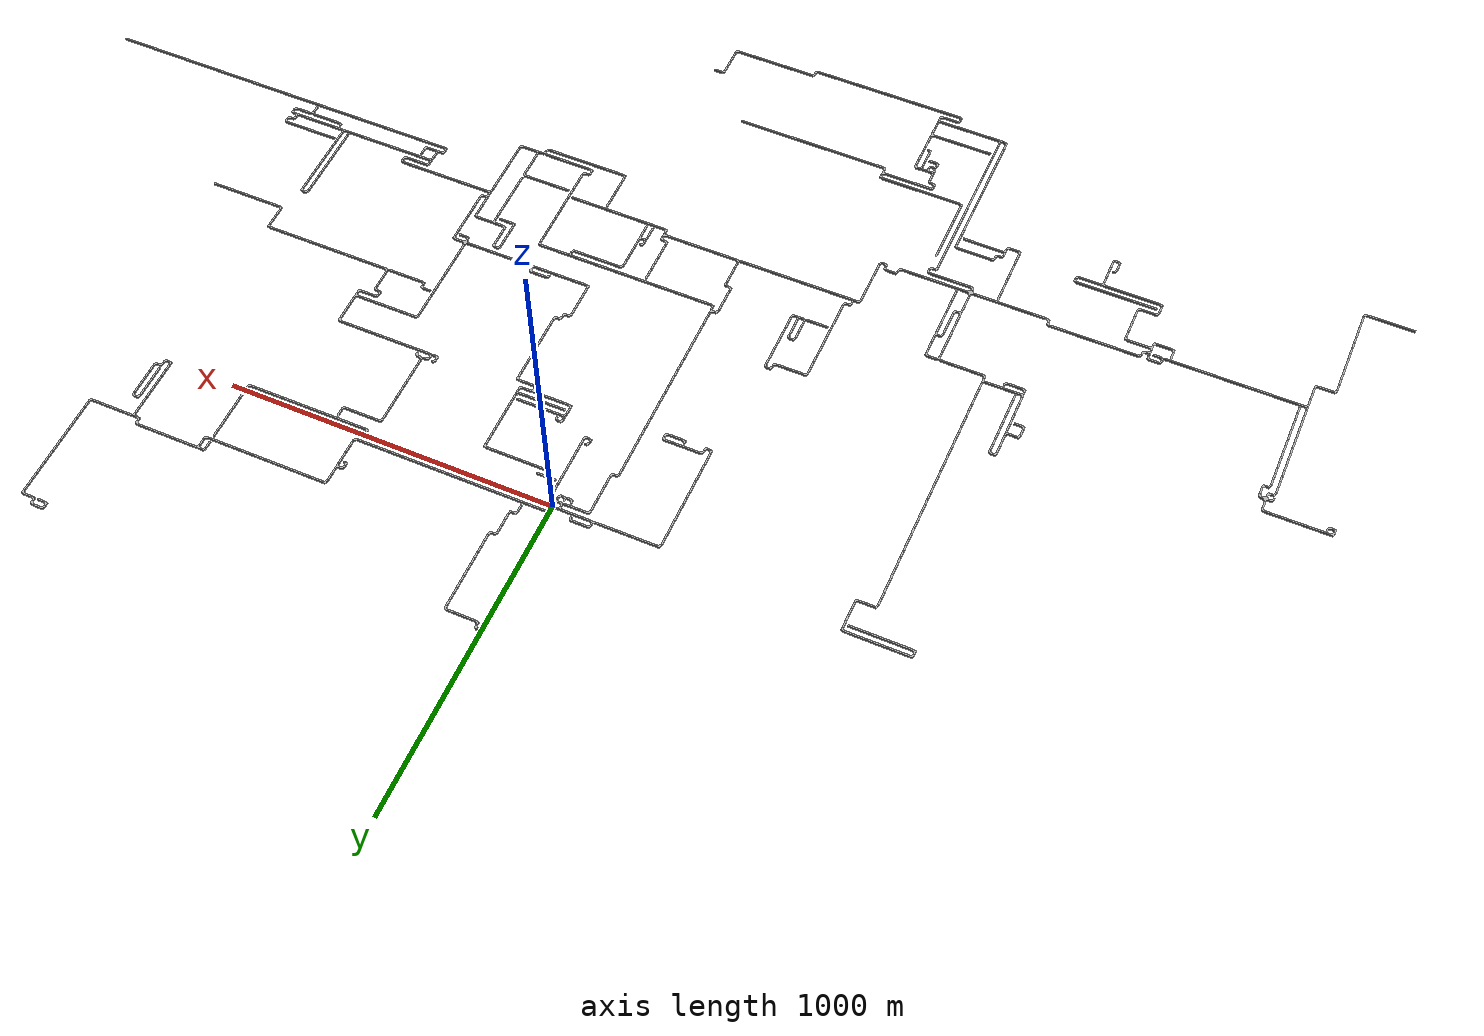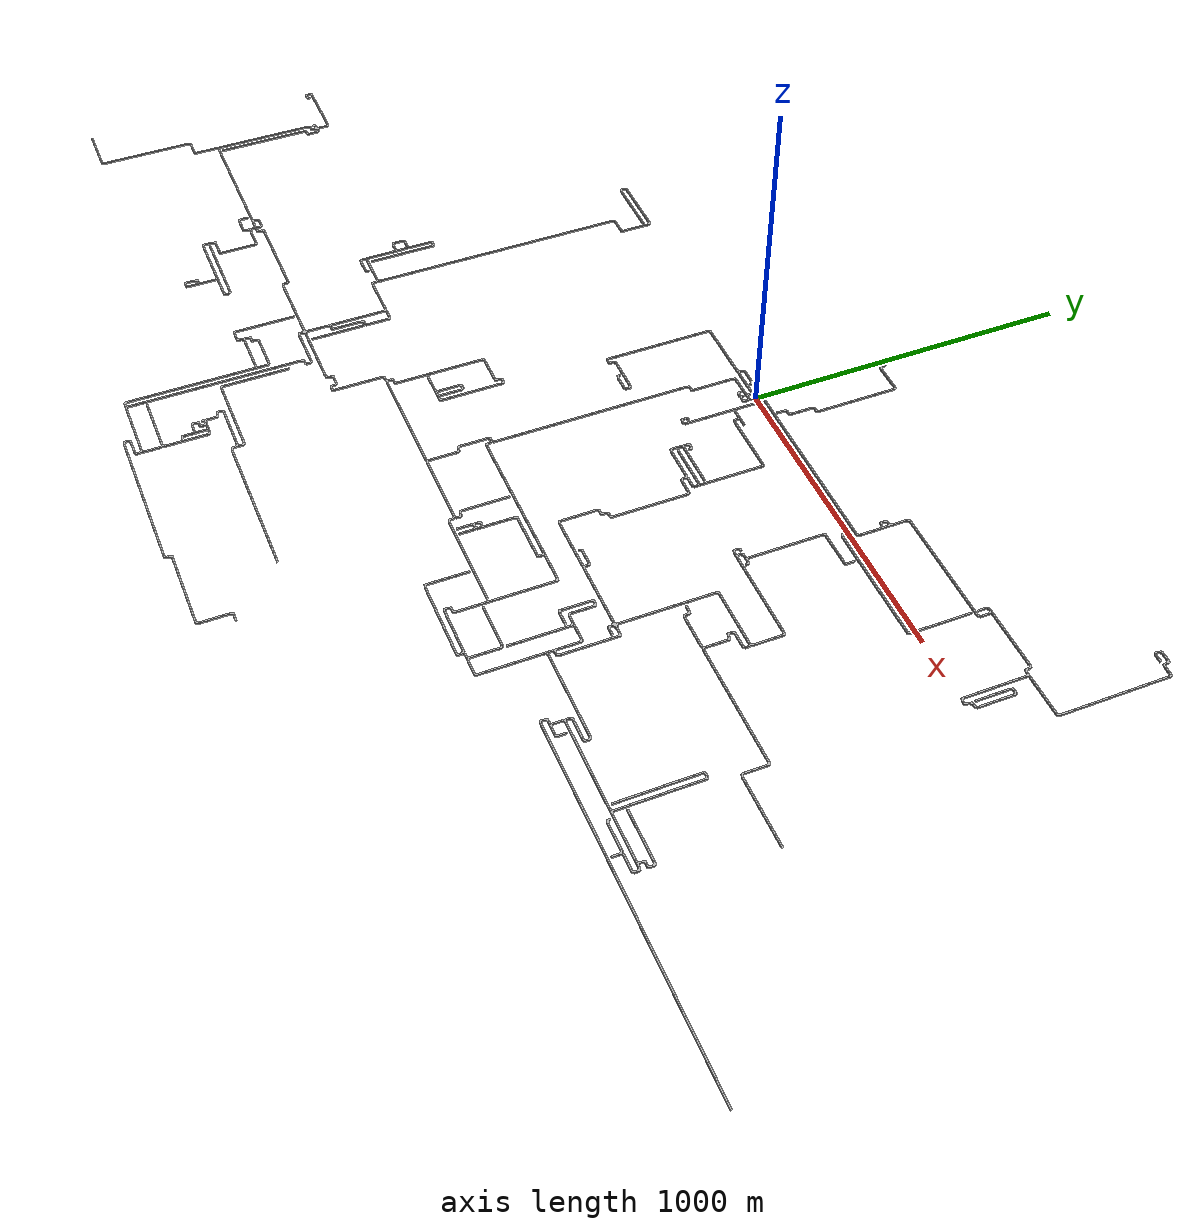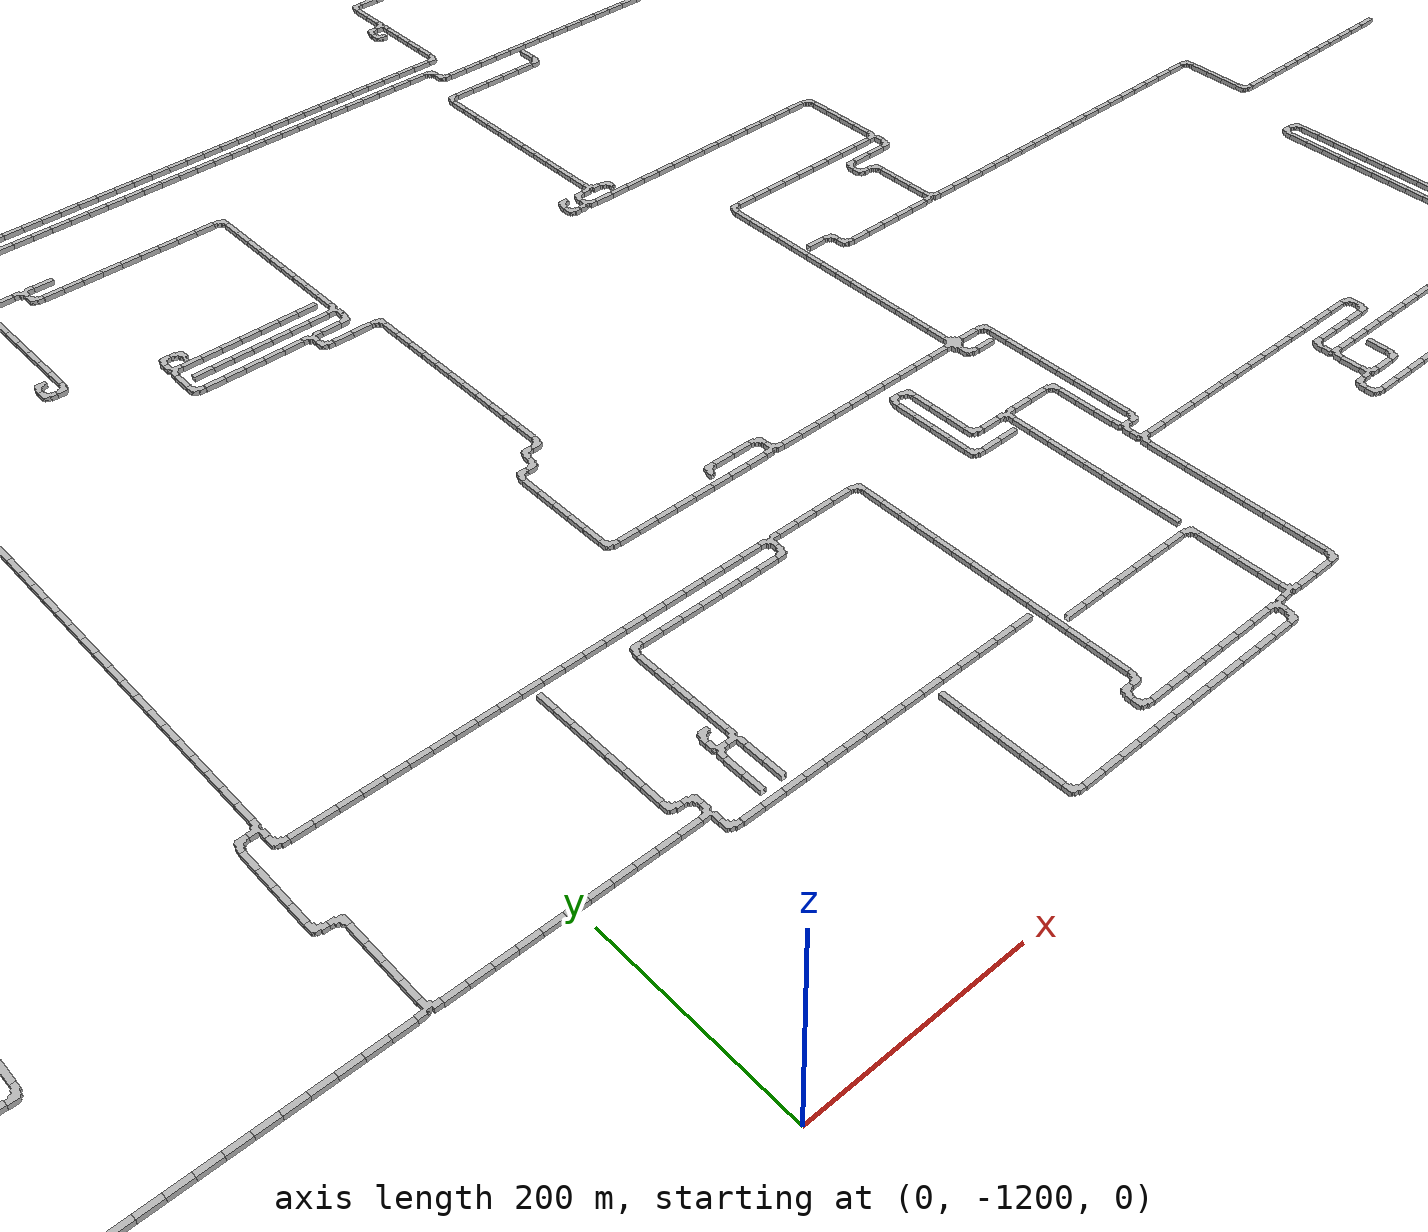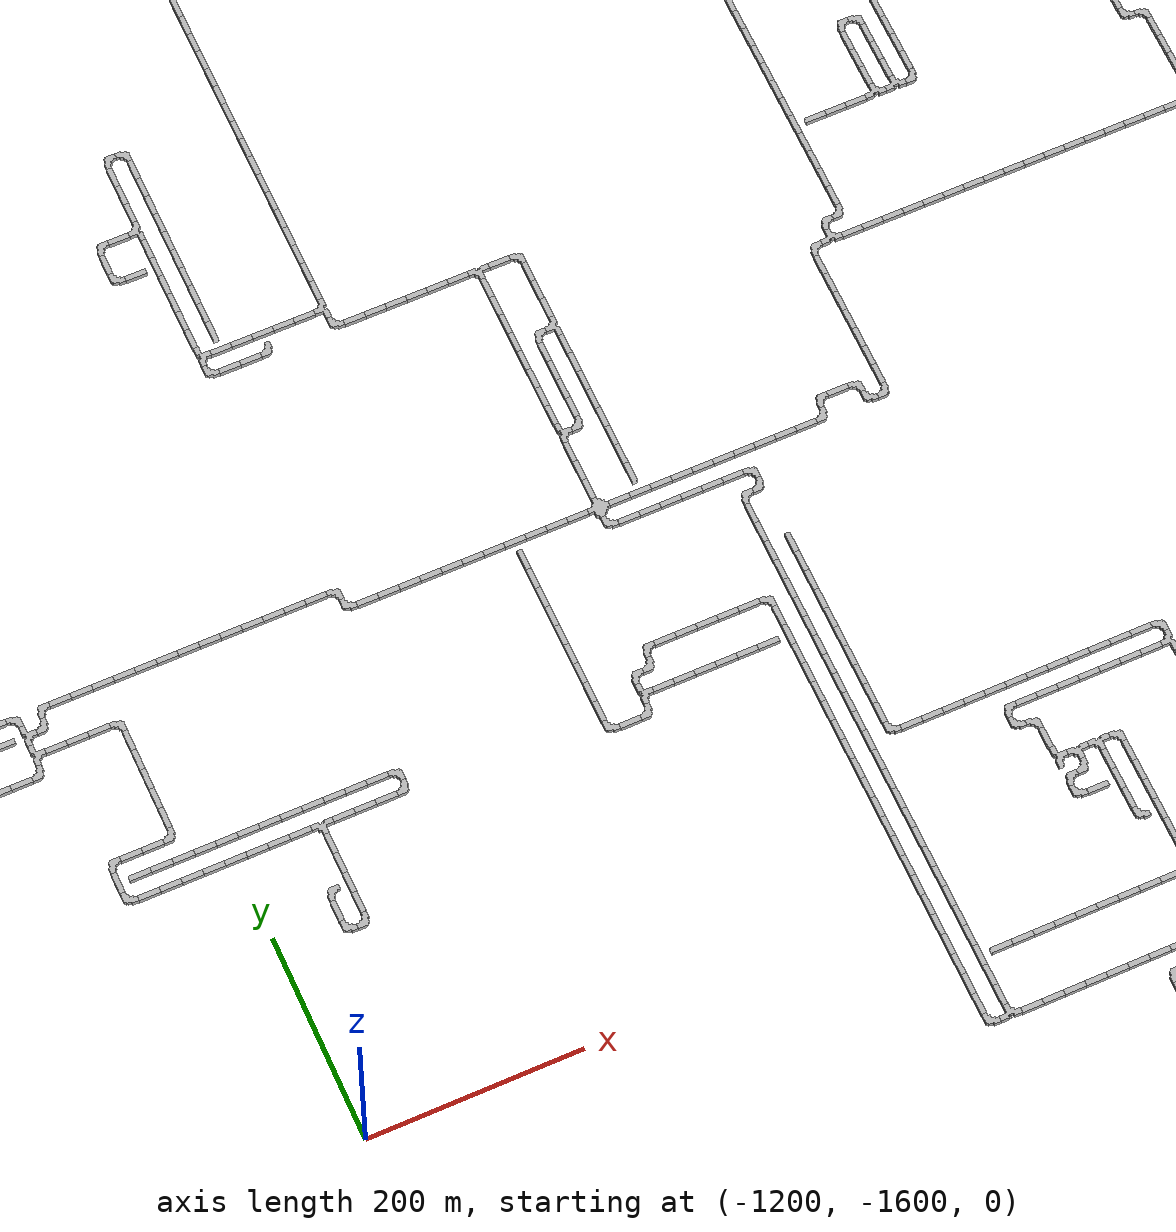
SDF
<sdf version="1.6">
<world name="cave_32000_0">
<include>
    <static>true</static>
    <name>cave_0_0</name>
    <pose>0 0 0 0 0 -1.5707963267948966</pose>
    <uri>model://cave_4way_20m</uri>
  </include>
  <include>
    <static>true</static>
    <name>cave_1_0</name>
    <pose>20 0 0 0 0 3.141592653589793</pose>
    <uri>model://cave_3way_20m</uri>
  </include>
  <include>
    <static>true</static>
    <name>cave_2_0</name>
    <pose>40 0 0 0 0 1.5707963267948966</pose>
    <uri>model://cave_straight_20m</uri>
  </include>
  <include>
    <static>true</static>
    <name>cave_3_0</name>
    <pose>60 0 0 0 0 1.5707963267948966</pose>
    <uri>model://cave_straight_20m</uri>
  </include>
  <include>
    <static>true</static>
    <name>cave_4_0</name>
    <pose>80 0 0 0 0 1.5707963267948966</pose>
    <uri>model://cave_straight_20m</uri>
  </include>
  <include>
    <static>true</static>
    <name>cave_5_0</name>
    <pose>100 0 0 0 0 1.5707963267948966</pose>
    <uri>model://cave_straight_20m</uri>
  </include>
  <include>
    <static>true</static>
    <name>cave_6_0</name>
    <pose>120 0 0 0 0 1.5707963267948966</pose>
    <uri>model://cave_straight_20m</uri>
  </include>
  <include>
    <static>true</static>
    <name>cave_7_0</name>
    <pose>140 0 0 0 0 1.5707963267948966</pose>
    <uri>model://cave_straight_20m</uri>
  </include>
  <include>
    <static>true</static>
    <name>cave_8_0</name>
    <pose>160 0 0 0 0 1.5707963267948966</pose>
    <uri>model://cave_straight_20m</uri>
  </include>
  <include>
    <static>true</static>
    <name>cave_9_0</name>
    <pose>180 0 0 0 0 1.5707963267948966</pose>
    <uri>model://cave_straight_20m</uri>
  </include>
  <include>
    <static>true</static>
    <name>cave_10_0</name>
    <pose>200 0 0 0 0 1.5707963267948966</pose>
    <uri>model://cave_straight_20m</uri>
  </include>
  <include>
    <static>true</static>
    <name>cave_11_0</name>
    <pose>220 0 0 0 0 1.5707963267948966</pose>
    <uri>model://cave_straight_20m</uri>
  </include>
  <include>
    <static>true</static>
    <name>cave_12_0</name>
    <pose>240 0 0 0 0 1.5707963267948966</pose>
    <uri>model://cave_straight_20m</uri>
  </include>
  <include>
    <static>true</static>
    <name>cave_13_0</name>
    <pose>260 0 0 0 0 1.5707963267948966</pose>
    <uri>model://cave_straight_20m</uri>
  </include>
  <include>
    <static>true</static>
    <name>cave_14_0</name>
    <pose>280 0 0 0 0 1.5707963267948966</pose>
    <uri>model://cave_straight_20m</uri>
  </include>
  <include>
    <static>true</static>
    <name>cave_15_0</name>
    <pose>300 0 0 0 0 1.5707963267948966</pose>
    <uri>model://cave_straight_20m</uri>
  </include>
  <include>
    <static>true</static>
    <name>cave_16_0</name>
    <pose>320 0 0 0 0 1.5707963267948966</pose>
    <uri>model://cave_straight_20m</uri>
  </include>
  <include>
    <static>true</static>
    <name>cave_17_0</name>
    <pose>340 0 0 0 0 1.5707963267948966</pose>
    <uri>model://cave_straight_20m</uri>
  </include>
  <include>
    <static>true</static>
    <name>cave_18_0</name>
    <pose>360 0 0 0 0 1.5707963267948966</pose>
    <uri>model://cave_straight_20m</uri>
  </include>
  <include>
    <static>true</static>
    <name>cave_19_0</name>
    <pose>380 0 0 0 0 1.5707963267948966</pose>
    <uri>model://cave_straight_20m</uri>
  </include>
  <include>
    <static>true</static>
    <name>cave_20_0</name>
    <pose>400 0 0 0 0 1.5707963267948966</pose>
    <uri>model://cave_straight_20m</uri>
  </include>
  <include>
    <static>true</static>
    <name>cave_21_0</name>
    <pose>420 0 0 0 0 1.5707963267948966</pose>
    <uri>model://cave_straight_20m</uri>
  </include>
  <include>
    <static>true</static>
    <name>cave_22_0</name>
    <pose>440 0 0 0 0 1.5707963267948966</pose>
    <uri>model://cave_straight_20m</uri>
  </include>
  <include>
    <static>true</static>
    <name>cave_23_0</name>
    <pose>460 0 0 0 0 1.5707963267948966</pose>
    <uri>model://cave_straight_20m</uri>
  </include>
  <include>
    <static>true</static>
    <name>cave_24_0</name>
    <pose>480 0 0 0 0 1.5707963267948966</pose>
    <uri>model://cave_straight_20m</uri>
  </include>
  <include>
    <static>true</static>
    <name>cave_25_0</name>
    <pose>500 0 0 0 0 1.5707963267948966</pose>
    <uri>model://cave_straight_20m</uri>
  </include>
  <include>
    <static>true</static>
    <name>cave_26_0</name>
    <pose>520 0 0 0 0 1.5707963267948966</pose>
    <uri>model://cave_straight_20m</uri>
  </include>
  <include>
    <static>true</static>
    <name>cave_27_0</name>
    <pose>540 0 0 0 0 1.5707963267948966</pose>
    <uri>model://cave_straight_20m</uri>
  </include>
  <include>
    <static>true</static>
    <name>cave_28_0</name>
    <pose>560 0 0 0 0 1.5707963267948966</pose>
    <uri>model://cave_straight_20m</uri>
  </include>
  <include>
    <static>true</static>
    <name>cave_29_0</name>
    <pose>580 0 0 0 0 3.141592653589793</pose>
    <uri>model://cave_L_20m</uri>
  </include>
  <include>
    <static>true</static>
    <name>cave_29_-1</name>
    <pose>580 -20 0 0 0 0.0</pose>
    <uri>model://cave_L_20m</uri>
  </include>
  <include>
    <static>true</static>
    <name>cave_30_-1</name>
    <pose>600 -20 0 0 0 1.5707963267948966</pose>
    <uri>model://cave_straight_20m</uri>
  </include>
  <include>
    <static>true</static>
    <name>cave_31_-1</name>
    <pose>620 -20 0 0 0 1.5707963267948966</pose>
    <uri>model://cave_straight_20m</uri>
  </include>
  <include>
    <static>true</static>
    <name>cave_32_-1</name>
    <pose>640 -20 0 0 0 1.5707963267948966</pose>
    <uri>model://cave_straight_20m</uri>
  </include>
  <include>
    <static>true</static>
    <name>cave_33_-1</name>
    <pose>660 -20 0 0 0 1.5707963267948966</pose>
    <uri>model://cave_straight_20m</uri>
  </include>
  <include>
    <static>true</static>
    <name>cave_34_-1</name>
    <pose>680 -20 0 0 0 1.5707963267948966</pose>
    <uri>model://cave_straight_20m</uri>
  </include>
  <include>
    <static>true</static>
    <name>cave_35_-1</name>
    <pose>700 -20 0 0 0 1.5707963267948966</pose>
    <uri>model://cave_straight_20m</uri>
  </include>
  <include>
    <static>true</static>
    <name>cave_36_-1</name>
    <pose>720 -20 0 0 0 1.5707963267948966</pose>
    <uri>model://cave_straight_20m</uri>
  </include>
  <include>
    <static>true</static>
    <name>cave_37_-1</name>
    <pose>740 -20 0 0 0 1.5707963267948966</pose>
    <uri>model://cave_straight_20m</uri>
  </include>
  <include>
    <static>true</static>
    <name>cave_38_-1</name>
    <pose>760 -20 0 0 0 1.5707963267948966</pose>
    <uri>model://cave_straight_20m</uri>
  </include>
  <include>
    <static>true</static>
    <name>cave_39_-1</name>
    <pose>780 -20 0 0 0 1.5707963267948966</pose>
    <uri>model://cave_straight_20m</uri>
  </include>
  <include>
    <static>true</static>
    <name>cave_40_-1</name>
    <pose>800 -20 0 0 0 1.5707963267948966</pose>
    <uri>model://cave_straight_20m</uri>
  </include>
  <include>
    <static>true</static>
    <name>cave_41_-1</name>
    <pose>820 -20 0 0 0 1.5707963267948966</pose>
    <uri>model://cave_straight_20m</uri>
  </include>
  <include>
    <static>true</static>
    <name>cave_42_-1</name>
    <pose>840 -20 0 0 0 1.5707963267948966</pose>
    <uri>model://cave_straight_20m</uri>
  </include>
  <include>
    <static>true</static>
    <name>cave_43_-1</name>
    <pose>860 -20 0 0 0 1.5707963267948966</pose>
    <uri>model://cave_straight_20m</uri>
  </include>
  <include>
    <static>true</static>
    <name>cave_44_-1</name>
    <pose>880 -20 0 0 0 1.5707963267948966</pose>
    <uri>model://cave_straight_20m</uri>
  </include>
  <include>
    <static>true</static>
    <name>cave_45_-1</name>
    <pose>900 -20 0 0 0 1.5707963267948966</pose>
    <uri>model://cave_straight_20m</uri>
  </include>
  <include>
    <static>true</static>
    <name>cave_46_-1</name>
    <pose>920 -20 0 0 0 1.5707963267948966</pose>
    <uri>model://cave_straight_20m</uri>
  </include>
  <include>
    <static>true</static>
    <name>cave_47_-1</name>
    <pose>940 -20 0 0 0 1.5707963267948966</pose>
    <uri>model://cave_straight_20m</uri>
  </include>
  <include>
    <static>true</static>
    <name>cave_48_-1</name>
    <pose>960 -20 0 0 0 1.5707963267948966</pose>
    <uri>model://cave_L_20m</uri>
  </include>
  <include>
    <static>true</static>
    <name>cave_48_0</name>
    <pose>960 0 0 0 0 0.0</pose>
    <uri>model://cave_straight_20m</uri>
  </include>
  <include>
    <static>true</static>
    <name>cave_48_1</name>
    <pose>960 20 0 0 0 0.0</pose>
    <uri>model://cave_straight_20m</uri>
  </include>
  <include>
    <static>true</static>
    <name>cave_48_2</name>
    <pose>960 40 0 0 0 0.0</pose>
    <uri>model://cave_straight_20m</uri>
  </include>
  <include>
    <static>true</static>
    <name>cave_48_3</name>
    <pose>960 60 0 0 0 0.0</pose>
    <uri>model://cave_straight_20m</uri>
  </include>
  <include>
    <static>true</static>
    <name>cave_48_4</name>
    <pose>960 80 0 0 0 0.0</pose>
    <uri>model://cave_straight_20m</uri>
  </include>
  <include>
    <static>true</static>
    <name>cave_48_5</name>
    <pose>960 100 0 0 0 0.0</pose>
    <uri>model://cave_straight_20m</uri>
  </include>
  <include>
    <static>true</static>
    <name>cave_48_6</name>
    <pose>960 120 0 0 0 0.0</pose>
    <uri>model://cave_straight_20m</uri>
  </include>
  <include>
    <static>true</static>
    <name>cave_48_7</name>
    <pose>960 140 0 0 0 0.0</pose>
    <uri>model://cave_straight_20m</uri>
  </include>
  <include>
    <static>true</static>
    <name>cave_48_8</name>
    <pose>960 160 0 0 0 0.0</pose>
    <uri>model://cave_straight_20m</uri>
  </include>
  <include>
    <static>true</static>
    <name>cave_1_-1</name>
    <pose>20 -20 0 0 0 0.0</pose>
    <uri>model://cave_straight_20m</uri>
  </include>
  <include>
    <static>true</static>
    <name>cave_1_-2</name>
    <pose>20 -40 0 0 0 0.0</pose>
    <uri>model://cave_straight_20m</uri>
  </include>
  <include>
    <static>true</static>
    <name>cave_1_-3</name>
    <pose>20 -60 0 0 0 0.0</pose>
    <uri>model://cave_straight_20m</uri>
  </include>
  <include>
    <static>true</static>
    <name>cave_1_-4</name>
    <pose>20 -80 0 0 0 0.0</pose>
    <uri>model://cave_straight_20m</uri>
  </include>
  <include>
    <static>true</static>
    <name>cave_1_-5</name>
    <pose>20 -100 0 0 0 0.0</pose>
    <uri>model://cave_straight_20m</uri>
  </include>
  <include>
    <static>true</static>
    <name>cave_1_-6</name>
    <pose>20 -120 0 0 0 0.0</pose>
    <uri>model://cave_straight_20m</uri>
  </include>
  <include>
    <static>true</static>
    <name>cave_1_-7</name>
    <pose>20 -140 0 0 0 0.0</pose>
    <uri>model://cave_straight_20m</uri>
  </include>
  <include>
    <static>true</static>
    <name>cave_1_-8</name>
    <pose>20 -160 0 0 0 0.0</pose>
    <uri>model://cave_straight_20m</uri>
  </include>
  <include>
    <static>true</static>
    <name>cave_1_-9</name>
    <pose>20 -180 0 0 0 0.0</pose>
    <uri>model://cave_straight_20m</uri>
  </include>
  <include>
    <static>true</static>
    <name>cave_1_-10</name>
    <pose>20 -200 0 0 0 0.0</pose>
    <uri>model://cave_straight_20m</uri>
  </include>
  <include>
    <static>true</static>
    <name>cave_1_-11</name>
    <pose>20 -220 0 0 0 0.0</pose>
    <uri>model://cave_straight_20m</uri>
  </include>
  <include>
    <static>true</static>
    <name>cave_1_-12</name>
    <pose>20 -240 0 0 0 1.5707963267948966</pose>
    <uri>model://cave_L_20m</uri>
  </include>
  <include>
    <static>true</static>
    <name>cave_0_-12</name>
    <pose>0 -240 0 0 0 0.0</pose>
    <uri>model://cave_L_20m</uri>
  </include>
  <include>
    <static>true</static>
    <name>cave_0_-11</name>
    <pose>0 -220 0 0 0 -1.5707963267948966</pose>
    <uri>model://cave_L_20m</uri>
  </include>
  <include>
    <static>true</static>
    <name>cave_0_-1</name>
    <pose>0 -20 0 0 0 1.5707963267948966</pose>
    <uri>model://cave_3way_20m</uri>
  </include>
  <include>
    <static>true</static>
    <name>cave_0_-2</name>
    <pose>0 -40 0 0 0 1.5707963267948966</pose>
    <uri>model://cave_L_20m</uri>
  </include>
  <include>
    <static>true</static>
    <name>cave_-1_-2</name>
    <pose>-20 -40 0 0 0 0.0</pose>
    <uri>model://cave_3way_20m</uri>
  </include>
  <include>
    <static>true</static>
    <name>cave_-2_-2</name>
    <pose>-40 -40 0 0 0 0.0</pose>
    <uri>model://cave_L_20m</uri>
  </include>
  <include>
    <static>true</static>
    <name>cave_-1_-1</name>
    <pose>-20 -20 0 0 0 0.0</pose>
    <uri>model://cave_3way_20m</uri>
  </include>
  <include>
    <static>true</static>
    <name>cave_-2_-1</name>
    <pose>-40 -20 0 0 0 1.5707963267948966</pose>
    <uri>model://cave_straight_20m</uri>
  </include>
  <include>
    <static>true</static>
    <name>cave_-3_-1</name>
    <pose>-60 -20 0 0 0 1.5707963267948966</pose>
    <uri>model://cave_straight_20m</uri>
  </include>
  <include>
    <static>true</static>
    <name>cave_-4_-1</name>
    <pose>-80 -20 0 0 0 1.5707963267948966</pose>
    <uri>model://cave_straight_20m</uri>
  </include>
  <include>
    <static>true</static>
    <name>cave_-5_-1</name>
    <pose>-100 -20 0 0 0 -1.5707963267948966</pose>
    <uri>model://cave_L_20m</uri>
  </include>
  <include>
    <static>true</static>
    <name>cave_-5_-2</name>
    <pose>-100 -40 0 0 0 0.0</pose>
    <uri>model://cave_straight_20m</uri>
  </include>
  <include>
    <static>true</static>
    <name>cave_-5_-3</name>
    <pose>-100 -60 0 0 0 0.0</pose>
    <uri>model://cave_straight_20m</uri>
  </include>
  <include>
    <static>true</static>
    <name>cave_-5_-4</name>
    <pose>-100 -80 0 0 0 0.0</pose>
    <uri>model://cave_straight_20m</uri>
  </include>
  <include>
    <static>true</static>
    <name>cave_-5_-5</name>
    <pose>-100 -100 0 0 0 0.0</pose>
    <uri>model://cave_straight_20m</uri>
  </include>
  <include>
    <static>true</static>
    <name>cave_-5_-6</name>
    <pose>-100 -120 0 0 0 0.0</pose>
    <uri>model://cave_straight_20m</uri>
  </include>
  <include>
    <static>true</static>
    <name>cave_-5_-7</name>
    <pose>-100 -140 0 0 0 0.0</pose>
    <uri>model://cave_straight_20m</uri>
  </include>
  <include>
    <static>true</static>
    <name>cave_-5_-8</name>
    <pose>-100 -160 0 0 0 1.5707963267948966</pose>
    <uri>model://cave_L_20m</uri>
  </include>
  <include>
    <static>true</static>
    <name>cave_-6_-8</name>
    <pose>-120 -160 0 0 0 -1.5707963267948966</pose>
    <uri>model://cave_L_20m</uri>
  </include>
  <include>
    <static>true</static>
    <name>cave_-6_-9</name>
    <pose>-120 -180 0 0 0 0.0</pose>
    <uri>model://cave_straight_20m</uri>
  </include>
  <include>
    <static>true</static>
    <name>cave_-6_-10</name>
    <pose>-120 -200 0 0 0 0.0</pose>
    <uri>model://cave_straight_20m</uri>
  </include>
  <include>
    <static>true</static>
    <name>cave_-6_-11</name>
    <pose>-120 -220 0 0 0 0.0</pose>
    <uri>model://cave_straight_20m</uri>
  </include>
  <include>
    <static>true</static>
    <name>cave_-6_-12</name>
    <pose>-120 -240 0 0 0 0.0</pose>
    <uri>model://cave_straight_20m</uri>
  </include>
  <include>
    <static>true</static>
    <name>cave_-6_-13</name>
    <pose>-120 -260 0 0 0 0.0</pose>
    <uri>model://cave_straight_20m</uri>
  </include>
  <include>
    <static>true</static>
    <name>cave_-6_-14</name>
    <pose>-120 -280 0 0 0 0.0</pose>
    <uri>model://cave_straight_20m</uri>
  </include>
  <include>
    <static>true</static>
    <name>cave_-6_-15</name>
    <pose>-120 -300 0 0 0 0.0</pose>
    <uri>model://cave_straight_20m</uri>
  </include>
  <include>
    <static>true</static>
    <name>cave_-6_-16</name>
    <pose>-120 -320 0 0 0 0.0</pose>
    <uri>model://cave_straight_20m</uri>
  </include>
  <include>
    <static>true</static>
    <name>cave_-6_-17</name>
    <pose>-120 -340 0 0 0 0.0</pose>
    <uri>model://cave_straight_20m</uri>
  </include>
  <include>
    <static>true</static>
    <name>cave_-6_-18</name>
    <pose>-120 -360 0 0 0 0.0</pose>
    <uri>model://cave_straight_20m</uri>
  </include>
  <include>
    <static>true</static>
    <name>cave_-6_-19</name>
    <pose>-120 -380 0 0 0 0.0</pose>
    <uri>model://cave_straight_20m</uri>
  </include>
  <include>
    <static>true</static>
    <name>cave_-6_-20</name>
    <pose>-120 -400 0 0 0 0.0</pose>
    <uri>model://cave_straight_20m</uri>
  </include>
  <include>
    <static>true</static>
    <name>cave_-6_-21</name>
    <pose>-120 -420 0 0 0 0.0</pose>
    <uri>model://cave_straight_20m</uri>
  </include>
  <include>
    <static>true</static>
    <name>cave_-6_-22</name>
    <pose>-120 -440 0 0 0 0.0</pose>
    <uri>model://cave_straight_20m</uri>
  </include>
  <include>
    <static>true</static>
    <name>cave_-6_-23</name>
    <pose>-120 -460 0 0 0 0.0</pose>
    <uri>model://cave_straight_20m</uri>
  </include>
  <include>
    <static>true</static>
    <name>cave_-6_-24</name>
    <pose>-120 -480 0 0 0 0.0</pose>
    <uri>model://cave_straight_20m</uri>
  </include>
  <include>
    <static>true</static>
    <name>cave_-6_-25</name>
    <pose>-120 -500 0 0 0 0.0</pose>
    <uri>model://cave_straight_20m</uri>
  </include>
  <include>
    <static>true</static>
    <name>cave_-6_-26</name>
    <pose>-120 -520 0 0 0 0.0</pose>
    <uri>model://cave_straight_20m</uri>
  </include>
  <include>
    <static>true</static>
    <name>cave_-6_-27</name>
    <pose>-120 -540 0 0 0 0.0</pose>
    <uri>model://cave_straight_20m</uri>
  </include>
  <include>
    <static>true</static>
    <name>cave_-6_-28</name>
    <pose>-120 -560 0 0 0 0.0</pose>
    <uri>model://cave_straight_20m</uri>
  </include>
  <include>
    <static>true</static>
    <name>cave_-6_-29</name>
    <pose>-120 -580 0 0 0 0.0</pose>
    <uri>model://cave_straight_20m</uri>
  </include>
  <include>
    <static>true</static>
    <name>cave_-6_-30</name>
    <pose>-120 -600 0 0 0 0.0</pose>
    <uri>model://cave_straight_20m</uri>
  </include>
  <include>
    <static>true</static>
    <name>cave_-6_-31</name>
    <pose>-120 -620 0 0 0 0.0</pose>
    <uri>model://cave_straight_20m</uri>
  </include>
  <include>
    <static>true</static>
    <name>cave_-6_-32</name>
    <pose>-120 -640 0 0 0 0.0</pose>
    <uri>model://cave_straight_20m</uri>
  </include>
  <include>
    <static>true</static>
    <name>cave_-6_-33</name>
    <pose>-120 -660 0 0 0 0.0</pose>
    <uri>model://cave_straight_20m</uri>
  </include>
  <include>
    <static>true</static>
    <name>cave_-6_-34</name>
    <pose>-120 -680 0 0 0 0.0</pose>
    <uri>model://cave_straight_20m</uri>
  </include>
  <include>
    <static>true</static>
    <name>cave_-6_-35</name>
    <pose>-120 -700 0 0 0 0.0</pose>
    <uri>model://cave_straight_20m</uri>
  </include>
  <include>
    <static>true</static>
    <name>cave_-6_-36</name>
    <pose>-120 -720 0 0 0 0.0</pose>
    <uri>model://cave_straight_20m</uri>
  </include>
  <include>
    <static>true</static>
    <name>cave_-6_-37</name>
    <pose>-120 -740 0 0 0 0.0</pose>
    <uri>model://cave_straight_20m</uri>
  </include>
  <include>
    <static>true</static>
    <name>cave_-6_-38</name>
    <pose>-120 -760 0 0 0 0.0</pose>
    <uri>model://cave_straight_20m</uri>
  </include>
  <include>
    <static>true</static>
    <name>cave_-6_-39</name>
    <pose>-120 -780 0 0 0 1.5707963267948966</pose>
    <uri>model://cave_3way_20m</uri>
  </include>
  <include>
    <static>true</static>
    <name>cave_-6_-40</name>
    <pose>-120 -800 0 0 0 0.0</pose>
    <uri>model://cave_L_20m</uri>
  </include>
  <include>
    <static>true</static>
    <name>cave_-5_-40</name>
    <pose>-100 -800 0 0 0 1.5707963267948966</pose>
    <uri>model://cave_straight_20m</uri>
  </include>
  <include>
    <static>true</static>
    <name>cave_-4_-40</name>
    <pose>-80 -800 0 0 0 1.5707963267948966</pose>
    <uri>model://cave_straight_20m</uri>
  </include>
  <include>
    <static>true</static>
    <name>cave_-3_-40</name>
    <pose>-60 -800 0 0 0 1.5707963267948966</pose>
    <uri>model://cave_straight_20m</uri>
  </include>
  <include>
    <static>true</static>
    <name>cave_-2_-40</name>
    <pose>-40 -800 0 0 0 1.5707963267948966</pose>
    <uri>model://cave_straight_20m</uri>
  </include>
  <include>
    <static>true</static>
    <name>cave_-1_-40</name>
    <pose>-20 -800 0 0 0 1.5707963267948966</pose>
    <uri>model://cave_straight_20m</uri>
  </include>
  <include>
    <static>true</static>
    <name>cave_0_-40</name>
    <pose>0 -800 0 0 0 1.5707963267948966</pose>
    <uri>model://cave_straight_20m</uri>
  </include>
  <include>
    <static>true</static>
    <name>cave_1_-40</name>
    <pose>20 -800 0 0 0 1.5707963267948966</pose>
    <uri>model://cave_straight_20m</uri>
  </include>
  <include>
    <static>true</static>
    <name>cave_2_-40</name>
    <pose>40 -800 0 0 0 1.5707963267948966</pose>
    <uri>model://cave_straight_20m</uri>
  </include>
  <include>
    <static>true</static>
    <name>cave_3_-40</name>
    <pose>60 -800 0 0 0 1.5707963267948966</pose>
    <uri>model://cave_straight_20m</uri>
  </include>
  <include>
    <static>true</static>
    <name>cave_4_-40</name>
    <pose>80 -800 0 0 0 1.5707963267948966</pose>
    <uri>model://cave_straight_20m</uri>
  </include>
  <include>
    <static>true</static>
    <name>cave_5_-40</name>
    <pose>100 -800 0 0 0 1.5707963267948966</pose>
    <uri>model://cave_straight_20m</uri>
  </include>
  <include>
    <static>true</static>
    <name>cave_6_-40</name>
    <pose>120 -800 0 0 0 1.5707963267948966</pose>
    <uri>model://cave_straight_20m</uri>
  </include>
  <include>
    <static>true</static>
    <name>cave_7_-40</name>
    <pose>140 -800 0 0 0 1.5707963267948966</pose>
    <uri>model://cave_straight_20m</uri>
  </include>
  <include>
    <static>true</static>
    <name>cave_8_-40</name>
    <pose>160 -800 0 0 0 1.5707963267948966</pose>
    <uri>model://cave_straight_20m</uri>
  </include>
  <include>
    <static>true</static>
    <name>cave_9_-40</name>
    <pose>180 -800 0 0 0 1.5707963267948966</pose>
    <uri>model://cave_straight_20m</uri>
  </include>
  <include>
    <static>true</static>
    <name>cave_10_-40</name>
    <pose>200 -800 0 0 0 1.5707963267948966</pose>
    <uri>model://cave_straight_20m</uri>
  </include>
  <include>
    <static>true</static>
    <name>cave_11_-40</name>
    <pose>220 -800 0 0 0 1.5707963267948966</pose>
    <uri>model://cave_straight_20m</uri>
  </include>
  <include>
    <static>true</static>
    <name>cave_12_-40</name>
    <pose>240 -800 0 0 0 1.5707963267948966</pose>
    <uri>model://cave_straight_20m</uri>
  </include>
  <include>
    <static>true</static>
    <name>cave_13_-40</name>
    <pose>260 -800 0 0 0 1.5707963267948966</pose>
    <uri>model://cave_straight_20m</uri>
  </include>
  <include>
    <static>true</static>
    <name>cave_14_-40</name>
    <pose>280 -800 0 0 0 1.5707963267948966</pose>
    <uri>model://cave_straight_20m</uri>
  </include>
  <include>
    <static>true</static>
    <name>cave_15_-40</name>
    <pose>300 -800 0 0 0 1.5707963267948966</pose>
    <uri>model://cave_straight_20m</uri>
  </include>
  <include>
    <static>true</static>
    <name>cave_16_-40</name>
    <pose>320 -800 0 0 0 1.5707963267948966</pose>
    <uri>model://cave_straight_20m</uri>
  </include>
  <include>
    <static>true</static>
    <name>cave_17_-40</name>
    <pose>340 -800 0 0 0 3.141592653589793</pose>
    <uri>model://cave_3way_20m</uri>
  </include>
  <include>
    <static>true</static>
    <name>cave_18_-40</name>
    <pose>360 -800 0 0 0 1.5707963267948966</pose>
    <uri>model://cave_straight_20m</uri>
  </include>
  <include>
    <static>true</static>
    <name>cave_19_-40</name>
    <pose>380 -800 0 0 0 1.5707963267948966</pose>
    <uri>model://cave_straight_20m</uri>
  </include>
  <include>
    <static>true</static>
    <name>cave_20_-40</name>
    <pose>400 -800 0 0 0 1.5707963267948966</pose>
    <uri>model://cave_straight_20m</uri>
  </include>
  <include>
    <static>true</static>
    <name>cave_21_-40</name>
    <pose>420 -800 0 0 0 1.5707963267948966</pose>
    <uri>model://cave_straight_20m</uri>
  </include>
  <include>
    <static>true</static>
    <name>cave_22_-40</name>
    <pose>440 -800 0 0 0 3.141592653589793</pose>
    <uri>model://cave_L_20m</uri>
  </include>
  <include>
    <static>true</static>
    <name>cave_22_-41</name>
    <pose>440 -820 0 0 0 0.0</pose>
    <uri>model://cave_straight_20m</uri>
  </include>
  <include>
    <static>true</static>
    <name>cave_22_-42</name>
    <pose>440 -840 0 0 0 0.0</pose>
    <uri>model://cave_straight_20m</uri>
  </include>
  <include>
    <static>true</static>
    <name>cave_22_-43</name>
    <pose>440 -860 0 0 0 0.0</pose>
    <uri>model://cave_straight_20m</uri>
  </include>
  <include>
    <static>true</static>
    <name>cave_22_-44</name>
    <pose>440 -880 0 0 0 0.0</pose>
    <uri>model://cave_straight_20m</uri>
  </include>
  <include>
    <static>true</static>
    <name>cave_22_-45</name>
    <pose>440 -900 0 0 0 0.0</pose>
    <uri>model://cave_straight_20m</uri>
  </include>
  <include>
    <static>true</static>
    <name>cave_22_-46</name>
    <pose>440 -920 0 0 0 0.0</pose>
    <uri>model://cave_straight_20m</uri>
  </include>
  <include>
    <static>true</static>
    <name>cave_22_-47</name>
    <pose>440 -940 0 0 0 0.0</pose>
    <uri>model://cave_straight_20m</uri>
  </include>
  <include>
    <static>true</static>
    <name>cave_22_-48</name>
    <pose>440 -960 0 0 0 0.0</pose>
    <uri>model://cave_straight_20m</uri>
  </include>
  <include>
    <static>true</static>
    <name>cave_22_-49</name>
    <pose>440 -980 0 0 0 0.0</pose>
    <uri>model://cave_straight_20m</uri>
  </include>
  <include>
    <static>true</static>
    <name>cave_22_-50</name>
    <pose>440 -1000 0 0 0 0.0</pose>
    <uri>model://cave_straight_20m</uri>
  </include>
  <include>
    <static>true</static>
    <name>cave_22_-51</name>
    <pose>440 -1020 0 0 0 0.0</pose>
    <uri>model://cave_straight_20m</uri>
  </include>
  <include>
    <static>true</static>
    <name>cave_22_-52</name>
    <pose>440 -1040 0 0 0 0.0</pose>
    <uri>model://cave_straight_20m</uri>
  </include>
  <include>
    <static>true</static>
    <name>cave_22_-53</name>
    <pose>440 -1060 0 0 0 0.0</pose>
    <uri>model://cave_straight_20m</uri>
  </include>
  <include>
    <static>true</static>
    <name>cave_22_-54</name>
    <pose>440 -1080 0 0 0 0.0</pose>
    <uri>model://cave_straight_20m</uri>
  </include>
  <include>
    <static>true</static>
    <name>cave_22_-55</name>
    <pose>440 -1100 0 0 0 1.5707963267948966</pose>
    <uri>model://cave_L_20m</uri>
  </include>
  <include>
    <static>true</static>
    <name>cave_21_-55</name>
    <pose>420 -1100 0 0 0 -1.5707963267948966</pose>
    <uri>model://cave_L_20m</uri>
  </include>
  <include>
    <static>true</static>
    <name>cave_21_-56</name>
    <pose>420 -1120 0 0 0 0.0</pose>
    <uri>model://cave_L_20m</uri>
  </include>
  <include>
    <static>true</static>
    <name>cave_22_-56</name>
    <pose>440 -1120 0 0 0 1.5707963267948966</pose>
    <uri>model://cave_straight_20m</uri>
  </include>
  <include>
    <static>true</static>
    <name>cave_23_-56</name>
    <pose>460 -1120 0 0 0 1.5707963267948966</pose>
    <uri>model://cave_straight_20m</uri>
  </include>
  <include>
    <static>true</static>
    <name>cave_24_-56</name>
    <pose>480 -1120 0 0 0 1.5707963267948966</pose>
    <uri>model://cave_straight_20m</uri>
  </include>
  <include>
    <static>true</static>
    <name>cave_25_-56</name>
    <pose>500 -1120 0 0 0 1.5707963267948966</pose>
    <uri>model://cave_straight_20m</uri>
  </include>
  <include>
    <static>true</static>
    <name>cave_26_-56</name>
    <pose>520 -1120 0 0 0 1.5707963267948966</pose>
    <uri>model://cave_straight_20m</uri>
  </include>
  <include>
    <static>true</static>
    <name>cave_27_-56</name>
    <pose>540 -1120 0 0 0 1.5707963267948966</pose>
    <uri>model://cave_straight_20m</uri>
  </include>
  <include>
    <static>true</static>
    <name>cave_28_-56</name>
    <pose>560 -1120 0 0 0 1.5707963267948966</pose>
    <uri>model://cave_straight_20m</uri>
  </include>
  <include>
    <static>true</static>
    <name>cave_29_-56</name>
    <pose>580 -1120 0 0 0 3.141592653589793</pose>
    <uri>model://cave_3way_20m</uri>
  </include>
  <include>
    <static>true</static>
    <name>cave_30_-56</name>
    <pose>600 -1120 0 0 0 0.0</pose>
    <uri>model://cave_3way_20m</uri>
  </include>
  <include>
    <static>true</static>
    <name>cave_31_-56</name>
    <pose>620 -1120 0 0 0 1.5707963267948966</pose>
    <uri>model://cave_straight_20m</uri>
  </include>
  <include>
    <static>true</static>
    <name>cave_32_-56</name>
    <pose>640 -1120 0 0 0 1.5707963267948966</pose>
    <uri>model://cave_straight_20m</uri>
  </include>
  <include>
    <static>true</static>
    <name>cave_33_-56</name>
    <pose>660 -1120 0 0 0 1.5707963267948966</pose>
    <uri>model://cave_L_20m</uri>
  </include>
  <include>
    <static>true</static>
    <name>cave_33_-55</name>
    <pose>660 -1100 0 0 0 0.0</pose>
    <uri>model://cave_straight_20m</uri>
  </include>
  <include>
    <static>true</static>
    <name>cave_33_-54</name>
    <pose>660 -1080 0 0 0 0.0</pose>
    <uri>model://cave_straight_20m</uri>
  </include>
  <include>
    <static>true</static>
    <name>cave_33_-53</name>
    <pose>660 -1060 0 0 0 0.0</pose>
    <uri>model://cave_straight_20m</uri>
  </include>
  <include>
    <static>true</static>
    <name>cave_33_-52</name>
    <pose>660 -1040 0 0 0 0.0</pose>
    <uri>model://cave_straight_20m</uri>
  </include>
  <include>
    <static>true</static>
    <name>cave_33_-51</name>
    <pose>660 -1020 0 0 0 0.0</pose>
    <uri>model://cave_straight_20m</uri>
  </include>
  <include>
    <static>true</static>
    <name>cave_33_-50</name>
    <pose>660 -1000 0 0 0 0.0</pose>
    <uri>model://cave_straight_20m</uri>
  </include>
  <include>
    <static>true</static>
    <name>cave_33_-49</name>
    <pose>660 -980 0 0 0 0.0</pose>
    <uri>model://cave_straight_20m</uri>
  </include>
  <include>
    <static>true</static>
    <name>cave_33_-48</name>
    <pose>660 -960 0 0 0 0.0</pose>
    <uri>model://cave_straight_20m</uri>
  </include>
  <include>
    <static>true</static>
    <name>cave_33_-47</name>
    <pose>660 -940 0 0 0 0.0</pose>
    <uri>model://cave_straight_20m</uri>
  </include>
  <include>
    <static>true</static>
    <name>cave_33_-46</name>
    <pose>660 -920 0 0 0 -1.5707963267948966</pose>
    <uri>model://cave_3way_20m</uri>
  </include>
  <include>
    <static>true</static>
    <name>cave_34_-46</name>
    <pose>680 -920 0 0 0 1.5707963267948966</pose>
    <uri>model://cave_straight_20m</uri>
  </include>
  <include>
    <static>true</static>
    <name>cave_35_-46</name>
    <pose>700 -920 0 0 0 1.5707963267948966</pose>
    <uri>model://cave_straight_20m</uri>
  </include>
  <include>
    <static>true</static>
    <name>cave_36_-46</name>
    <pose>720 -920 0 0 0 1.5707963267948966</pose>
    <uri>model://cave_straight_20m</uri>
  </include>
  <include>
    <static>true</static>
    <name>cave_37_-46</name>
    <pose>740 -920 0 0 0 1.5707963267948966</pose>
    <uri>model://cave_straight_20m</uri>
  </include>
  <include>
    <static>true</static>
    <name>cave_38_-46</name>
    <pose>760 -920 0 0 0 1.5707963267948966</pose>
    <uri>model://cave_straight_20m</uri>
  </include>
  <include>
    <static>true</static>
    <name>cave_39_-46</name>
    <pose>780 -920 0 0 0 1.5707963267948966</pose>
    <uri>model://cave_straight_20m</uri>
  </include>
  <include>
    <static>true</static>
    <name>cave_40_-46</name>
    <pose>800 -920 0 0 0 1.5707963267948966</pose>
    <uri>model://cave_straight_20m</uri>
  </include>
  <include>
    <static>true</static>
    <name>cave_41_-46</name>
    <pose>820 -920 0 0 0 1.5707963267948966</pose>
    <uri>model://cave_straight_20m</uri>
  </include>
  <include>
    <static>true</static>
    <name>cave_42_-46</name>
    <pose>840 -920 0 0 0 1.5707963267948966</pose>
    <uri>model://cave_straight_20m</uri>
  </include>
  <include>
    <static>true</static>
    <name>cave_43_-46</name>
    <pose>860 -920 0 0 0 1.5707963267948966</pose>
    <uri>model://cave_straight_20m</uri>
  </include>
  <include>
    <static>true</static>
    <name>cave_44_-46</name>
    <pose>880 -920 0 0 0 1.5707963267948966</pose>
    <uri>model://cave_straight_20m</uri>
  </include>
  <include>
    <static>true</static>
    <name>cave_45_-46</name>
    <pose>900 -920 0 0 0 1.5707963267948966</pose>
    <uri>model://cave_straight_20m</uri>
  </include>
  <include>
    <static>true</static>
    <name>cave_46_-46</name>
    <pose>920 -920 0 0 0 1.5707963267948966</pose>
    <uri>model://cave_straight_20m</uri>
  </include>
  <include>
    <static>true</static>
    <name>cave_47_-46</name>
    <pose>940 -920 0 0 0 1.5707963267948966</pose>
    <uri>model://cave_straight_20m</uri>
  </include>
  <include>
    <static>true</static>
    <name>cave_48_-46</name>
    <pose>960 -920 0 0 0 3.141592653589793</pose>
    <uri>model://cave_L_20m</uri>
  </include>
  <include>
    <static>true</static>
    <name>cave_48_-47</name>
    <pose>960 -940 0 0 0 1.5707963267948966</pose>
    <uri>model://cave_L_20m</uri>
  </include>
  <include>
    <static>true</static>
    <name>cave_47_-47</name>
    <pose>940 -940 0 0 0 1.5707963267948966</pose>
    <uri>model://cave_straight_20m</uri>
  </include>
  <include>
    <static>true</static>
    <name>cave_46_-47</name>
    <pose>920 -940 0 0 0 1.5707963267948966</pose>
    <uri>model://cave_straight_20m</uri>
  </include>
  <include>
    <static>true</static>
    <name>cave_45_-47</name>
    <pose>900 -940 0 0 0 1.5707963267948966</pose>
    <uri>model://cave_straight_20m</uri>
  </include>
  <include>
    <static>true</static>
    <name>cave_44_-47</name>
    <pose>880 -940 0 0 0 -1.5707963267948966</pose>
    <uri>model://cave_L_20m</uri>
  </include>
  <include>
    <static>true</static>
    <name>cave_44_-48</name>
    <pose>880 -960 0 0 0 -1.5707963267948966</pose>
    <uri>model://cave_3way_20m</uri>
  </include>
  <include>
    <static>true</static>
    <name>cave_45_-48</name>
    <pose>900 -960 0 0 0 1.5707963267948966</pose>
    <uri>model://cave_straight_20m</uri>
  </include>
  <include>
    <static>true</static>
    <name>cave_46_-48</name>
    <pose>920 -960 0 0 0 1.5707963267948966</pose>
    <uri>model://cave_straight_20m</uri>
  </include>
  <include>
    <static>true</static>
    <name>cave_47_-48</name>
    <pose>940 -960 0 0 0 1.5707963267948966</pose>
    <uri>model://cave_straight_20m</uri>
  </include>
  <include>
    <static>true</static>
    <name>cave_48_-48</name>
    <pose>960 -960 0 0 0 1.5707963267948966</pose>
    <uri>model://cave_straight_20m</uri>
  </include>
  <include>
    <static>true</static>
    <name>cave_49_-48</name>
    <pose>980 -960 0 0 0 1.5707963267948966</pose>
    <uri>model://cave_straight_20m</uri>
  </include>
  <include>
    <static>true</static>
    <name>cave_50_-48</name>
    <pose>1000 -960 0 0 0 1.5707963267948966</pose>
    <uri>model://cave_straight_20m</uri>
  </include>
  <include>
    <static>true</static>
    <name>cave_51_-48</name>
    <pose>1020 -960 0 0 0 1.5707963267948966</pose>
    <uri>model://cave_straight_20m</uri>
  </include>
  <include>
    <static>true</static>
    <name>cave_52_-48</name>
    <pose>1040 -960 0 0 0 1.5707963267948966</pose>
    <uri>model://cave_straight_20m</uri>
  </include>
  <include>
    <static>true</static>
    <name>cave_53_-48</name>
    <pose>1060 -960 0 0 0 1.5707963267948966</pose>
    <uri>model://cave_straight_20m</uri>
  </include>
  <include>
    <static>true</static>
    <name>cave_54_-48</name>
    <pose>1080 -960 0 0 0 1.5707963267948966</pose>
    <uri>model://cave_straight_20m</uri>
  </include>
  <include>
    <static>true</static>
    <name>cave_55_-48</name>
    <pose>1100 -960 0 0 0 1.5707963267948966</pose>
    <uri>model://cave_straight_20m</uri>
  </include>
  <include>
    <static>true</static>
    <name>cave_56_-48</name>
    <pose>1120 -960 0 0 0 1.5707963267948966</pose>
    <uri>model://cave_straight_20m</uri>
  </include>
  <include>
    <static>true</static>
    <name>cave_57_-48</name>
    <pose>1140 -960 0 0 0 1.5707963267948966</pose>
    <uri>model://cave_straight_20m</uri>
  </include>
  <include>
    <static>true</static>
    <name>cave_58_-48</name>
    <pose>1160 -960 0 0 0 1.5707963267948966</pose>
    <uri>model://cave_straight_20m</uri>
  </include>
  <include>
    <static>true</static>
    <name>cave_59_-48</name>
    <pose>1180 -960 0 0 0 0.0</pose>
    <uri>model://cave_3way_20m</uri>
  </include>
  <include>
    <static>true</static>
    <name>cave_60_-48</name>
    <pose>1200 -960 0 0 0 1.5707963267948966</pose>
    <uri>model://cave_straight_20m</uri>
  </include>
  <include>
    <static>true</static>
    <name>cave_61_-48</name>
    <pose>1220 -960 0 0 0 1.5707963267948966</pose>
    <uri>model://cave_straight_20m</uri>
  </include>
  <include>
    <static>true</static>
    <name>cave_62_-48</name>
    <pose>1240 -960 0 0 0 1.5707963267948966</pose>
    <uri>model://cave_straight_20m</uri>
  </include>
  <include>
    <static>true</static>
    <name>cave_63_-48</name>
    <pose>1260 -960 0 0 0 1.5707963267948966</pose>
    <uri>model://cave_straight_20m</uri>
  </include>
  <include>
    <static>true</static>
    <name>cave_64_-48</name>
    <pose>1280 -960 0 0 0 1.5707963267948966</pose>
    <uri>model://cave_straight_20m</uri>
  </include>
  <include>
    <static>true</static>
    <name>cave_65_-48</name>
    <pose>1300 -960 0 0 0 1.5707963267948966</pose>
    <uri>model://cave_straight_20m</uri>
  </include>
  <include>
    <static>true</static>
    <name>cave_66_-48</name>
    <pose>1320 -960 0 0 0 1.5707963267948966</pose>
    <uri>model://cave_straight_20m</uri>
  </include>
  <include>
    <static>true</static>
    <name>cave_67_-48</name>
    <pose>1340 -960 0 0 0 0.0</pose>
    <uri>model://cave_3way_20m</uri>
  </include>
  <include>
    <static>true</static>
    <name>cave_68_-48</name>
    <pose>1360 -960 0 0 0 3.141592653589793</pose>
    <uri>model://cave_L_20m</uri>
  </include>
  <include>
    <static>true</static>
    <name>cave_68_-49</name>
    <pose>1360 -980 0 0 0 1.5707963267948966</pose>
    <uri>model://cave_L_20m</uri>
  </include>
  <include>
    <static>true</static>
    <name>cave_67_-49</name>
    <pose>1340 -980 0 0 0 1.5707963267948966</pose>
    <uri>model://cave_straight_20m</uri>
  </include>
  <include>
    <static>true</static>
    <name>cave_66_-49</name>
    <pose>1320 -980 0 0 0 1.5707963267948966</pose>
    <uri>model://cave_straight_20m</uri>
  </include>
  <include>
    <static>true</static>
    <name>cave_65_-49</name>
    <pose>1300 -980 0 0 0 3.141592653589793</pose>
    <uri>model://cave_3way_20m</uri>
  </include>
  <include>
    <static>true</static>
    <name>cave_65_-50</name>
    <pose>1300 -1000 0 0 0 0.0</pose>
    <uri>model://cave_straight_20m</uri>
  </include>
  <include>
    <static>true</static>
    <name>cave_64_-49</name>
    <pose>1280 -980 0 0 0 1.5707963267948966</pose>
    <uri>model://cave_straight_20m</uri>
  </include>
  <include>
    <static>true</static>
    <name>cave_63_-49</name>
    <pose>1260 -980 0 0 0 1.5707963267948966</pose>
    <uri>model://cave_straight_20m</uri>
  </include>
  <include>
    <static>true</static>
    <name>cave_62_-49</name>
    <pose>1240 -980 0 0 0 1.5707963267948966</pose>
    <uri>model://cave_straight_20m</uri>
  </include>
  <include>
    <static>true</static>
    <name>cave_61_-49</name>
    <pose>1220 -980 0 0 0 1.5707963267948966</pose>
    <uri>model://cave_straight_20m</uri>
  </include>
  <include>
    <static>true</static>
    <name>cave_60_-49</name>
    <pose>1200 -980 0 0 0 0.0</pose>
    <uri>model://cave_L_20m</uri>
  </include>
  <include>
    <static>true</static>
    <name>cave_67_-47</name>
    <pose>1340 -940 0 0 0 -1.5707963267948966</pose>
    <uri>model://cave_L_20m</uri>
  </include>
  <include>
    <static>true</static>
    <name>cave_68_-47</name>
    <pose>1360 -940 0 0 0 1.5707963267948966</pose>
    <uri>model://cave_L_20m</uri>
  </include>
  <include>
    <static>true</static>
    <name>cave_68_-46</name>
    <pose>1360 -920 0 0 0 3.141592653589793</pose>
    <uri>model://cave_L_20m</uri>
  </include>
  <include>
    <static>true</static>
    <name>cave_67_-46</name>
    <pose>1340 -920 0 0 0 1.5707963267948966</pose>
    <uri>model://cave_straight_20m</uri>
  </include>
  <include>
    <static>true</static>
    <name>cave_66_-46</name>
    <pose>1320 -920 0 0 0 1.5707963267948966</pose>
    <uri>model://cave_straight_20m</uri>
  </include>
  <include>
    <static>true</static>
    <name>cave_65_-46</name>
    <pose>1300 -920 0 0 0 1.5707963267948966</pose>
    <uri>model://cave_straight_20m</uri>
  </include>
  <include>
    <static>true</static>
    <name>cave_64_-46</name>
    <pose>1280 -920 0 0 0 1.5707963267948966</pose>
    <uri>model://cave_straight_20m</uri>
  </include>
  <include>
    <static>true</static>
    <name>cave_63_-46</name>
    <pose>1260 -920 0 0 0 1.5707963267948966</pose>
    <uri>model://cave_straight_20m</uri>
  </include>
  <include>
    <static>true</static>
    <name>cave_62_-46</name>
    <pose>1240 -920 0 0 0 1.5707963267948966</pose>
    <uri>model://cave_straight_20m</uri>
  </include>
  <include>
    <static>true</static>
    <name>cave_61_-46</name>
    <pose>1220 -920 0 0 0 1.5707963267948966</pose>
    <uri>model://cave_straight_20m</uri>
  </include>
  <include>
    <static>true</static>
    <name>cave_60_-46</name>
    <pose>1200 -920 0 0 0 1.5707963267948966</pose>
    <uri>model://cave_straight_20m</uri>
  </include>
  <include>
    <static>true</static>
    <name>cave_59_-47</name>
    <pose>1180 -940 0 0 0 0.0</pose>
    <uri>model://cave_straight_20m</uri>
  </include>
  <include>
    <static>true</static>
    <name>cave_59_-46</name>
    <pose>1180 -920 0 0 0 0.0</pose>
    <uri>model://cave_straight_20m</uri>
  </include>
  <include>
    <static>true</static>
    <name>cave_59_-45</name>
    <pose>1180 -900 0 0 0 0.0</pose>
    <uri>model://cave_straight_20m</uri>
  </include>
  <include>
    <static>true</static>
    <name>cave_59_-44</name>
    <pose>1180 -880 0 0 0 0.0</pose>
    <uri>model://cave_straight_20m</uri>
  </include>
  <include>
    <static>true</static>
    <name>cave_59_-43</name>
    <pose>1180 -860 0 0 0 0.0</pose>
    <uri>model://cave_straight_20m</uri>
  </include>
  <include>
    <static>true</static>
    <name>cave_59_-42</name>
    <pose>1180 -840 0 0 0 0.0</pose>
    <uri>model://cave_straight_20m</uri>
  </include>
  <include>
    <static>true</static>
    <name>cave_59_-41</name>
    <pose>1180 -820 0 0 0 0.0</pose>
    <uri>model://cave_straight_20m</uri>
  </include>
  <include>
    <static>true</static>
    <name>cave_59_-40</name>
    <pose>1180 -800 0 0 0 0.0</pose>
    <uri>model://cave_straight_20m</uri>
  </include>
  <include>
    <static>true</static>
    <name>cave_59_-39</name>
    <pose>1180 -780 0 0 0 0.0</pose>
    <uri>model://cave_straight_20m</uri>
  </include>
  <include>
    <static>true</static>
    <name>cave_59_-38</name>
    <pose>1180 -760 0 0 0 0.0</pose>
    <uri>model://cave_straight_20m</uri>
  </include>
  <include>
    <static>true</static>
    <name>cave_59_-37</name>
    <pose>1180 -740 0 0 0 0.0</pose>
    <uri>model://cave_straight_20m</uri>
  </include>
  <include>
    <static>true</static>
    <name>cave_59_-36</name>
    <pose>1180 -720 0 0 0 0.0</pose>
    <uri>model://cave_straight_20m</uri>
  </include>
  <include>
    <static>true</static>
    <name>cave_59_-35</name>
    <pose>1180 -700 0 0 0 3.141592653589793</pose>
    <uri>model://cave_L_20m</uri>
  </include>
  <include>
    <static>true</static>
    <name>cave_58_-35</name>
    <pose>1160 -700 0 0 0 -1.5707963267948966</pose>
    <uri>model://cave_L_20m</uri>
  </include>
  <include>
    <static>true</static>
    <name>cave_58_-36</name>
    <pose>1160 -720 0 0 0 0.0</pose>
    <uri>model://cave_straight_20m</uri>
  </include>
  <include>
    <static>true</static>
    <name>cave_58_-37</name>
    <pose>1160 -740 0 0 0 0.0</pose>
    <uri>model://cave_straight_20m</uri>
  </include>
  <include>
    <static>true</static>
    <name>cave_58_-38</name>
    <pose>1160 -760 0 0 0 0.0</pose>
    <uri>model://cave_straight_20m</uri>
  </include>
  <include>
    <static>true</static>
    <name>cave_58_-39</name>
    <pose>1160 -780 0 0 0 0.0</pose>
    <uri>model://cave_straight_20m</uri>
  </include>
  <include>
    <static>true</static>
    <name>cave_58_-40</name>
    <pose>1160 -800 0 0 0 0.0</pose>
    <uri>model://cave_straight_20m</uri>
  </include>
  <include>
    <static>true</static>
    <name>cave_58_-41</name>
    <pose>1160 -820 0 0 0 0.0</pose>
    <uri>model://cave_straight_20m</uri>
  </include>
  <include>
    <static>true</static>
    <name>cave_58_-42</name>
    <pose>1160 -840 0 0 0 0.0</pose>
    <uri>model://cave_straight_20m</uri>
  </include>
  <include>
    <static>true</static>
    <name>cave_58_-43</name>
    <pose>1160 -860 0 0 0 0.0</pose>
    <uri>model://cave_straight_20m</uri>
  </include>
  <include>
    <static>true</static>
    <name>cave_58_-44</name>
    <pose>1160 -880 0 0 0 0.0</pose>
    <uri>model://cave_straight_20m</uri>
  </include>
  <include>
    <static>true</static>
    <name>cave_58_-45</name>
    <pose>1160 -900 0 0 0 0.0</pose>
    <uri>model://cave_straight_20m</uri>
  </include>
  <include>
    <static>true</static>
    <name>cave_58_-46</name>
    <pose>1160 -920 0 0 0 0.0</pose>
    <uri>model://cave_straight_20m</uri>
  </include>
  <include>
    <static>true</static>
    <name>cave_58_-47</name>
    <pose>1160 -940 0 0 0 0.0</pose>
    <uri>model://cave_straight_20m</uri>
  </include>
  <include>
    <static>true</static>
    <name>cave_44_-49</name>
    <pose>880 -980 0 0 0 0.0</pose>
    <uri>model://cave_straight_20m</uri>
  </include>
  <include>
    <static>true</static>
    <name>cave_44_-50</name>
    <pose>880 -1000 0 0 0 0.0</pose>
    <uri>model://cave_3way_20m</uri>
  </include>
  <include>
    <static>true</static>
    <name>cave_45_-50</name>
    <pose>900 -1000 0 0 0 1.5707963267948966</pose>
    <uri>model://cave_straight_20m</uri>
  </include>
  <include>
    <static>true</static>
    <name>cave_46_-50</name>
    <pose>920 -1000 0 0 0 1.5707963267948966</pose>
    <uri>model://cave_L_20m</uri>
  </include>
  <include>
    <static>true</static>
    <name>cave_46_-49</name>
    <pose>920 -980 0 0 0 0.0</pose>
    <uri>model://cave_straight_20m</uri>
  </include>
  <include>
    <static>true</static>
    <name>cave_43_-50</name>
    <pose>860 -1000 0 0 0 -1.5707963267948966</pose>
    <uri>model://cave_L_20m</uri>
  </include>
  <include>
    <static>true</static>
    <name>cave_43_-51</name>
    <pose>860 -1020 0 0 0 0.0</pose>
    <uri>model://cave_L_20m</uri>
  </include>
  <include>
    <static>true</static>
    <name>cave_44_-51</name>
    <pose>880 -1020 0 0 0 1.5707963267948966</pose>
    <uri>model://cave_straight_20m</uri>
  </include>
  <include>
    <static>true</static>
    <name>cave_45_-51</name>
    <pose>900 -1020 0 0 0 1.5707963267948966</pose>
    <uri>model://cave_straight_20m</uri>
  </include>
  <include>
    <static>true</static>
    <name>cave_46_-51</name>
    <pose>920 -1020 0 0 0 1.5707963267948966</pose>
    <uri>model://cave_straight_20m</uri>
  </include>
  <include>
    <static>true</static>
    <name>cave_47_-51</name>
    <pose>940 -1020 0 0 0 1.5707963267948966</pose>
    <uri>model://cave_straight_20m</uri>
  </include>
  <include>
    <static>true</static>
    <name>cave_48_-51</name>
    <pose>960 -1020 0 0 0 1.5707963267948966</pose>
    <uri>model://cave_straight_20m</uri>
  </include>
  <include>
    <static>true</static>
    <name>cave_49_-51</name>
    <pose>980 -1020 0 0 0 1.5707963267948966</pose>
    <uri>model://cave_straight_20m</uri>
  </include>
  <include>
    <static>true</static>
    <name>cave_50_-51</name>
    <pose>1000 -1020 0 0 0 1.5707963267948966</pose>
    <uri>model://cave_straight_20m</uri>
  </include>
  <include>
    <static>true</static>
    <name>cave_51_-51</name>
    <pose>1020 -1020 0 0 0 1.5707963267948966</pose>
    <uri>model://cave_straight_20m</uri>
  </include>
  <include>
    <static>true</static>
    <name>cave_52_-51</name>
    <pose>1040 -1020 0 0 0 1.5707963267948966</pose>
    <uri>model://cave_straight_20m</uri>
  </include>
  <include>
    <static>true</static>
    <name>cave_53_-51</name>
    <pose>1060 -1020 0 0 0 1.5707963267948966</pose>
    <uri>model://cave_straight_20m</uri>
  </include>
  <include>
    <static>true</static>
    <name>cave_54_-51</name>
    <pose>1080 -1020 0 0 0 1.5707963267948966</pose>
    <uri>model://cave_straight_20m</uri>
  </include>
  <include>
    <static>true</static>
    <name>cave_55_-51</name>
    <pose>1100 -1020 0 0 0 1.5707963267948966</pose>
    <uri>model://cave_straight_20m</uri>
  </include>
  <include>
    <static>true</static>
    <name>cave_56_-51</name>
    <pose>1120 -1020 0 0 0 1.5707963267948966</pose>
    <uri>model://cave_straight_20m</uri>
  </include>
  <include>
    <static>true</static>
    <name>cave_57_-51</name>
    <pose>1140 -1020 0 0 0 1.5707963267948966</pose>
    <uri>model://cave_straight_20m</uri>
  </include>
  <include>
    <static>true</static>
    <name>cave_58_-51</name>
    <pose>1160 -1020 0 0 0 1.5707963267948966</pose>
    <uri>model://cave_straight_20m</uri>
  </include>
  <include>
    <static>true</static>
    <name>cave_59_-51</name>
    <pose>1180 -1020 0 0 0 1.5707963267948966</pose>
    <uri>model://cave_straight_20m</uri>
  </include>
  <include>
    <static>true</static>
    <name>cave_60_-51</name>
    <pose>1200 -1020 0 0 0 1.5707963267948966</pose>
    <uri>model://cave_straight_20m</uri>
  </include>
  <include>
    <static>true</static>
    <name>cave_61_-51</name>
    <pose>1220 -1020 0 0 0 1.5707963267948966</pose>
    <uri>model://cave_straight_20m</uri>
  </include>
  <include>
    <static>true</static>
    <name>cave_62_-51</name>
    <pose>1240 -1020 0 0 0 1.5707963267948966</pose>
    <uri>model://cave_straight_20m</uri>
  </include>
  <include>
    <static>true</static>
    <name>cave_63_-51</name>
    <pose>1260 -1020 0 0 0 1.5707963267948966</pose>
    <uri>model://cave_straight_20m</uri>
  </include>
  <include>
    <static>true</static>
    <name>cave_64_-51</name>
    <pose>1280 -1020 0 0 0 1.5707963267948966</pose>
    <uri>model://cave_straight_20m</uri>
  </include>
  <include>
    <static>true</static>
    <name>cave_65_-51</name>
    <pose>1300 -1020 0 0 0 1.5707963267948966</pose>
    <uri>model://cave_straight_20m</uri>
  </include>
  <include>
    <static>true</static>
    <name>cave_66_-51</name>
    <pose>1320 -1020 0 0 0 1.5707963267948966</pose>
    <uri>model://cave_straight_20m</uri>
  </include>
  <include>
    <static>true</static>
    <name>cave_67_-51</name>
    <pose>1340 -1020 0 0 0 1.5707963267948966</pose>
    <uri>model://cave_straight_20m</uri>
  </include>
  <include>
    <static>true</static>
    <name>cave_68_-51</name>
    <pose>1360 -1020 0 0 0 1.5707963267948966</pose>
    <uri>model://cave_straight_20m</uri>
  </include>
  <include>
    <static>true</static>
    <name>cave_69_-51</name>
    <pose>1380 -1020 0 0 0 1.5707963267948966</pose>
    <uri>model://cave_straight_20m</uri>
  </include>
  <include>
    <static>true</static>
    <name>cave_70_-51</name>
    <pose>1400 -1020 0 0 0 1.5707963267948966</pose>
    <uri>model://cave_straight_20m</uri>
  </include>
  <include>
    <static>true</static>
    <name>cave_71_-51</name>
    <pose>1420 -1020 0 0 0 1.5707963267948966</pose>
    <uri>model://cave_straight_20m</uri>
  </include>
  <include>
    <static>true</static>
    <name>cave_72_-51</name>
    <pose>1440 -1020 0 0 0 1.5707963267948966</pose>
    <uri>model://cave_straight_20m</uri>
  </include>
  <include>
    <static>true</static>
    <name>cave_73_-51</name>
    <pose>1460 -1020 0 0 0 1.5707963267948966</pose>
    <uri>model://cave_straight_20m</uri>
  </include>
  <include>
    <static>true</static>
    <name>cave_74_-51</name>
    <pose>1480 -1020 0 0 0 1.5707963267948966</pose>
    <uri>model://cave_straight_20m</uri>
  </include>
  <include>
    <static>true</static>
    <name>cave_75_-51</name>
    <pose>1500 -1020 0 0 0 1.5707963267948966</pose>
    <uri>model://cave_straight_20m</uri>
  </include>
  <include>
    <static>true</static>
    <name>cave_76_-51</name>
    <pose>1520 -1020 0 0 0 1.5707963267948966</pose>
    <uri>model://cave_straight_20m</uri>
  </include>
  <include>
    <static>true</static>
    <name>cave_77_-51</name>
    <pose>1540 -1020 0 0 0 1.5707963267948966</pose>
    <uri>model://cave_straight_20m</uri>
  </include>
  <include>
    <static>true</static>
    <name>cave_78_-51</name>
    <pose>1560 -1020 0 0 0 1.5707963267948966</pose>
    <uri>model://cave_straight_20m</uri>
  </include>
  <include>
    <static>true</static>
    <name>cave_79_-51</name>
    <pose>1580 -1020 0 0 0 1.5707963267948966</pose>
    <uri>model://cave_straight_20m</uri>
  </include>
  <include>
    <static>true</static>
    <name>cave_80_-51</name>
    <pose>1600 -1020 0 0 0 1.5707963267948966</pose>
    <uri>model://cave_straight_20m</uri>
  </include>
  <include>
    <static>true</static>
    <name>cave_81_-51</name>
    <pose>1620 -1020 0 0 0 1.5707963267948966</pose>
    <uri>model://cave_straight_20m</uri>
  </include>
  <include>
    <static>true</static>
    <name>cave_82_-51</name>
    <pose>1640 -1020 0 0 0 1.5707963267948966</pose>
    <uri>model://cave_straight_20m</uri>
  </include>
  <include>
    <static>true</static>
    <name>cave_83_-51</name>
    <pose>1660 -1020 0 0 0 1.5707963267948966</pose>
    <uri>model://cave_straight_20m</uri>
  </include>
  <include>
    <static>true</static>
    <name>cave_84_-51</name>
    <pose>1680 -1020 0 0 0 1.5707963267948966</pose>
    <uri>model://cave_straight_20m</uri>
  </include>
  <include>
    <static>true</static>
    <name>cave_85_-51</name>
    <pose>1700 -1020 0 0 0 1.5707963267948966</pose>
    <uri>model://cave_straight_20m</uri>
  </include>
  <include>
    <static>true</static>
    <name>cave_86_-51</name>
    <pose>1720 -1020 0 0 0 1.5707963267948966</pose>
    <uri>model://cave_straight_20m</uri>
  </include>
  <include>
    <static>true</static>
    <name>cave_87_-51</name>
    <pose>1740 -1020 0 0 0 1.5707963267948966</pose>
    <uri>model://cave_straight_20m</uri>
  </include>
  <include>
    <static>true</static>
    <name>cave_88_-51</name>
    <pose>1760 -1020 0 0 0 1.5707963267948966</pose>
    <uri>model://cave_straight_20m</uri>
  </include>
  <include>
    <static>true</static>
    <name>cave_89_-51</name>
    <pose>1780 -1020 0 0 0 1.5707963267948966</pose>
    <uri>model://cave_straight_20m</uri>
  </include>
  <include>
    <static>true</static>
    <name>cave_90_-51</name>
    <pose>1800 -1020 0 0 0 1.5707963267948966</pose>
    <uri>model://cave_straight_20m</uri>
  </include>
  <include>
    <static>true</static>
    <name>cave_91_-51</name>
    <pose>1820 -1020 0 0 0 1.5707963267948966</pose>
    <uri>model://cave_straight_20m</uri>
  </include>
  <include>
    <static>true</static>
    <name>cave_92_-51</name>
    <pose>1840 -1020 0 0 0 1.5707963267948966</pose>
    <uri>model://cave_straight_20m</uri>
  </include>
  <include>
    <static>true</static>
    <name>cave_93_-51</name>
    <pose>1860 -1020 0 0 0 1.5707963267948966</pose>
    <uri>model://cave_straight_20m</uri>
  </include>
  <include>
    <static>true</static>
    <name>cave_94_-51</name>
    <pose>1880 -1020 0 0 0 1.5707963267948966</pose>
    <uri>model://cave_straight_20m</uri>
  </include>
  <include>
    <static>true</static>
    <name>cave_95_-51</name>
    <pose>1900 -1020 0 0 0 1.5707963267948966</pose>
    <uri>model://cave_straight_20m</uri>
  </include>
  <include>
    <static>true</static>
    <name>cave_96_-51</name>
    <pose>1920 -1020 0 0 0 1.5707963267948966</pose>
    <uri>model://cave_straight_20m</uri>
  </include>
  <include>
    <static>true</static>
    <name>cave_97_-51</name>
    <pose>1940 -1020 0 0 0 1.5707963267948966</pose>
    <uri>model://cave_straight_20m</uri>
  </include>
  <include>
    <static>true</static>
    <name>cave_98_-51</name>
    <pose>1960 -1020 0 0 0 1.5707963267948966</pose>
    <uri>model://cave_straight_20m</uri>
  </include>
  <include>
    <static>true</static>
    <name>cave_99_-51</name>
    <pose>1980 -1020 0 0 0 1.5707963267948966</pose>
    <uri>model://cave_straight_20m</uri>
  </include>
  <include>
    <static>true</static>
    <name>cave_33_-45</name>
    <pose>660 -900 0 0 0 -1.5707963267948966</pose>
    <uri>model://cave_3way_20m</uri>
  </include>
  <include>
    <static>true</static>
    <name>cave_34_-45</name>
    <pose>680 -900 0 0 0 1.5707963267948966</pose>
    <uri>model://cave_L_20m</uri>
  </include>
  <include>
    <static>true</static>
    <name>cave_34_-44</name>
    <pose>680 -880 0 0 0 0.0</pose>
    <uri>model://cave_straight_20m</uri>
  </include>
  <include>
    <static>true</static>
    <name>cave_34_-43</name>
    <pose>680 -860 0 0 0 0.0</pose>
    <uri>model://cave_straight_20m</uri>
  </include>
  <include>
    <static>true</static>
    <name>cave_34_-42</name>
    <pose>680 -840 0 0 0 0.0</pose>
    <uri>model://cave_straight_20m</uri>
  </include>
  <include>
    <static>true</static>
    <name>cave_34_-41</name>
    <pose>680 -820 0 0 0 0.0</pose>
    <uri>model://cave_straight_20m</uri>
  </include>
  <include>
    <static>true</static>
    <name>cave_34_-40</name>
    <pose>680 -800 0 0 0 0.0</pose>
    <uri>model://cave_straight_20m</uri>
  </include>
  <include>
    <static>true</static>
    <name>cave_34_-39</name>
    <pose>680 -780 0 0 0 0.0</pose>
    <uri>model://cave_straight_20m</uri>
  </include>
  <include>
    <static>true</static>
    <name>cave_34_-38</name>
    <pose>680 -760 0 0 0 0.0</pose>
    <uri>model://cave_straight_20m</uri>
  </include>
  <include>
    <static>true</static>
    <name>cave_34_-37</name>
    <pose>680 -740 0 0 0 0.0</pose>
    <uri>model://cave_straight_20m</uri>
  </include>
  <include>
    <static>true</static>
    <name>cave_34_-36</name>
    <pose>680 -720 0 0 0 3.141592653589793</pose>
    <uri>model://cave_L_20m</uri>
  </include>
  <include>
    <static>true</static>
    <name>cave_33_-36</name>
    <pose>660 -720 0 0 0 1.5707963267948966</pose>
    <uri>model://cave_straight_20m</uri>
  </include>
  <include>
    <static>true</static>
    <name>cave_32_-36</name>
    <pose>640 -720 0 0 0 -1.5707963267948966</pose>
    <uri>model://cave_4way_20m</uri>
  </include>
  <include>
    <static>true</static>
    <name>cave_32_-37</name>
    <pose>640 -740 0 0 0 0.0</pose>
    <uri>model://cave_L_20m</uri>
  </include>
  <include>
    <static>true</static>
    <name>cave_33_-37</name>
    <pose>660 -740 0 0 0 1.5707963267948966</pose>
    <uri>model://cave_straight_20m</uri>
  </include>
  <include>
    <static>true</static>
    <name>cave_31_-36</name>
    <pose>620 -720 0 0 0 1.5707963267948966</pose>
    <uri>model://cave_straight_20m</uri>
  </include>
  <include>
    <static>true</static>
    <name>cave_30_-36</name>
    <pose>600 -720 0 0 0 1.5707963267948966</pose>
    <uri>model://cave_straight_20m</uri>
  </include>
  <include>
    <static>true</static>
    <name>cave_29_-36</name>
    <pose>580 -720 0 0 0 1.5707963267948966</pose>
    <uri>model://cave_straight_20m</uri>
  </include>
  <include>
    <static>true</static>
    <name>cave_28_-36</name>
    <pose>560 -720 0 0 0 1.5707963267948966</pose>
    <uri>model://cave_straight_20m</uri>
  </include>
  <include>
    <static>true</static>
    <name>cave_27_-36</name>
    <pose>540 -720 0 0 0 1.5707963267948966</pose>
    <uri>model://cave_straight_20m</uri>
  </include>
  <include>
    <static>true</static>
    <name>cave_26_-36</name>
    <pose>520 -720 0 0 0 1.5707963267948966</pose>
    <uri>model://cave_straight_20m</uri>
  </include>
  <include>
    <static>true</static>
    <name>cave_25_-36</name>
    <pose>500 -720 0 0 0 1.5707963267948966</pose>
    <uri>model://cave_straight_20m</uri>
  </include>
  <include>
    <static>true</static>
    <name>cave_24_-36</name>
    <pose>480 -720 0 0 0 1.5707963267948966</pose>
    <uri>model://cave_straight_20m</uri>
  </include>
  <include>
    <static>true</static>
    <name>cave_23_-36</name>
    <pose>460 -720 0 0 0 1.5707963267948966</pose>
    <uri>model://cave_straight_20m</uri>
  </include>
  <include>
    <static>true</static>
    <name>cave_22_-36</name>
    <pose>440 -720 0 0 0 1.5707963267948966</pose>
    <uri>model://cave_straight_20m</uri>
  </include>
  <include>
    <static>true</static>
    <name>cave_21_-36</name>
    <pose>420 -720 0 0 0 0.0</pose>
    <uri>model://cave_3way_20m</uri>
  </include>
  <include>
    <static>true</static>
    <name>cave_20_-36</name>
    <pose>400 -720 0 0 0 1.5707963267948966</pose>
    <uri>model://cave_straight_20m</uri>
  </include>
  <include>
    <static>true</static>
    <name>cave_19_-36</name>
    <pose>380 -720 0 0 0 1.5707963267948966</pose>
    <uri>model://cave_straight_20m</uri>
  </include>
  <include>
    <static>true</static>
    <name>cave_18_-36</name>
    <pose>360 -720 0 0 0 1.5707963267948966</pose>
    <uri>model://cave_straight_20m</uri>
  </include>
  <include>
    <static>true</static>
    <name>cave_17_-36</name>
    <pose>340 -720 0 0 0 1.5707963267948966</pose>
    <uri>model://cave_straight_20m</uri>
  </include>
  <include>
    <static>true</static>
    <name>cave_16_-36</name>
    <pose>320 -720 0 0 0 1.5707963267948966</pose>
    <uri>model://cave_straight_20m</uri>
  </include>
  <include>
    <static>true</static>
    <name>cave_15_-36</name>
    <pose>300 -720 0 0 0 1.5707963267948966</pose>
    <uri>model://cave_straight_20m</uri>
  </include>
  <include>
    <static>true</static>
    <name>cave_14_-36</name>
    <pose>280 -720 0 0 0 1.5707963267948966</pose>
    <uri>model://cave_straight_20m</uri>
  </include>
  <include>
    <static>true</static>
    <name>cave_13_-36</name>
    <pose>260 -720 0 0 0 1.5707963267948966</pose>
    <uri>model://cave_straight_20m</uri>
  </include>
  <include>
    <static>true</static>
    <name>cave_12_-36</name>
    <pose>240 -720 0 0 0 0.0</pose>
    <uri>model://cave_L_20m</uri>
  </include>
  <include>
    <static>true</static>
    <name>cave_12_-35</name>
    <pose>240 -700 0 0 0 0.0</pose>
    <uri>model://cave_straight_20m</uri>
  </include>
  <include>
    <static>true</static>
    <name>cave_12_-34</name>
    <pose>240 -680 0 0 0 0.0</pose>
    <uri>model://cave_straight_20m</uri>
  </include>
  <include>
    <static>true</static>
    <name>cave_12_-33</name>
    <pose>240 -660 0 0 0 0.0</pose>
    <uri>model://cave_straight_20m</uri>
  </include>
  <include>
    <static>true</static>
    <name>cave_12_-32</name>
    <pose>240 -640 0 0 0 0.0</pose>
    <uri>model://cave_straight_20m</uri>
  </include>
  <include>
    <static>true</static>
    <name>cave_12_-31</name>
    <pose>240 -620 0 0 0 0.0</pose>
    <uri>model://cave_straight_20m</uri>
  </include>
  <include>
    <static>true</static>
    <name>cave_12_-30</name>
    <pose>240 -600 0 0 0 -1.5707963267948966</pose>
    <uri>model://cave_L_20m</uri>
  </include>
  <include>
    <static>true</static>
    <name>cave_13_-30</name>
    <pose>260 -600 0 0 0 1.5707963267948966</pose>
    <uri>model://cave_L_20m</uri>
  </include>
  <include>
    <static>true</static>
    <name>cave_13_-29</name>
    <pose>260 -580 0 0 0 -1.5707963267948966</pose>
    <uri>model://cave_L_20m</uri>
  </include>
  <include>
    <static>true</static>
    <name>cave_14_-29</name>
    <pose>280 -580 0 0 0 1.5707963267948966</pose>
    <uri>model://cave_L_20m</uri>
  </include>
  <include>
    <static>true</static>
    <name>cave_14_-28</name>
    <pose>280 -560 0 0 0 0.0</pose>
    <uri>model://cave_straight_20m</uri>
  </include>
  <include>
    <static>true</static>
    <name>cave_14_-27</name>
    <pose>280 -540 0 0 0 0.0</pose>
    <uri>model://cave_straight_20m</uri>
  </include>
  <include>
    <static>true</static>
    <name>cave_14_-26</name>
    <pose>280 -520 0 0 0 0.0</pose>
    <uri>model://cave_straight_20m</uri>
  </include>
  <include>
    <static>true</static>
    <name>cave_14_-25</name>
    <pose>280 -500 0 0 0 0.0</pose>
    <uri>model://cave_straight_20m</uri>
  </include>
  <include>
    <static>true</static>
    <name>cave_14_-24</name>
    <pose>280 -480 0 0 0 0.0</pose>
    <uri>model://cave_straight_20m</uri>
  </include>
  <include>
    <static>true</static>
    <name>cave_14_-23</name>
    <pose>280 -460 0 0 0 0.0</pose>
    <uri>model://cave_straight_20m</uri>
  </include>
  <include>
    <static>true</static>
    <name>cave_14_-22</name>
    <pose>280 -440 0 0 0 0.0</pose>
    <uri>model://cave_straight_20m</uri>
  </include>
  <include>
    <static>true</static>
    <name>cave_14_-21</name>
    <pose>280 -420 0 0 0 0.0</pose>
    <uri>model://cave_straight_20m</uri>
  </include>
  <include>
    <static>true</static>
    <name>cave_14_-20</name>
    <pose>280 -400 0 0 0 0.0</pose>
    <uri>model://cave_straight_20m</uri>
  </include>
  <include>
    <static>true</static>
    <name>cave_14_-19</name>
    <pose>280 -380 0 0 0 0.0</pose>
    <uri>model://cave_straight_20m</uri>
  </include>
  <include>
    <static>true</static>
    <name>cave_14_-18</name>
    <pose>280 -360 0 0 0 0.0</pose>
    <uri>model://cave_straight_20m</uri>
  </include>
  <include>
    <static>true</static>
    <name>cave_14_-17</name>
    <pose>280 -340 0 0 0 3.141592653589793</pose>
    <uri>model://cave_L_20m</uri>
  </include>
  <include>
    <static>true</static>
    <name>cave_13_-17</name>
    <pose>260 -340 0 0 0 1.5707963267948966</pose>
    <uri>model://cave_straight_20m</uri>
  </include>
  <include>
    <static>true</static>
    <name>cave_12_-17</name>
    <pose>240 -340 0 0 0 1.5707963267948966</pose>
    <uri>model://cave_straight_20m</uri>
  </include>
  <include>
    <static>true</static>
    <name>cave_11_-17</name>
    <pose>220 -340 0 0 0 0.0</pose>
    <uri>model://cave_L_20m</uri>
  </include>
  <include>
    <static>true</static>
    <name>cave_11_-16</name>
    <pose>220 -320 0 0 0 3.141592653589793</pose>
    <uri>model://cave_3way_20m</uri>
  </include>
  <include>
    <static>true</static>
    <name>cave_12_-16</name>
    <pose>240 -320 0 0 0 1.5707963267948966</pose>
    <uri>model://cave_straight_20m</uri>
  </include>
  <include>
    <static>true</static>
    <name>cave_13_-16</name>
    <pose>260 -320 0 0 0 1.5707963267948966</pose>
    <uri>model://cave_L_20m</uri>
  </include>
  <include>
    <static>true</static>
    <name>cave_13_-15</name>
    <pose>260 -300 0 0 0 1.5707963267948966</pose>
    <uri>model://cave_3way_20m</uri>
  </include>
  <include>
    <static>true</static>
    <name>cave_12_-15</name>
    <pose>240 -300 0 0 0 1.5707963267948966</pose>
    <uri>model://cave_straight_20m</uri>
  </include>
  <include>
    <static>true</static>
    <name>cave_11_-15</name>
    <pose>220 -300 0 0 0 1.5707963267948966</pose>
    <uri>model://cave_straight_20m</uri>
  </include>
  <include>
    <static>true</static>
    <name>cave_10_-15</name>
    <pose>200 -300 0 0 0 1.5707963267948966</pose>
    <uri>model://cave_straight_20m</uri>
  </include>
  <include>
    <static>true</static>
    <name>cave_9_-15</name>
    <pose>180 -300 0 0 0 1.5707963267948966</pose>
    <uri>model://cave_straight_20m</uri>
  </include>
  <include>
    <static>true</static>
    <name>cave_8_-15</name>
    <pose>160 -300 0 0 0 1.5707963267948966</pose>
    <uri>model://cave_straight_20m</uri>
  </include>
  <include>
    <static>true</static>
    <name>cave_7_-15</name>
    <pose>140 -300 0 0 0 1.5707963267948966</pose>
    <uri>model://cave_straight_20m</uri>
  </include>
  <include>
    <static>true</static>
    <name>cave_6_-15</name>
    <pose>120 -300 0 0 0 1.5707963267948966</pose>
    <uri>model://cave_straight_20m</uri>
  </include>
  <include>
    <static>true</static>
    <name>cave_13_-14</name>
    <pose>260 -280 0 0 0 0.0</pose>
    <uri>model://cave_straight_20m</uri>
  </include>
  <include>
    <static>true</static>
    <name>cave_13_-13</name>
    <pose>260 -260 0 0 0 0.0</pose>
    <uri>model://cave_straight_20m</uri>
  </include>
  <include>
    <static>true</static>
    <name>cave_13_-12</name>
    <pose>260 -240 0 0 0 0.0</pose>
    <uri>model://cave_straight_20m</uri>
  </include>
  <include>
    <static>true</static>
    <name>cave_13_-11</name>
    <pose>260 -220 0 0 0 0.0</pose>
    <uri>model://cave_straight_20m</uri>
  </include>
  <include>
    <static>true</static>
    <name>cave_13_-10</name>
    <pose>260 -200 0 0 0 0.0</pose>
    <uri>model://cave_straight_20m</uri>
  </include>
  <include>
    <static>true</static>
    <name>cave_13_-9</name>
    <pose>260 -180 0 0 0 0.0</pose>
    <uri>model://cave_straight_20m</uri>
  </include>
  <include>
    <static>true</static>
    <name>cave_13_-8</name>
    <pose>260 -160 0 0 0 0.0</pose>
    <uri>model://cave_straight_20m</uri>
  </include>
  <include>
    <static>true</static>
    <name>cave_13_-7</name>
    <pose>260 -140 0 0 0 0.0</pose>
    <uri>model://cave_straight_20m</uri>
  </include>
  <include>
    <static>true</static>
    <name>cave_13_-6</name>
    <pose>260 -120 0 0 0 0.0</pose>
    <uri>model://cave_straight_20m</uri>
  </include>
  <include>
    <static>true</static>
    <name>cave_13_-5</name>
    <pose>260 -100 0 0 0 3.141592653589793</pose>
    <uri>model://cave_L_20m</uri>
  </include>
  <include>
    <static>true</static>
    <name>cave_12_-5</name>
    <pose>240 -100 0 0 0 1.5707963267948966</pose>
    <uri>model://cave_straight_20m</uri>
  </include>
  <include>
    <static>true</static>
    <name>cave_11_-5</name>
    <pose>220 -100 0 0 0 1.5707963267948966</pose>
    <uri>model://cave_straight_20m</uri>
  </include>
  <include>
    <static>true</static>
    <name>cave_10_-5</name>
    <pose>200 -100 0 0 0 1.5707963267948966</pose>
    <uri>model://cave_straight_20m</uri>
  </include>
  <include>
    <static>true</static>
    <name>cave_9_-5</name>
    <pose>180 -100 0 0 0 1.5707963267948966</pose>
    <uri>model://cave_straight_20m</uri>
  </include>
  <include>
    <static>true</static>
    <name>cave_8_-5</name>
    <pose>160 -100 0 0 0 1.5707963267948966</pose>
    <uri>model://cave_straight_20m</uri>
  </include>
  <include>
    <static>true</static>
    <name>cave_7_-5</name>
    <pose>140 -100 0 0 0 1.5707963267948966</pose>
    <uri>model://cave_straight_20m</uri>
  </include>
  <include>
    <static>true</static>
    <name>cave_6_-5</name>
    <pose>120 -100 0 0 0 1.5707963267948966</pose>
    <uri>model://cave_straight_20m</uri>
  </include>
  <include>
    <static>true</static>
    <name>cave_5_-5</name>
    <pose>100 -100 0 0 0 1.5707963267948966</pose>
    <uri>model://cave_straight_20m</uri>
  </include>
  <include>
    <static>true</static>
    <name>cave_4_-5</name>
    <pose>80 -100 0 0 0 1.5707963267948966</pose>
    <uri>model://cave_straight_20m</uri>
  </include>
  <include>
    <static>true</static>
    <name>cave_3_-5</name>
    <pose>60 -100 0 0 0 0.0</pose>
    <uri>model://cave_L_20m</uri>
  </include>
  <include>
    <static>true</static>
    <name>cave_3_-4</name>
    <pose>60 -80 0 0 0 3.141592653589793</pose>
    <uri>model://cave_3way_20m</uri>
  </include>
  <include>
    <static>true</static>
    <name>cave_4_-4</name>
    <pose>80 -80 0 0 0 1.5707963267948966</pose>
    <uri>model://cave_straight_20m</uri>
  </include>
  <include>
    <static>true</static>
    <name>cave_2_-4</name>
    <pose>40 -80 0 0 0 1.5707963267948966</pose>
    <uri>model://cave_straight_20m</uri>
  </include>
  <include>
    <static>true</static>
    <name>cave_10_-16</name>
    <pose>200 -320 0 0 0 1.5707963267948966</pose>
    <uri>model://cave_straight_20m</uri>
  </include>
  <include>
    <static>true</static>
    <name>cave_9_-16</name>
    <pose>180 -320 0 0 0 1.5707963267948966</pose>
    <uri>model://cave_straight_20m</uri>
  </include>
  <include>
    <static>true</static>
    <name>cave_8_-16</name>
    <pose>160 -320 0 0 0 1.5707963267948966</pose>
    <uri>model://cave_straight_20m</uri>
  </include>
  <include>
    <static>true</static>
    <name>cave_7_-16</name>
    <pose>140 -320 0 0 0 1.5707963267948966</pose>
    <uri>model://cave_straight_20m</uri>
  </include>
  <include>
    <static>true</static>
    <name>cave_6_-16</name>
    <pose>120 -320 0 0 0 1.5707963267948966</pose>
    <uri>model://cave_straight_20m</uri>
  </include>
  <include>
    <static>true</static>
    <name>cave_5_-16</name>
    <pose>100 -320 0 0 0 0.0</pose>
    <uri>model://cave_L_20m</uri>
  </include>
  <include>
    <static>true</static>
    <name>cave_5_-15</name>
    <pose>100 -300 0 0 0 0.0</pose>
    <uri>model://cave_straight_20m</uri>
  </include>
  <include>
    <static>true</static>
    <name>cave_5_-14</name>
    <pose>100 -280 0 0 0 -1.5707963267948966</pose>
    <uri>model://cave_3way_20m</uri>
  </include>
  <include>
    <static>true</static>
    <name>cave_6_-14</name>
    <pose>120 -280 0 0 0 1.5707963267948966</pose>
    <uri>model://cave_straight_20m</uri>
  </include>
  <include>
    <static>true</static>
    <name>cave_7_-14</name>
    <pose>140 -280 0 0 0 1.5707963267948966</pose>
    <uri>model://cave_straight_20m</uri>
  </include>
  <include>
    <static>true</static>
    <name>cave_8_-14</name>
    <pose>160 -280 0 0 0 1.5707963267948966</pose>
    <uri>model://cave_straight_20m</uri>
  </include>
  <include>
    <static>true</static>
    <name>cave_9_-14</name>
    <pose>180 -280 0 0 0 1.5707963267948966</pose>
    <uri>model://cave_straight_20m</uri>
  </include>
  <include>
    <static>true</static>
    <name>cave_10_-14</name>
    <pose>200 -280 0 0 0 1.5707963267948966</pose>
    <uri>model://cave_straight_20m</uri>
  </include>
  <include>
    <static>true</static>
    <name>cave_11_-14</name>
    <pose>220 -280 0 0 0 1.5707963267948966</pose>
    <uri>model://cave_straight_20m</uri>
  </include>
  <include>
    <static>true</static>
    <name>cave_12_-14</name>
    <pose>240 -280 0 0 0 1.5707963267948966</pose>
    <uri>model://cave_straight_20m</uri>
  </include>
  <include>
    <static>true</static>
    <name>cave_5_-13</name>
    <pose>100 -260 0 0 0 -1.5707963267948966</pose>
    <uri>model://cave_L_20m</uri>
  </include>
  <include>
    <static>true</static>
    <name>cave_6_-13</name>
    <pose>120 -260 0 0 0 3.141592653589793</pose>
    <uri>model://cave_L_20m</uri>
  </include>
  <include>
    <static>true</static>
    <name>cave_21_-35</name>
    <pose>420 -700 0 0 0 3.141592653589793</pose>
    <uri>model://cave_L_20m</uri>
  </include>
  <include>
    <static>true</static>
    <name>cave_20_-35</name>
    <pose>400 -700 0 0 0 1.5707963267948966</pose>
    <uri>model://cave_straight_20m</uri>
  </include>
  <include>
    <static>true</static>
    <name>cave_19_-35</name>
    <pose>380 -700 0 0 0 1.5707963267948966</pose>
    <uri>model://cave_straight_20m</uri>
  </include>
  <include>
    <static>true</static>
    <name>cave_18_-35</name>
    <pose>360 -700 0 0 0 -1.5707963267948966</pose>
    <uri>model://cave_L_20m</uri>
  </include>
  <include>
    <static>true</static>
    <name>cave_32_-35</name>
    <pose>640 -700 0 0 0 0.0</pose>
    <uri>model://cave_straight_20m</uri>
  </include>
  <include>
    <static>true</static>
    <name>cave_32_-34</name>
    <pose>640 -680 0 0 0 0.0</pose>
    <uri>model://cave_straight_20m</uri>
  </include>
  <include>
    <static>true</static>
    <name>cave_32_-33</name>
    <pose>640 -660 0 0 0 0.0</pose>
    <uri>model://cave_straight_20m</uri>
  </include>
  <include>
    <static>true</static>
    <name>cave_32_-32</name>
    <pose>640 -640 0 0 0 0.0</pose>
    <uri>model://cave_straight_20m</uri>
  </include>
  <include>
    <static>true</static>
    <name>cave_32_-31</name>
    <pose>640 -620 0 0 0 0.0</pose>
    <uri>model://cave_straight_20m</uri>
  </include>
  <include>
    <static>true</static>
    <name>cave_32_-30</name>
    <pose>640 -600 0 0 0 0.0</pose>
    <uri>model://cave_straight_20m</uri>
  </include>
  <include>
    <static>true</static>
    <name>cave_32_-29</name>
    <pose>640 -580 0 0 0 0.0</pose>
    <uri>model://cave_straight_20m</uri>
  </include>
  <include>
    <static>true</static>
    <name>cave_32_-28</name>
    <pose>640 -560 0 0 0 0.0</pose>
    <uri>model://cave_straight_20m</uri>
  </include>
  <include>
    <static>true</static>
    <name>cave_32_-27</name>
    <pose>640 -540 0 0 0 0.0</pose>
    <uri>model://cave_straight_20m</uri>
  </include>
  <include>
    <static>true</static>
    <name>cave_32_-26</name>
    <pose>640 -520 0 0 0 0.0</pose>
    <uri>model://cave_straight_20m</uri>
  </include>
  <include>
    <static>true</static>
    <name>cave_32_-25</name>
    <pose>640 -500 0 0 0 0.0</pose>
    <uri>model://cave_straight_20m</uri>
  </include>
  <include>
    <static>true</static>
    <name>cave_32_-24</name>
    <pose>640 -480 0 0 0 0.0</pose>
    <uri>model://cave_straight_20m</uri>
  </include>
  <include>
    <static>true</static>
    <name>cave_32_-23</name>
    <pose>640 -460 0 0 0 0.0</pose>
    <uri>model://cave_straight_20m</uri>
  </include>
  <include>
    <static>true</static>
    <name>cave_32_-22</name>
    <pose>640 -440 0 0 0 0.0</pose>
    <uri>model://cave_straight_20m</uri>
  </include>
  <include>
    <static>true</static>
    <name>cave_32_-21</name>
    <pose>640 -420 0 0 0 -1.5707963267948966</pose>
    <uri>model://cave_L_20m</uri>
  </include>
  <include>
    <static>true</static>
    <name>cave_33_-21</name>
    <pose>660 -420 0 0 0 1.5707963267948966</pose>
    <uri>model://cave_straight_20m</uri>
  </include>
  <include>
    <static>true</static>
    <name>cave_34_-21</name>
    <pose>680 -420 0 0 0 1.5707963267948966</pose>
    <uri>model://cave_straight_20m</uri>
  </include>
  <include>
    <static>true</static>
    <name>cave_35_-21</name>
    <pose>700 -420 0 0 0 1.5707963267948966</pose>
    <uri>model://cave_straight_20m</uri>
  </include>
  <include>
    <static>true</static>
    <name>cave_36_-21</name>
    <pose>720 -420 0 0 0 1.5707963267948966</pose>
    <uri>model://cave_straight_20m</uri>
  </include>
  <include>
    <static>true</static>
    <name>cave_37_-21</name>
    <pose>740 -420 0 0 0 1.5707963267948966</pose>
    <uri>model://cave_straight_20m</uri>
  </include>
  <include>
    <static>true</static>
    <name>cave_38_-21</name>
    <pose>760 -420 0 0 0 1.5707963267948966</pose>
    <uri>model://cave_straight_20m</uri>
  </include>
  <include>
    <static>true</static>
    <name>cave_39_-21</name>
    <pose>780 -420 0 0 0 1.5707963267948966</pose>
    <uri>model://cave_straight_20m</uri>
  </include>
  <include>
    <static>true</static>
    <name>cave_40_-21</name>
    <pose>800 -420 0 0 0 1.5707963267948966</pose>
    <uri>model://cave_straight_20m</uri>
  </include>
  <include>
    <static>true</static>
    <name>cave_41_-21</name>
    <pose>820 -420 0 0 0 1.5707963267948966</pose>
    <uri>model://cave_straight_20m</uri>
  </include>
  <include>
    <static>true</static>
    <name>cave_42_-21</name>
    <pose>840 -420 0 0 0 1.5707963267948966</pose>
    <uri>model://cave_3way_20m</uri>
  </include>
  <include>
    <static>true</static>
    <name>cave_42_-22</name>
    <pose>840 -440 0 0 0 1.5707963267948966</pose>
    <uri>model://cave_L_20m</uri>
  </include>
  <include>
    <static>true</static>
    <name>cave_41_-22</name>
    <pose>820 -440 0 0 0 1.5707963267948966</pose>
    <uri>model://cave_straight_20m</uri>
  </include>
  <include>
    <static>true</static>
    <name>cave_40_-22</name>
    <pose>800 -440 0 0 0 1.5707963267948966</pose>
    <uri>model://cave_straight_20m</uri>
  </include>
  <include>
    <static>true</static>
    <name>cave_39_-22</name>
    <pose>780 -440 0 0 0 -1.5707963267948966</pose>
    <uri>model://cave_L_20m</uri>
  </include>
  <include>
    <static>true</static>
    <name>cave_39_-23</name>
    <pose>780 -460 0 0 0 0.0</pose>
    <uri>model://cave_L_20m</uri>
  </include>
  <include>
    <static>true</static>
    <name>cave_40_-23</name>
    <pose>800 -460 0 0 0 3.141592653589793</pose>
    <uri>model://cave_L_20m</uri>
  </include>
  <include>
    <static>true</static>
    <name>cave_40_-24</name>
    <pose>800 -480 0 0 0 0.0</pose>
    <uri>model://cave_straight_20m</uri>
  </include>
  <include>
    <static>true</static>
    <name>cave_40_-25</name>
    <pose>800 -500 0 0 0 0.0</pose>
    <uri>model://cave_straight_20m</uri>
  </include>
  <include>
    <static>true</static>
    <name>cave_40_-26</name>
    <pose>800 -520 0 0 0 0.0</pose>
    <uri>model://cave_straight_20m</uri>
  </include>
  <include>
    <static>true</static>
    <name>cave_40_-27</name>
    <pose>800 -540 0 0 0 0.0</pose>
    <uri>model://cave_3way_20m</uri>
  </include>
  <include>
    <static>true</static>
    <name>cave_41_-27</name>
    <pose>820 -540 0 0 0 1.5707963267948966</pose>
    <uri>model://cave_straight_20m</uri>
  </include>
  <include>
    <static>true</static>
    <name>cave_42_-27</name>
    <pose>840 -540 0 0 0 1.5707963267948966</pose>
    <uri>model://cave_straight_20m</uri>
  </include>
  <include>
    <static>true</static>
    <name>cave_43_-27</name>
    <pose>860 -540 0 0 0 1.5707963267948966</pose>
    <uri>model://cave_straight_20m</uri>
  </include>
  <include>
    <static>true</static>
    <name>cave_44_-27</name>
    <pose>880 -540 0 0 0 1.5707963267948966</pose>
    <uri>model://cave_straight_20m</uri>
  </include>
  <include>
    <static>true</static>
    <name>cave_45_-27</name>
    <pose>900 -540 0 0 0 1.5707963267948966</pose>
    <uri>model://cave_straight_20m</uri>
  </include>
  <include>
    <static>true</static>
    <name>cave_46_-27</name>
    <pose>920 -540 0 0 0 1.5707963267948966</pose>
    <uri>model://cave_straight_20m</uri>
  </include>
  <include>
    <static>true</static>
    <name>cave_47_-27</name>
    <pose>940 -540 0 0 0 1.5707963267948966</pose>
    <uri>model://cave_straight_20m</uri>
  </include>
  <include>
    <static>true</static>
    <name>cave_48_-27</name>
    <pose>960 -540 0 0 0 1.5707963267948966</pose>
    <uri>model://cave_straight_20m</uri>
  </include>
  <include>
    <static>true</static>
    <name>cave_49_-27</name>
    <pose>980 -540 0 0 0 1.5707963267948966</pose>
    <uri>model://cave_straight_20m</uri>
  </include>
  <include>
    <static>true</static>
    <name>cave_50_-27</name>
    <pose>1000 -540 0 0 0 1.5707963267948966</pose>
    <uri>model://cave_straight_20m</uri>
  </include>
  <include>
    <static>true</static>
    <name>cave_51_-27</name>
    <pose>1020 -540 0 0 0 1.5707963267948966</pose>
    <uri>model://cave_straight_20m</uri>
  </include>
  <include>
    <static>true</static>
    <name>cave_52_-27</name>
    <pose>1040 -540 0 0 0 1.5707963267948966</pose>
    <uri>model://cave_straight_20m</uri>
  </include>
  <include>
    <static>true</static>
    <name>cave_53_-27</name>
    <pose>1060 -540 0 0 0 1.5707963267948966</pose>
    <uri>model://cave_straight_20m</uri>
  </include>
  <include>
    <static>true</static>
    <name>cave_54_-27</name>
    <pose>1080 -540 0 0 0 1.5707963267948966</pose>
    <uri>model://cave_straight_20m</uri>
  </include>
  <include>
    <static>true</static>
    <name>cave_55_-27</name>
    <pose>1100 -540 0 0 0 1.5707963267948966</pose>
    <uri>model://cave_straight_20m</uri>
  </include>
  <include>
    <static>true</static>
    <name>cave_56_-27</name>
    <pose>1120 -540 0 0 0 1.5707963267948966</pose>
    <uri>model://cave_straight_20m</uri>
  </include>
  <include>
    <static>true</static>
    <name>cave_57_-27</name>
    <pose>1140 -540 0 0 0 1.5707963267948966</pose>
    <uri>model://cave_straight_20m</uri>
  </include>
  <include>
    <static>true</static>
    <name>cave_58_-27</name>
    <pose>1160 -540 0 0 0 1.5707963267948966</pose>
    <uri>model://cave_straight_20m</uri>
  </include>
  <include>
    <static>true</static>
    <name>cave_59_-27</name>
    <pose>1180 -540 0 0 0 1.5707963267948966</pose>
    <uri>model://cave_straight_20m</uri>
  </include>
  <include>
    <static>true</static>
    <name>cave_60_-27</name>
    <pose>1200 -540 0 0 0 3.141592653589793</pose>
    <uri>model://cave_L_20m</uri>
  </include>
  <include>
    <static>true</static>
    <name>cave_60_-28</name>
    <pose>1200 -560 0 0 0 0.0</pose>
    <uri>model://cave_straight_20m</uri>
  </include>
  <include>
    <static>true</static>
    <name>cave_60_-29</name>
    <pose>1200 -580 0 0 0 0.0</pose>
    <uri>model://cave_straight_20m</uri>
  </include>
  <include>
    <static>true</static>
    <name>cave_60_-30</name>
    <pose>1200 -600 0 0 0 0.0</pose>
    <uri>model://cave_straight_20m</uri>
  </include>
  <include>
    <static>true</static>
    <name>cave_60_-31</name>
    <pose>1200 -620 0 0 0 0.0</pose>
    <uri>model://cave_L_20m</uri>
  </include>
  <include>
    <static>true</static>
    <name>cave_61_-31</name>
    <pose>1220 -620 0 0 0 1.5707963267948966</pose>
    <uri>model://cave_straight_20m</uri>
  </include>
  <include>
    <static>true</static>
    <name>cave_62_-31</name>
    <pose>1240 -620 0 0 0 1.5707963267948966</pose>
    <uri>model://cave_straight_20m</uri>
  </include>
  <include>
    <static>true</static>
    <name>cave_63_-31</name>
    <pose>1260 -620 0 0 0 1.5707963267948966</pose>
    <uri>model://cave_straight_20m</uri>
  </include>
  <include>
    <static>true</static>
    <name>cave_64_-31</name>
    <pose>1280 -620 0 0 0 1.5707963267948966</pose>
    <uri>model://cave_straight_20m</uri>
  </include>
  <include>
    <static>true</static>
    <name>cave_65_-31</name>
    <pose>1300 -620 0 0 0 1.5707963267948966</pose>
    <uri>model://cave_straight_20m</uri>
  </include>
  <include>
    <static>true</static>
    <name>cave_66_-31</name>
    <pose>1320 -620 0 0 0 1.5707963267948966</pose>
    <uri>model://cave_straight_20m</uri>
  </include>
  <include>
    <static>true</static>
    <name>cave_67_-31</name>
    <pose>1340 -620 0 0 0 1.5707963267948966</pose>
    <uri>model://cave_straight_20m</uri>
  </include>
  <include>
    <static>true</static>
    <name>cave_68_-31</name>
    <pose>1360 -620 0 0 0 1.5707963267948966</pose>
    <uri>model://cave_straight_20m</uri>
  </include>
  <include>
    <static>true</static>
    <name>cave_69_-31</name>
    <pose>1380 -620 0 0 0 1.5707963267948966</pose>
    <uri>model://cave_straight_20m</uri>
  </include>
  <include>
    <static>true</static>
    <name>cave_70_-31</name>
    <pose>1400 -620 0 0 0 1.5707963267948966</pose>
    <uri>model://cave_straight_20m</uri>
  </include>
  <include>
    <static>true</static>
    <name>cave_71_-31</name>
    <pose>1420 -620 0 0 0 1.5707963267948966</pose>
    <uri>model://cave_straight_20m</uri>
  </include>
  <include>
    <static>true</static>
    <name>cave_39_-27</name>
    <pose>780 -540 0 0 0 1.5707963267948966</pose>
    <uri>model://cave_straight_20m</uri>
  </include>
  <include>
    <static>true</static>
    <name>cave_38_-27</name>
    <pose>760 -540 0 0 0 1.5707963267948966</pose>
    <uri>model://cave_straight_20m</uri>
  </include>
  <include>
    <static>true</static>
    <name>cave_37_-27</name>
    <pose>740 -540 0 0 0 1.5707963267948966</pose>
    <uri>model://cave_straight_20m</uri>
  </include>
  <include>
    <static>true</static>
    <name>cave_36_-27</name>
    <pose>720 -540 0 0 0 1.5707963267948966</pose>
    <uri>model://cave_straight_20m</uri>
  </include>
  <include>
    <static>true</static>
    <name>cave_35_-27</name>
    <pose>700 -540 0 0 0 1.5707963267948966</pose>
    <uri>model://cave_straight_20m</uri>
  </include>
  <include>
    <static>true</static>
    <name>cave_34_-27</name>
    <pose>680 -540 0 0 0 0.0</pose>
    <uri>model://cave_L_20m</uri>
  </include>
  <include>
    <static>true</static>
    <name>cave_34_-26</name>
    <pose>680 -520 0 0 0 3.141592653589793</pose>
    <uri>model://cave_L_20m</uri>
  </include>
  <include>
    <static>true</static>
    <name>cave_33_-26</name>
    <pose>660 -520 0 0 0 1.5707963267948966</pose>
    <uri>model://cave_straight_20m</uri>
  </include>
  <include>
    <static>true</static>
    <name>cave_42_-20</name>
    <pose>840 -400 0 0 0 0.0</pose>
    <uri>model://cave_straight_20m</uri>
  </include>
  <include>
    <static>true</static>
    <name>cave_42_-19</name>
    <pose>840 -380 0 0 0 0.0</pose>
    <uri>model://cave_straight_20m</uri>
  </include>
  <include>
    <static>true</static>
    <name>cave_42_-18</name>
    <pose>840 -360 0 0 0 0.0</pose>
    <uri>model://cave_straight_20m</uri>
  </include>
  <include>
    <static>true</static>
    <name>cave_42_-17</name>
    <pose>840 -340 0 0 0 0.0</pose>
    <uri>model://cave_straight_20m</uri>
  </include>
  <include>
    <static>true</static>
    <name>cave_42_-16</name>
    <pose>840 -320 0 0 0 3.141592653589793</pose>
    <uri>model://cave_L_20m</uri>
  </include>
  <include>
    <static>true</static>
    <name>cave_41_-16</name>
    <pose>820 -320 0 0 0 1.5707963267948966</pose>
    <uri>model://cave_straight_20m</uri>
  </include>
  <include>
    <static>true</static>
    <name>cave_40_-16</name>
    <pose>800 -320 0 0 0 1.5707963267948966</pose>
    <uri>model://cave_straight_20m</uri>
  </include>
  <include>
    <static>true</static>
    <name>cave_39_-16</name>
    <pose>780 -320 0 0 0 1.5707963267948966</pose>
    <uri>model://cave_straight_20m</uri>
  </include>
  <include>
    <static>true</static>
    <name>cave_38_-16</name>
    <pose>760 -320 0 0 0 1.5707963267948966</pose>
    <uri>model://cave_straight_20m</uri>
  </include>
  <include>
    <static>true</static>
    <name>cave_37_-16</name>
    <pose>740 -320 0 0 0 1.5707963267948966</pose>
    <uri>model://cave_straight_20m</uri>
  </include>
  <include>
    <static>true</static>
    <name>cave_36_-16</name>
    <pose>720 -320 0 0 0 1.5707963267948966</pose>
    <uri>model://cave_straight_20m</uri>
  </include>
  <include>
    <static>true</static>
    <name>cave_35_-16</name>
    <pose>700 -320 0 0 0 1.5707963267948966</pose>
    <uri>model://cave_straight_20m</uri>
  </include>
  <include>
    <static>true</static>
    <name>cave_34_-16</name>
    <pose>680 -320 0 0 0 1.5707963267948966</pose>
    <uri>model://cave_straight_20m</uri>
  </include>
  <include>
    <static>true</static>
    <name>cave_33_-16</name>
    <pose>660 -320 0 0 0 1.5707963267948966</pose>
    <uri>model://cave_straight_20m</uri>
  </include>
  <include>
    <static>true</static>
    <name>cave_32_-16</name>
    <pose>640 -320 0 0 0 1.5707963267948966</pose>
    <uri>model://cave_straight_20m</uri>
  </include>
  <include>
    <static>true</static>
    <name>cave_31_-16</name>
    <pose>620 -320 0 0 0 1.5707963267948966</pose>
    <uri>model://cave_straight_20m</uri>
  </include>
  <include>
    <static>true</static>
    <name>cave_30_-16</name>
    <pose>600 -320 0 0 0 1.5707963267948966</pose>
    <uri>model://cave_straight_20m</uri>
  </include>
  <include>
    <static>true</static>
    <name>cave_29_-16</name>
    <pose>580 -320 0 0 0 1.5707963267948966</pose>
    <uri>model://cave_straight_20m</uri>
  </include>
  <include>
    <static>true</static>
    <name>cave_28_-16</name>
    <pose>560 -320 0 0 0 1.5707963267948966</pose>
    <uri>model://cave_straight_20m</uri>
  </include>
  <include>
    <static>true</static>
    <name>cave_27_-16</name>
    <pose>540 -320 0 0 0 0.0</pose>
    <uri>model://cave_3way_20m</uri>
  </include>
  <include>
    <static>true</static>
    <name>cave_26_-16</name>
    <pose>520 -320 0 0 0 0.0</pose>
    <uri>model://cave_L_20m</uri>
  </include>
  <include>
    <static>true</static>
    <name>cave_26_-15</name>
    <pose>520 -300 0 0 0 -1.5707963267948966</pose>
    <uri>model://cave_L_20m</uri>
  </include>
  <include>
    <static>true</static>
    <name>cave_27_-15</name>
    <pose>540 -300 0 0 0 -1.5707963267948966</pose>
    <uri>model://cave_L_20m</uri>
  </include>
  <include>
    <static>true</static>
    <name>cave_28_-15</name>
    <pose>560 -300 0 0 0 0.0</pose>
    <uri>model://cave_3way_20m</uri>
  </include>
  <include>
    <static>true</static>
    <name>cave_29_-15</name>
    <pose>580 -300 0 0 0 3.141592653589793</pose>
    <uri>model://cave_L_20m</uri>
  </include>
  <include>
    <static>true</static>
    <name>cave_28_-14</name>
    <pose>560 -280 0 0 0 0.0</pose>
    <uri>model://cave_straight_20m</uri>
  </include>
  <include>
    <static>true</static>
    <name>cave_28_-13</name>
    <pose>560 -260 0 0 0 0.0</pose>
    <uri>model://cave_straight_20m</uri>
  </include>
  <include>
    <static>true</static>
    <name>cave_28_-12</name>
    <pose>560 -240 0 0 0 0.0</pose>
    <uri>model://cave_straight_20m</uri>
  </include>
  <include>
    <static>true</static>
    <name>cave_28_-11</name>
    <pose>560 -220 0 0 0 0.0</pose>
    <uri>model://cave_straight_20m</uri>
  </include>
  <include>
    <static>true</static>
    <name>cave_28_-10</name>
    <pose>560 -200 0 0 0 0.0</pose>
    <uri>model://cave_straight_20m</uri>
  </include>
  <include>
    <static>true</static>
    <name>cave_28_-9</name>
    <pose>560 -180 0 0 0 0.0</pose>
    <uri>model://cave_straight_20m</uri>
  </include>
  <include>
    <static>true</static>
    <name>cave_28_-8</name>
    <pose>560 -160 0 0 0 0.0</pose>
    <uri>model://cave_straight_20m</uri>
  </include>
  <include>
    <static>true</static>
    <name>cave_28_-7</name>
    <pose>560 -140 0 0 0 0.0</pose>
    <uri>model://cave_straight_20m</uri>
  </include>
  <include>
    <static>true</static>
    <name>cave_28_-6</name>
    <pose>560 -120 0 0 0 0.0</pose>
    <uri>model://cave_straight_20m</uri>
  </include>
  <include>
    <static>true</static>
    <name>cave_28_-5</name>
    <pose>560 -100 0 0 0 0.0</pose>
    <uri>model://cave_straight_20m</uri>
  </include>
  <include>
    <static>true</static>
    <name>cave_28_-4</name>
    <pose>560 -80 0 0 0 0.0</pose>
    <uri>model://cave_straight_20m</uri>
  </include>
  <include>
    <static>true</static>
    <name>cave_28_-3</name>
    <pose>560 -60 0 0 0 -1.5707963267948966</pose>
    <uri>model://cave_L_20m</uri>
  </include>
  <include>
    <static>true</static>
    <name>cave_29_-3</name>
    <pose>580 -60 0 0 0 1.5707963267948966</pose>
    <uri>model://cave_straight_20m</uri>
  </include>
  <include>
    <static>true</static>
    <name>cave_30_-3</name>
    <pose>600 -60 0 0 0 1.5707963267948966</pose>
    <uri>model://cave_straight_20m</uri>
  </include>
  <include>
    <static>true</static>
    <name>cave_31_-3</name>
    <pose>620 -60 0 0 0 1.5707963267948966</pose>
    <uri>model://cave_straight_20m</uri>
  </include>
  <include>
    <static>true</static>
    <name>cave_32_-3</name>
    <pose>640 -60 0 0 0 1.5707963267948966</pose>
    <uri>model://cave_straight_20m</uri>
  </include>
  <include>
    <static>true</static>
    <name>cave_33_-3</name>
    <pose>660 -60 0 0 0 1.5707963267948966</pose>
    <uri>model://cave_straight_20m</uri>
  </include>
  <include>
    <static>true</static>
    <name>cave_34_-3</name>
    <pose>680 -60 0 0 0 1.5707963267948966</pose>
    <uri>model://cave_L_20m</uri>
  </include>
  <include>
    <static>true</static>
    <name>cave_34_-2</name>
    <pose>680 -40 0 0 0 0.0</pose>
    <uri>model://cave_straight_20m</uri>
  </include>
  <include>
    <static>true</static>
    <name>cave_33_-44</name>
    <pose>660 -880 0 0 0 0.0</pose>
    <uri>model://cave_straight_20m</uri>
  </include>
  <include>
    <static>true</static>
    <name>cave_33_-43</name>
    <pose>660 -860 0 0 0 0.0</pose>
    <uri>model://cave_straight_20m</uri>
  </include>
  <include>
    <static>true</static>
    <name>cave_33_-42</name>
    <pose>660 -840 0 0 0 0.0</pose>
    <uri>model://cave_straight_20m</uri>
  </include>
  <include>
    <static>true</static>
    <name>cave_33_-41</name>
    <pose>660 -820 0 0 0 3.141592653589793</pose>
    <uri>model://cave_L_20m</uri>
  </include>
  <include>
    <static>true</static>
    <name>cave_32_-41</name>
    <pose>640 -820 0 0 0 1.5707963267948966</pose>
    <uri>model://cave_straight_20m</uri>
  </include>
  <include>
    <static>true</static>
    <name>cave_31_-41</name>
    <pose>620 -820 0 0 0 1.5707963267948966</pose>
    <uri>model://cave_straight_20m</uri>
  </include>
  <include>
    <static>true</static>
    <name>cave_30_-41</name>
    <pose>600 -820 0 0 0 3.141592653589793</pose>
    <uri>model://cave_3way_20m</uri>
  </include>
  <include>
    <static>true</static>
    <name>cave_30_-42</name>
    <pose>600 -840 0 0 0 0.0</pose>
    <uri>model://cave_straight_20m</uri>
  </include>
  <include>
    <static>true</static>
    <name>cave_30_-43</name>
    <pose>600 -860 0 0 0 0.0</pose>
    <uri>model://cave_straight_20m</uri>
  </include>
  <include>
    <static>true</static>
    <name>cave_30_-44</name>
    <pose>600 -880 0 0 0 0.0</pose>
    <uri>model://cave_straight_20m</uri>
  </include>
  <include>
    <static>true</static>
    <name>cave_30_-45</name>
    <pose>600 -900 0 0 0 0.0</pose>
    <uri>model://cave_straight_20m</uri>
  </include>
  <include>
    <static>true</static>
    <name>cave_30_-46</name>
    <pose>600 -920 0 0 0 0.0</pose>
    <uri>model://cave_straight_20m</uri>
  </include>
  <include>
    <static>true</static>
    <name>cave_30_-47</name>
    <pose>600 -940 0 0 0 0.0</pose>
    <uri>model://cave_straight_20m</uri>
  </include>
  <include>
    <static>true</static>
    <name>cave_30_-48</name>
    <pose>600 -960 0 0 0 0.0</pose>
    <uri>model://cave_straight_20m</uri>
  </include>
  <include>
    <static>true</static>
    <name>cave_30_-49</name>
    <pose>600 -980 0 0 0 0.0</pose>
    <uri>model://cave_straight_20m</uri>
  </include>
  <include>
    <static>true</static>
    <name>cave_30_-50</name>
    <pose>600 -1000 0 0 0 0.0</pose>
    <uri>model://cave_straight_20m</uri>
  </include>
  <include>
    <static>true</static>
    <name>cave_29_-41</name>
    <pose>580 -820 0 0 0 1.5707963267948966</pose>
    <uri>model://cave_straight_20m</uri>
  </include>
  <include>
    <static>true</static>
    <name>cave_28_-41</name>
    <pose>560 -820 0 0 0 0.0</pose>
    <uri>model://cave_L_20m</uri>
  </include>
  <include>
    <static>true</static>
    <name>cave_28_-40</name>
    <pose>560 -800 0 0 0 0.0</pose>
    <uri>model://cave_straight_20m</uri>
  </include>
  <include>
    <static>true</static>
    <name>cave_28_-39</name>
    <pose>560 -780 0 0 0 0.0</pose>
    <uri>model://cave_straight_20m</uri>
  </include>
  <include>
    <static>true</static>
    <name>cave_28_-38</name>
    <pose>560 -760 0 0 0 0.0</pose>
    <uri>model://cave_straight_20m</uri>
  </include>
  <include>
    <static>true</static>
    <name>cave_28_-37</name>
    <pose>560 -740 0 0 0 3.141592653589793</pose>
    <uri>model://cave_L_20m</uri>
  </include>
  <include>
    <static>true</static>
    <name>cave_27_-37</name>
    <pose>540 -740 0 0 0 -1.5707963267948966</pose>
    <uri>model://cave_L_20m</uri>
  </include>
  <include>
    <static>true</static>
    <name>cave_27_-38</name>
    <pose>540 -760 0 0 0 0.0</pose>
    <uri>model://cave_straight_20m</uri>
  </include>
  <include>
    <static>true</static>
    <name>cave_27_-39</name>
    <pose>540 -780 0 0 0 0.0</pose>
    <uri>model://cave_straight_20m</uri>
  </include>
  <include>
    <static>true</static>
    <name>cave_27_-40</name>
    <pose>540 -800 0 0 0 0.0</pose>
    <uri>model://cave_straight_20m</uri>
  </include>
  <include>
    <static>true</static>
    <name>cave_27_-41</name>
    <pose>540 -820 0 0 0 0.0</pose>
    <uri>model://cave_straight_20m</uri>
  </include>
  <include>
    <static>true</static>
    <name>cave_27_-42</name>
    <pose>540 -840 0 0 0 0.0</pose>
    <uri>model://cave_L_20m</uri>
  </include>
  <include>
    <static>true</static>
    <name>cave_28_-42</name>
    <pose>560 -840 0 0 0 1.5707963267948966</pose>
    <uri>model://cave_straight_20m</uri>
  </include>
  <include>
    <static>true</static>
    <name>cave_29_-42</name>
    <pose>580 -840 0 0 0 1.5707963267948966</pose>
    <uri>model://cave_straight_20m</uri>
  </include>
  <include>
    <static>true</static>
    <name>cave_30_-55</name>
    <pose>600 -1100 0 0 0 0.0</pose>
    <uri>model://cave_straight_20m</uri>
  </include>
  <include>
    <static>true</static>
    <name>cave_30_-54</name>
    <pose>600 -1080 0 0 0 0.0</pose>
    <uri>model://cave_straight_20m</uri>
  </include>
  <include>
    <static>true</static>
    <name>cave_30_-53</name>
    <pose>600 -1060 0 0 0 0.0</pose>
    <uri>model://cave_straight_20m</uri>
  </include>
  <include>
    <static>true</static>
    <name>cave_30_-52</name>
    <pose>600 -1040 0 0 0 0.0</pose>
    <uri>model://cave_straight_20m</uri>
  </include>
  <include>
    <static>true</static>
    <name>cave_30_-51</name>
    <pose>600 -1020 0 0 0 3.141592653589793</pose>
    <uri>model://cave_L_20m</uri>
  </include>
  <include>
    <static>true</static>
    <name>cave_29_-51</name>
    <pose>580 -1020 0 0 0 1.5707963267948966</pose>
    <uri>model://cave_straight_20m</uri>
  </include>
  <include>
    <static>true</static>
    <name>cave_28_-51</name>
    <pose>560 -1020 0 0 0 1.5707963267948966</pose>
    <uri>model://cave_straight_20m</uri>
  </include>
  <include>
    <static>true</static>
    <name>cave_27_-51</name>
    <pose>540 -1020 0 0 0 1.5707963267948966</pose>
    <uri>model://cave_straight_20m</uri>
  </include>
  <include>
    <static>true</static>
    <name>cave_26_-51</name>
    <pose>520 -1020 0 0 0 1.5707963267948966</pose>
    <uri>model://cave_straight_20m</uri>
  </include>
  <include>
    <static>true</static>
    <name>cave_25_-51</name>
    <pose>500 -1020 0 0 0 1.5707963267948966</pose>
    <uri>model://cave_straight_20m</uri>
  </include>
  <include>
    <static>true</static>
    <name>cave_24_-51</name>
    <pose>480 -1020 0 0 0 1.5707963267948966</pose>
    <uri>model://cave_straight_20m</uri>
  </include>
  <include>
    <static>true</static>
    <name>cave_23_-51</name>
    <pose>460 -1020 0 0 0 1.5707963267948966</pose>
    <uri>model://cave_straight_20m</uri>
  </include>
  <include>
    <static>true</static>
    <name>cave_29_-57</name>
    <pose>580 -1140 0 0 0 1.5707963267948966</pose>
    <uri>model://cave_L_20m</uri>
  </include>
  <include>
    <static>true</static>
    <name>cave_28_-57</name>
    <pose>560 -1140 0 0 0 1.5707963267948966</pose>
    <uri>model://cave_straight_20m</uri>
  </include>
  <include>
    <static>true</static>
    <name>cave_27_-57</name>
    <pose>540 -1140 0 0 0 1.5707963267948966</pose>
    <uri>model://cave_straight_20m</uri>
  </include>
  <include>
    <static>true</static>
    <name>cave_26_-57</name>
    <pose>520 -1140 0 0 0 1.5707963267948966</pose>
    <uri>model://cave_straight_20m</uri>
  </include>
  <include>
    <static>true</static>
    <name>cave_25_-57</name>
    <pose>500 -1140 0 0 0 1.5707963267948966</pose>
    <uri>model://cave_straight_20m</uri>
  </include>
  <include>
    <static>true</static>
    <name>cave_24_-57</name>
    <pose>480 -1140 0 0 0 1.5707963267948966</pose>
    <uri>model://cave_straight_20m</uri>
  </include>
  <include>
    <static>true</static>
    <name>cave_23_-57</name>
    <pose>460 -1140 0 0 0 1.5707963267948966</pose>
    <uri>model://cave_straight_20m</uri>
  </include>
  <include>
    <static>true</static>
    <name>cave_22_-57</name>
    <pose>440 -1140 0 0 0 1.5707963267948966</pose>
    <uri>model://cave_straight_20m</uri>
  </include>
  <include>
    <static>true</static>
    <name>cave_21_-57</name>
    <pose>420 -1140 0 0 0 1.5707963267948966</pose>
    <uri>model://cave_straight_20m</uri>
  </include>
  <include>
    <static>true</static>
    <name>cave_20_-57</name>
    <pose>400 -1140 0 0 0 1.5707963267948966</pose>
    <uri>model://cave_straight_20m</uri>
  </include>
  <include>
    <static>true</static>
    <name>cave_19_-57</name>
    <pose>380 -1140 0 0 0 1.5707963267948966</pose>
    <uri>model://cave_straight_20m</uri>
  </include>
  <include>
    <static>true</static>
    <name>cave_18_-57</name>
    <pose>360 -1140 0 0 0 1.5707963267948966</pose>
    <uri>model://cave_straight_20m</uri>
  </include>
  <include>
    <static>true</static>
    <name>cave_17_-57</name>
    <pose>340 -1140 0 0 0 1.5707963267948966</pose>
    <uri>model://cave_straight_20m</uri>
  </include>
  <include>
    <static>true</static>
    <name>cave_16_-57</name>
    <pose>320 -1140 0 0 0 0.0</pose>
    <uri>model://cave_L_20m</uri>
  </include>
  <include>
    <static>true</static>
    <name>cave_16_-56</name>
    <pose>320 -1120 0 0 0 0.0</pose>
    <uri>model://cave_straight_20m</uri>
  </include>
  <include>
    <static>true</static>
    <name>cave_16_-55</name>
    <pose>320 -1100 0 0 0 0.0</pose>
    <uri>model://cave_straight_20m</uri>
  </include>
  <include>
    <static>true</static>
    <name>cave_16_-54</name>
    <pose>320 -1080 0 0 0 0.0</pose>
    <uri>model://cave_straight_20m</uri>
  </include>
  <include>
    <static>true</static>
    <name>cave_16_-53</name>
    <pose>320 -1060 0 0 0 0.0</pose>
    <uri>model://cave_straight_20m</uri>
  </include>
  <include>
    <static>true</static>
    <name>cave_16_-52</name>
    <pose>320 -1040 0 0 0 0.0</pose>
    <uri>model://cave_straight_20m</uri>
  </include>
  <include>
    <static>true</static>
    <name>cave_16_-51</name>
    <pose>320 -1020 0 0 0 0.0</pose>
    <uri>model://cave_straight_20m</uri>
  </include>
  <include>
    <static>true</static>
    <name>cave_17_-41</name>
    <pose>340 -820 0 0 0 1.5707963267948966</pose>
    <uri>model://cave_L_20m</uri>
  </include>
  <include>
    <static>true</static>
    <name>cave_16_-41</name>
    <pose>320 -820 0 0 0 1.5707963267948966</pose>
    <uri>model://cave_straight_20m</uri>
  </include>
  <include>
    <static>true</static>
    <name>cave_15_-41</name>
    <pose>300 -820 0 0 0 1.5707963267948966</pose>
    <uri>model://cave_straight_20m</uri>
  </include>
  <include>
    <static>true</static>
    <name>cave_14_-41</name>
    <pose>280 -820 0 0 0 1.5707963267948966</pose>
    <uri>model://cave_straight_20m</uri>
  </include>
  <include>
    <static>true</static>
    <name>cave_13_-41</name>
    <pose>260 -820 0 0 0 1.5707963267948966</pose>
    <uri>model://cave_straight_20m</uri>
  </include>
  <include>
    <static>true</static>
    <name>cave_12_-41</name>
    <pose>240 -820 0 0 0 1.5707963267948966</pose>
    <uri>model://cave_straight_20m</uri>
  </include>
  <include>
    <static>true</static>
    <name>cave_11_-41</name>
    <pose>220 -820 0 0 0 1.5707963267948966</pose>
    <uri>model://cave_straight_20m</uri>
  </include>
  <include>
    <static>true</static>
    <name>cave_10_-41</name>
    <pose>200 -820 0 0 0 1.5707963267948966</pose>
    <uri>model://cave_straight_20m</uri>
  </include>
  <include>
    <static>true</static>
    <name>cave_9_-41</name>
    <pose>180 -820 0 0 0 -1.5707963267948966</pose>
    <uri>model://cave_L_20m</uri>
  </include>
  <include>
    <static>true</static>
    <name>cave_9_-42</name>
    <pose>180 -840 0 0 0 0.0</pose>
    <uri>model://cave_straight_20m</uri>
  </include>
  <include>
    <static>true</static>
    <name>cave_9_-43</name>
    <pose>180 -860 0 0 0 0.0</pose>
    <uri>model://cave_straight_20m</uri>
  </include>
  <include>
    <static>true</static>
    <name>cave_9_-44</name>
    <pose>180 -880 0 0 0 0.0</pose>
    <uri>model://cave_straight_20m</uri>
  </include>
  <include>
    <static>true</static>
    <name>cave_9_-45</name>
    <pose>180 -900 0 0 0 0.0</pose>
    <uri>model://cave_straight_20m</uri>
  </include>
  <include>
    <static>true</static>
    <name>cave_9_-46</name>
    <pose>180 -920 0 0 0 0.0</pose>
    <uri>model://cave_straight_20m</uri>
  </include>
  <include>
    <static>true</static>
    <name>cave_9_-47</name>
    <pose>180 -940 0 0 0 1.5707963267948966</pose>
    <uri>model://cave_3way_20m</uri>
  </include>
  <include>
    <static>true</static>
    <name>cave_9_-48</name>
    <pose>180 -960 0 0 0 0.0</pose>
    <uri>model://cave_straight_20m</uri>
  </include>
  <include>
    <static>true</static>
    <name>cave_9_-49</name>
    <pose>180 -980 0 0 0 0.0</pose>
    <uri>model://cave_straight_20m</uri>
  </include>
  <include>
    <static>true</static>
    <name>cave_8_-47</name>
    <pose>160 -940 0 0 0 -1.5707963267948966</pose>
    <uri>model://cave_3way_20m</uri>
  </include>
  <include>
    <static>true</static>
    <name>cave_8_-48</name>
    <pose>160 -960 0 0 0 0.0</pose>
    <uri>model://cave_straight_20m</uri>
  </include>
  <include>
    <static>true</static>
    <name>cave_8_-49</name>
    <pose>160 -980 0 0 0 0.0</pose>
    <uri>model://cave_straight_20m</uri>
  </include>
  <include>
    <static>true</static>
    <name>cave_8_-46</name>
    <pose>160 -920 0 0 0 -1.5707963267948966</pose>
    <uri>model://cave_L_20m</uri>
  </include>
  <include>
    <static>true</static>
    <name>cave_-7_-39</name>
    <pose>-140 -780 0 0 0 -1.5707963267948966</pose>
    <uri>model://cave_L_20m</uri>
  </include>
  <include>
    <static>true</static>
    <name>cave_-7_-40</name>
    <pose>-140 -800 0 0 0 0.0</pose>
    <uri>model://cave_straight_20m</uri>
  </include>
  <include>
    <static>true</static>
    <name>cave_-7_-41</name>
    <pose>-140 -820 0 0 0 0.0</pose>
    <uri>model://cave_straight_20m</uri>
  </include>
  <include>
    <static>true</static>
    <name>cave_-7_-42</name>
    <pose>-140 -840 0 0 0 0.0</pose>
    <uri>model://cave_straight_20m</uri>
  </include>
  <include>
    <static>true</static>
    <name>cave_-7_-43</name>
    <pose>-140 -860 0 0 0 0.0</pose>
    <uri>model://cave_straight_20m</uri>
  </include>
  <include>
    <static>true</static>
    <name>cave_-7_-44</name>
    <pose>-140 -880 0 0 0 0.0</pose>
    <uri>model://cave_L_20m</uri>
  </include>
  <include>
    <static>true</static>
    <name>cave_-6_-44</name>
    <pose>-120 -880 0 0 0 3.141592653589793</pose>
    <uri>model://cave_L_20m</uri>
  </include>
  <include>
    <static>true</static>
    <name>cave_-6_-45</name>
    <pose>-120 -900 0 0 0 0.0</pose>
    <uri>model://cave_straight_20m</uri>
  </include>
  <include>
    <static>true</static>
    <name>cave_-6_-46</name>
    <pose>-120 -920 0 0 0 0.0</pose>
    <uri>model://cave_straight_20m</uri>
  </include>
  <include>
    <static>true</static>
    <name>cave_-6_-47</name>
    <pose>-120 -940 0 0 0 0.0</pose>
    <uri>model://cave_straight_20m</uri>
  </include>
  <include>
    <static>true</static>
    <name>cave_-6_-48</name>
    <pose>-120 -960 0 0 0 0.0</pose>
    <uri>model://cave_straight_20m</uri>
  </include>
  <include>
    <static>true</static>
    <name>cave_-6_-49</name>
    <pose>-120 -980 0 0 0 0.0</pose>
    <uri>model://cave_3way_20m</uri>
  </include>
  <include>
    <static>true</static>
    <name>cave_-5_-49</name>
    <pose>-100 -980 0 0 0 1.5707963267948966</pose>
    <uri>model://cave_straight_20m</uri>
  </include>
  <include>
    <static>true</static>
    <name>cave_-4_-49</name>
    <pose>-80 -980 0 0 0 1.5707963267948966</pose>
    <uri>model://cave_straight_20m</uri>
  </include>
  <include>
    <static>true</static>
    <name>cave_-3_-49</name>
    <pose>-60 -980 0 0 0 1.5707963267948966</pose>
    <uri>model://cave_straight_20m</uri>
  </include>
  <include>
    <static>true</static>
    <name>cave_-2_-49</name>
    <pose>-40 -980 0 0 0 1.5707963267948966</pose>
    <uri>model://cave_straight_20m</uri>
  </include>
  <include>
    <static>true</static>
    <name>cave_-1_-49</name>
    <pose>-20 -980 0 0 0 1.5707963267948966</pose>
    <uri>model://cave_straight_20m</uri>
  </include>
  <include>
    <static>true</static>
    <name>cave_0_-49</name>
    <pose>0 -980 0 0 0 1.5707963267948966</pose>
    <uri>model://cave_straight_20m</uri>
  </include>
  <include>
    <static>true</static>
    <name>cave_1_-49</name>
    <pose>20 -980 0 0 0 1.5707963267948966</pose>
    <uri>model://cave_straight_20m</uri>
  </include>
  <include>
    <static>true</static>
    <name>cave_2_-49</name>
    <pose>40 -980 0 0 0 1.5707963267948966</pose>
    <uri>model://cave_straight_20m</uri>
  </include>
  <include>
    <static>true</static>
    <name>cave_3_-49</name>
    <pose>60 -980 0 0 0 1.5707963267948966</pose>
    <uri>model://cave_straight_20m</uri>
  </include>
  <include>
    <static>true</static>
    <name>cave_4_-49</name>
    <pose>80 -980 0 0 0 1.5707963267948966</pose>
    <uri>model://cave_straight_20m</uri>
  </include>
  <include>
    <static>true</static>
    <name>cave_5_-49</name>
    <pose>100 -980 0 0 0 1.5707963267948966</pose>
    <uri>model://cave_straight_20m</uri>
  </include>
  <include>
    <static>true</static>
    <name>cave_6_-49</name>
    <pose>120 -980 0 0 0 1.5707963267948966</pose>
    <uri>model://cave_3way_20m</uri>
  </include>
  <include>
    <static>true</static>
    <name>cave_6_-50</name>
    <pose>120 -1000 0 0 0 0.0</pose>
    <uri>model://cave_L_20m</uri>
  </include>
  <include>
    <static>true</static>
    <name>cave_7_-50</name>
    <pose>140 -1000 0 0 0 1.5707963267948966</pose>
    <uri>model://cave_straight_20m</uri>
  </include>
  <include>
    <static>true</static>
    <name>cave_8_-50</name>
    <pose>160 -1000 0 0 0 1.5707963267948966</pose>
    <uri>model://cave_straight_20m</uri>
  </include>
  <include>
    <static>true</static>
    <name>cave_9_-50</name>
    <pose>180 -1000 0 0 0 1.5707963267948966</pose>
    <uri>model://cave_straight_20m</uri>
  </include>
  <include>
    <static>true</static>
    <name>cave_10_-50</name>
    <pose>200 -1000 0 0 0 1.5707963267948966</pose>
    <uri>model://cave_straight_20m</uri>
  </include>
  <include>
    <static>true</static>
    <name>cave_11_-50</name>
    <pose>220 -1000 0 0 0 1.5707963267948966</pose>
    <uri>model://cave_straight_20m</uri>
  </include>
  <include>
    <static>true</static>
    <name>cave_12_-50</name>
    <pose>240 -1000 0 0 0 1.5707963267948966</pose>
    <uri>model://cave_straight_20m</uri>
  </include>
  <include>
    <static>true</static>
    <name>cave_13_-50</name>
    <pose>260 -1000 0 0 0 1.5707963267948966</pose>
    <uri>model://cave_straight_20m</uri>
  </include>
  <include>
    <static>true</static>
    <name>cave_14_-50</name>
    <pose>280 -1000 0 0 0 1.5707963267948966</pose>
    <uri>model://cave_straight_20m</uri>
  </include>
  <include>
    <static>true</static>
    <name>cave_15_-50</name>
    <pose>300 -1000 0 0 0 1.5707963267948966</pose>
    <uri>model://cave_straight_20m</uri>
  </include>
  <include>
    <static>true</static>
    <name>cave_16_-50</name>
    <pose>320 -1000 0 0 0 1.5707963267948966</pose>
    <uri>model://cave_straight_20m</uri>
  </include>
  <include>
    <static>true</static>
    <name>cave_17_-50</name>
    <pose>340 -1000 0 0 0 1.5707963267948966</pose>
    <uri>model://cave_straight_20m</uri>
  </include>
  <include>
    <static>true</static>
    <name>cave_18_-50</name>
    <pose>360 -1000 0 0 0 1.5707963267948966</pose>
    <uri>model://cave_straight_20m</uri>
  </include>
  <include>
    <static>true</static>
    <name>cave_19_-50</name>
    <pose>380 -1000 0 0 0 1.5707963267948966</pose>
    <uri>model://cave_straight_20m</uri>
  </include>
  <include>
    <static>true</static>
    <name>cave_20_-50</name>
    <pose>400 -1000 0 0 0 1.5707963267948966</pose>
    <uri>model://cave_straight_20m</uri>
  </include>
  <include>
    <static>true</static>
    <name>cave_21_-50</name>
    <pose>420 -1000 0 0 0 1.5707963267948966</pose>
    <uri>model://cave_straight_20m</uri>
  </include>
  <include>
    <static>true</static>
    <name>cave_6_-48</name>
    <pose>120 -960 0 0 0 3.141592653589793</pose>
    <uri>model://cave_L_20m</uri>
  </include>
  <include>
    <static>true</static>
    <name>cave_5_-48</name>
    <pose>100 -960 0 0 0 0.0</pose>
    <uri>model://cave_L_20m</uri>
  </include>
  <include>
    <static>true</static>
    <name>cave_5_-47</name>
    <pose>100 -940 0 0 0 0.0</pose>
    <uri>model://cave_straight_20m</uri>
  </include>
  <include>
    <static>true</static>
    <name>cave_5_-46</name>
    <pose>100 -920 0 0 0 0.0</pose>
    <uri>model://cave_straight_20m</uri>
  </include>
  <include>
    <static>true</static>
    <name>cave_5_-45</name>
    <pose>100 -900 0 0 0 0.0</pose>
    <uri>model://cave_straight_20m</uri>
  </include>
  <include>
    <static>true</static>
    <name>cave_5_-44</name>
    <pose>100 -880 0 0 0 0.0</pose>
    <uri>model://cave_straight_20m</uri>
  </include>
  <include>
    <static>true</static>
    <name>cave_5_-43</name>
    <pose>100 -860 0 0 0 0.0</pose>
    <uri>model://cave_straight_20m</uri>
  </include>
  <include>
    <static>true</static>
    <name>cave_5_-42</name>
    <pose>100 -840 0 0 0 0.0</pose>
    <uri>model://cave_straight_20m</uri>
  </include>
  <include>
    <static>true</static>
    <name>cave_5_-41</name>
    <pose>100 -820 0 0 0 0.0</pose>
    <uri>model://cave_straight_20m</uri>
  </include>
  <include>
    <static>true</static>
    <name>cave_-7_-49</name>
    <pose>-140 -980 0 0 0 1.5707963267948966</pose>
    <uri>model://cave_straight_20m</uri>
  </include>
  <include>
    <static>true</static>
    <name>cave_-8_-49</name>
    <pose>-160 -980 0 0 0 1.5707963267948966</pose>
    <uri>model://cave_straight_20m</uri>
  </include>
  <include>
    <static>true</static>
    <name>cave_-9_-49</name>
    <pose>-180 -980 0 0 0 1.5707963267948966</pose>
    <uri>model://cave_straight_20m</uri>
  </include>
  <include>
    <static>true</static>
    <name>cave_-10_-49</name>
    <pose>-200 -980 0 0 0 1.5707963267948966</pose>
    <uri>model://cave_straight_20m</uri>
  </include>
  <include>
    <static>true</static>
    <name>cave_-11_-49</name>
    <pose>-220 -980 0 0 0 1.5707963267948966</pose>
    <uri>model://cave_straight_20m</uri>
  </include>
  <include>
    <static>true</static>
    <name>cave_-12_-49</name>
    <pose>-240 -980 0 0 0 1.5707963267948966</pose>
    <uri>model://cave_straight_20m</uri>
  </include>
  <include>
    <static>true</static>
    <name>cave_-13_-49</name>
    <pose>-260 -980 0 0 0 1.5707963267948966</pose>
    <uri>model://cave_straight_20m</uri>
  </include>
  <include>
    <static>true</static>
    <name>cave_-14_-49</name>
    <pose>-280 -980 0 0 0 1.5707963267948966</pose>
    <uri>model://cave_straight_20m</uri>
  </include>
  <include>
    <static>true</static>
    <name>cave_-15_-49</name>
    <pose>-300 -980 0 0 0 1.5707963267948966</pose>
    <uri>model://cave_straight_20m</uri>
  </include>
  <include>
    <static>true</static>
    <name>cave_-16_-49</name>
    <pose>-320 -980 0 0 0 1.5707963267948966</pose>
    <uri>model://cave_straight_20m</uri>
  </include>
  <include>
    <static>true</static>
    <name>cave_-17_-49</name>
    <pose>-340 -980 0 0 0 1.5707963267948966</pose>
    <uri>model://cave_straight_20m</uri>
  </include>
  <include>
    <static>true</static>
    <name>cave_-18_-49</name>
    <pose>-360 -980 0 0 0 1.5707963267948966</pose>
    <uri>model://cave_straight_20m</uri>
  </include>
  <include>
    <static>true</static>
    <name>cave_-19_-49</name>
    <pose>-380 -980 0 0 0 1.5707963267948966</pose>
    <uri>model://cave_straight_20m</uri>
  </include>
  <include>
    <static>true</static>
    <name>cave_-20_-49</name>
    <pose>-400 -980 0 0 0 1.5707963267948966</pose>
    <uri>model://cave_straight_20m</uri>
  </include>
  <include>
    <static>true</static>
    <name>cave_-21_-49</name>
    <pose>-420 -980 0 0 0 1.5707963267948966</pose>
    <uri>model://cave_straight_20m</uri>
  </include>
  <include>
    <static>true</static>
    <name>cave_-22_-49</name>
    <pose>-440 -980 0 0 0 1.5707963267948966</pose>
    <uri>model://cave_straight_20m</uri>
  </include>
  <include>
    <static>true</static>
    <name>cave_-23_-49</name>
    <pose>-460 -980 0 0 0 1.5707963267948966</pose>
    <uri>model://cave_straight_20m</uri>
  </include>
  <include>
    <static>true</static>
    <name>cave_-24_-49</name>
    <pose>-480 -980 0 0 0 0.0</pose>
    <uri>model://cave_3way_20m</uri>
  </include>
  <include>
    <static>true</static>
    <name>cave_-25_-49</name>
    <pose>-500 -980 0 0 0 -1.5707963267948966</pose>
    <uri>model://cave_L_20m</uri>
  </include>
  <include>
    <static>true</static>
    <name>cave_-25_-50</name>
    <pose>-500 -1000 0 0 0 0.0</pose>
    <uri>model://cave_straight_20m</uri>
  </include>
  <include>
    <static>true</static>
    <name>cave_-25_-51</name>
    <pose>-500 -1020 0 0 0 0.0</pose>
    <uri>model://cave_straight_20m</uri>
  </include>
  <include>
    <static>true</static>
    <name>cave_-25_-52</name>
    <pose>-500 -1040 0 0 0 0.0</pose>
    <uri>model://cave_straight_20m</uri>
  </include>
  <include>
    <static>true</static>
    <name>cave_-25_-53</name>
    <pose>-500 -1060 0 0 0 0.0</pose>
    <uri>model://cave_straight_20m</uri>
  </include>
  <include>
    <static>true</static>
    <name>cave_-25_-54</name>
    <pose>-500 -1080 0 0 0 0.0</pose>
    <uri>model://cave_straight_20m</uri>
  </include>
  <include>
    <static>true</static>
    <name>cave_-25_-55</name>
    <pose>-500 -1100 0 0 0 0.0</pose>
    <uri>model://cave_straight_20m</uri>
  </include>
  <include>
    <static>true</static>
    <name>cave_-25_-56</name>
    <pose>-500 -1120 0 0 0 0.0</pose>
    <uri>model://cave_straight_20m</uri>
  </include>
  <include>
    <static>true</static>
    <name>cave_-25_-57</name>
    <pose>-500 -1140 0 0 0 1.5707963267948966</pose>
    <uri>model://cave_L_20m</uri>
  </include>
  <include>
    <static>true</static>
    <name>cave_-26_-57</name>
    <pose>-520 -1140 0 0 0 0.0</pose>
    <uri>model://cave_L_20m</uri>
  </include>
  <include>
    <static>true</static>
    <name>cave_-26_-56</name>
    <pose>-520 -1120 0 0 0 3.141592653589793</pose>
    <uri>model://cave_L_20m</uri>
  </include>
  <include>
    <static>true</static>
    <name>cave_-27_-56</name>
    <pose>-540 -1120 0 0 0 1.5707963267948966</pose>
    <uri>model://cave_straight_20m</uri>
  </include>
  <include>
    <static>true</static>
    <name>cave_-28_-56</name>
    <pose>-560 -1120 0 0 0 -1.5707963267948966</pose>
    <uri>model://cave_L_20m</uri>
  </include>
  <include>
    <static>true</static>
    <name>cave_-28_-57</name>
    <pose>-560 -1140 0 0 0 1.5707963267948966</pose>
    <uri>model://cave_L_20m</uri>
  </include>
  <include>
    <static>true</static>
    <name>cave_-29_-57</name>
    <pose>-580 -1140 0 0 0 1.5707963267948966</pose>
    <uri>model://cave_straight_20m</uri>
  </include>
  <include>
    <static>true</static>
    <name>cave_-30_-57</name>
    <pose>-600 -1140 0 0 0 1.5707963267948966</pose>
    <uri>model://cave_straight_20m</uri>
  </include>
  <include>
    <static>true</static>
    <name>cave_-31_-57</name>
    <pose>-620 -1140 0 0 0 1.5707963267948966</pose>
    <uri>model://cave_straight_20m</uri>
  </include>
  <include>
    <static>true</static>
    <name>cave_-32_-57</name>
    <pose>-640 -1140 0 0 0 1.5707963267948966</pose>
    <uri>model://cave_straight_20m</uri>
  </include>
  <include>
    <static>true</static>
    <name>cave_-33_-57</name>
    <pose>-660 -1140 0 0 0 1.5707963267948966</pose>
    <uri>model://cave_straight_20m</uri>
  </include>
  <include>
    <static>true</static>
    <name>cave_-34_-57</name>
    <pose>-680 -1140 0 0 0 1.5707963267948966</pose>
    <uri>model://cave_straight_20m</uri>
  </include>
  <include>
    <static>true</static>
    <name>cave_-35_-57</name>
    <pose>-700 -1140 0 0 0 1.5707963267948966</pose>
    <uri>model://cave_straight_20m</uri>
  </include>
  <include>
    <static>true</static>
    <name>cave_-36_-57</name>
    <pose>-720 -1140 0 0 0 1.5707963267948966</pose>
    <uri>model://cave_straight_20m</uri>
  </include>
  <include>
    <static>true</static>
    <name>cave_-37_-57</name>
    <pose>-740 -1140 0 0 0 1.5707963267948966</pose>
    <uri>model://cave_straight_20m</uri>
  </include>
  <include>
    <static>true</static>
    <name>cave_-38_-57</name>
    <pose>-760 -1140 0 0 0 1.5707963267948966</pose>
    <uri>model://cave_straight_20m</uri>
  </include>
  <include>
    <static>true</static>
    <name>cave_-39_-57</name>
    <pose>-780 -1140 0 0 0 -1.5707963267948966</pose>
    <uri>model://cave_4way_20m</uri>
  </include>
  <include>
    <static>true</static>
    <name>cave_-39_-58</name>
    <pose>-780 -1160 0 0 0 0.0</pose>
    <uri>model://cave_L_20m</uri>
  </include>
  <include>
    <static>true</static>
    <name>cave_-38_-58</name>
    <pose>-760 -1160 0 0 0 1.5707963267948966</pose>
    <uri>model://cave_straight_20m</uri>
  </include>
  <include>
    <static>true</static>
    <name>cave_-37_-58</name>
    <pose>-740 -1160 0 0 0 1.5707963267948966</pose>
    <uri>model://cave_straight_20m</uri>
  </include>
  <include>
    <static>true</static>
    <name>cave_-36_-58</name>
    <pose>-720 -1160 0 0 0 1.5707963267948966</pose>
    <uri>model://cave_straight_20m</uri>
  </include>
  <include>
    <static>true</static>
    <name>cave_-35_-58</name>
    <pose>-700 -1160 0 0 0 1.5707963267948966</pose>
    <uri>model://cave_straight_20m</uri>
  </include>
  <include>
    <static>true</static>
    <name>cave_-34_-58</name>
    <pose>-680 -1160 0 0 0 1.5707963267948966</pose>
    <uri>model://cave_straight_20m</uri>
  </include>
  <include>
    <static>true</static>
    <name>cave_-33_-58</name>
    <pose>-660 -1160 0 0 0 1.5707963267948966</pose>
    <uri>model://cave_straight_20m</uri>
  </include>
  <include>
    <static>true</static>
    <name>cave_-32_-58</name>
    <pose>-640 -1160 0 0 0 3.141592653589793</pose>
    <uri>model://cave_L_20m</uri>
  </include>
  <include>
    <static>true</static>
    <name>cave_-32_-59</name>
    <pose>-640 -1180 0 0 0 1.5707963267948966</pose>
    <uri>model://cave_L_20m</uri>
  </include>
  <include>
    <static>true</static>
    <name>cave_-33_-59</name>
    <pose>-660 -1180 0 0 0 -1.5707963267948966</pose>
    <uri>model://cave_L_20m</uri>
  </include>
  <include>
    <static>true</static>
    <name>cave_-33_-60</name>
    <pose>-660 -1200 0 0 0 0.0</pose>
    <uri>model://cave_straight_20m</uri>
  </include>
  <include>
    <static>true</static>
    <name>cave_-33_-61</name>
    <pose>-660 -1220 0 0 0 0.0</pose>
    <uri>model://cave_straight_20m</uri>
  </include>
  <include>
    <static>true</static>
    <name>cave_-33_-62</name>
    <pose>-660 -1240 0 0 0 0.0</pose>
    <uri>model://cave_straight_20m</uri>
  </include>
  <include>
    <static>true</static>
    <name>cave_-33_-63</name>
    <pose>-660 -1260 0 0 0 0.0</pose>
    <uri>model://cave_straight_20m</uri>
  </include>
  <include>
    <static>true</static>
    <name>cave_-33_-64</name>
    <pose>-660 -1280 0 0 0 0.0</pose>
    <uri>model://cave_straight_20m</uri>
  </include>
  <include>
    <static>true</static>
    <name>cave_-33_-65</name>
    <pose>-660 -1300 0 0 0 0.0</pose>
    <uri>model://cave_straight_20m</uri>
  </include>
  <include>
    <static>true</static>
    <name>cave_-33_-66</name>
    <pose>-660 -1320 0 0 0 0.0</pose>
    <uri>model://cave_straight_20m</uri>
  </include>
  <include>
    <static>true</static>
    <name>cave_-33_-67</name>
    <pose>-660 -1340 0 0 0 0.0</pose>
    <uri>model://cave_straight_20m</uri>
  </include>
  <include>
    <static>true</static>
    <name>cave_-33_-68</name>
    <pose>-660 -1360 0 0 0 0.0</pose>
    <uri>model://cave_straight_20m</uri>
  </include>
  <include>
    <static>true</static>
    <name>cave_-33_-69</name>
    <pose>-660 -1380 0 0 0 0.0</pose>
    <uri>model://cave_straight_20m</uri>
  </include>
  <include>
    <static>true</static>
    <name>cave_-33_-70</name>
    <pose>-660 -1400 0 0 0 0.0</pose>
    <uri>model://cave_straight_20m</uri>
  </include>
  <include>
    <static>true</static>
    <name>cave_-33_-71</name>
    <pose>-660 -1420 0 0 0 0.0</pose>
    <uri>model://cave_straight_20m</uri>
  </include>
  <include>
    <static>true</static>
    <name>cave_-33_-72</name>
    <pose>-660 -1440 0 0 0 0.0</pose>
    <uri>model://cave_straight_20m</uri>
  </include>
  <include>
    <static>true</static>
    <name>cave_-33_-73</name>
    <pose>-660 -1460 0 0 0 0.0</pose>
    <uri>model://cave_straight_20m</uri>
  </include>
  <include>
    <static>true</static>
    <name>cave_-33_-74</name>
    <pose>-660 -1480 0 0 0 0.0</pose>
    <uri>model://cave_straight_20m</uri>
  </include>
  <include>
    <static>true</static>
    <name>cave_-33_-75</name>
    <pose>-660 -1500 0 0 0 0.0</pose>
    <uri>model://cave_straight_20m</uri>
  </include>
  <include>
    <static>true</static>
    <name>cave_-33_-76</name>
    <pose>-660 -1520 0 0 0 0.0</pose>
    <uri>model://cave_straight_20m</uri>
  </include>
  <include>
    <static>true</static>
    <name>cave_-33_-77</name>
    <pose>-660 -1540 0 0 0 0.0</pose>
    <uri>model://cave_straight_20m</uri>
  </include>
  <include>
    <static>true</static>
    <name>cave_-33_-78</name>
    <pose>-660 -1560 0 0 0 0.0</pose>
    <uri>model://cave_straight_20m</uri>
  </include>
  <include>
    <static>true</static>
    <name>cave_-33_-79</name>
    <pose>-660 -1580 0 0 0 0.0</pose>
    <uri>model://cave_straight_20m</uri>
  </include>
  <include>
    <static>true</static>
    <name>cave_-33_-80</name>
    <pose>-660 -1600 0 0 0 0.0</pose>
    <uri>model://cave_straight_20m</uri>
  </include>
  <include>
    <static>true</static>
    <name>cave_-33_-81</name>
    <pose>-660 -1620 0 0 0 0.0</pose>
    <uri>model://cave_straight_20m</uri>
  </include>
  <include>
    <static>true</static>
    <name>cave_-33_-82</name>
    <pose>-660 -1640 0 0 0 0.0</pose>
    <uri>model://cave_straight_20m</uri>
  </include>
  <include>
    <static>true</static>
    <name>cave_-33_-83</name>
    <pose>-660 -1660 0 0 0 0.0</pose>
    <uri>model://cave_straight_20m</uri>
  </include>
  <include>
    <static>true</static>
    <name>cave_-33_-84</name>
    <pose>-660 -1680 0 0 0 0.0</pose>
    <uri>model://cave_straight_20m</uri>
  </include>
  <include>
    <static>true</static>
    <name>cave_-33_-85</name>
    <pose>-660 -1700 0 0 0 0.0</pose>
    <uri>model://cave_straight_20m</uri>
  </include>
  <include>
    <static>true</static>
    <name>cave_-33_-86</name>
    <pose>-660 -1720 0 0 0 0.0</pose>
    <uri>model://cave_3way_20m</uri>
  </include>
  <include>
    <static>true</static>
    <name>cave_-32_-86</name>
    <pose>-640 -1720 0 0 0 1.5707963267948966</pose>
    <uri>model://cave_straight_20m</uri>
  </include>
  <include>
    <static>true</static>
    <name>cave_-31_-86</name>
    <pose>-620 -1720 0 0 0 1.5707963267948966</pose>
    <uri>model://cave_straight_20m</uri>
  </include>
  <include>
    <static>true</static>
    <name>cave_-30_-86</name>
    <pose>-600 -1720 0 0 0 1.5707963267948966</pose>
    <uri>model://cave_straight_20m</uri>
  </include>
  <include>
    <static>true</static>
    <name>cave_-29_-86</name>
    <pose>-580 -1720 0 0 0 1.5707963267948966</pose>
    <uri>model://cave_straight_20m</uri>
  </include>
  <include>
    <static>true</static>
    <name>cave_-28_-86</name>
    <pose>-560 -1720 0 0 0 1.5707963267948966</pose>
    <uri>model://cave_straight_20m</uri>
  </include>
  <include>
    <static>true</static>
    <name>cave_-27_-86</name>
    <pose>-540 -1720 0 0 0 1.5707963267948966</pose>
    <uri>model://cave_straight_20m</uri>
  </include>
  <include>
    <static>true</static>
    <name>cave_-26_-86</name>
    <pose>-520 -1720 0 0 0 1.5707963267948966</pose>
    <uri>model://cave_straight_20m</uri>
  </include>
  <include>
    <static>true</static>
    <name>cave_-25_-86</name>
    <pose>-500 -1720 0 0 0 1.5707963267948966</pose>
    <uri>model://cave_straight_20m</uri>
  </include>
  <include>
    <static>true</static>
    <name>cave_-24_-86</name>
    <pose>-480 -1720 0 0 0 1.5707963267948966</pose>
    <uri>model://cave_straight_20m</uri>
  </include>
  <include>
    <static>true</static>
    <name>cave_-23_-86</name>
    <pose>-460 -1720 0 0 0 1.5707963267948966</pose>
    <uri>model://cave_3way_20m</uri>
  </include>
  <include>
    <static>true</static>
    <name>cave_-23_-87</name>
    <pose>-460 -1740 0 0 0 1.5707963267948966</pose>
    <uri>model://cave_L_20m</uri>
  </include>
  <include>
    <static>true</static>
    <name>cave_-24_-87</name>
    <pose>-480 -1740 0 0 0 1.5707963267948966</pose>
    <uri>model://cave_straight_20m</uri>
  </include>
  <include>
    <static>true</static>
    <name>cave_-25_-87</name>
    <pose>-500 -1740 0 0 0 1.5707963267948966</pose>
    <uri>model://cave_straight_20m</uri>
  </include>
  <include>
    <static>true</static>
    <name>cave_-26_-87</name>
    <pose>-520 -1740 0 0 0 -1.5707963267948966</pose>
    <uri>model://cave_L_20m</uri>
  </include>
  <include>
    <static>true</static>
    <name>cave_-26_-88</name>
    <pose>-520 -1760 0 0 0 0.0</pose>
    <uri>model://cave_L_20m</uri>
  </include>
  <include>
    <static>true</static>
    <name>cave_-25_-88</name>
    <pose>-500 -1760 0 0 0 1.5707963267948966</pose>
    <uri>model://cave_straight_20m</uri>
  </include>
  <include>
    <static>true</static>
    <name>cave_-24_-88</name>
    <pose>-480 -1760 0 0 0 1.5707963267948966</pose>
    <uri>model://cave_straight_20m</uri>
  </include>
  <include>
    <static>true</static>
    <name>cave_-23_-88</name>
    <pose>-460 -1760 0 0 0 1.5707963267948966</pose>
    <uri>model://cave_straight_20m</uri>
  </include>
  <include>
    <static>true</static>
    <name>cave_-22_-88</name>
    <pose>-440 -1760 0 0 0 1.5707963267948966</pose>
    <uri>model://cave_straight_20m</uri>
  </include>
  <include>
    <static>true</static>
    <name>cave_-21_-88</name>
    <pose>-420 -1760 0 0 0 1.5707963267948966</pose>
    <uri>model://cave_straight_20m</uri>
  </include>
  <include>
    <static>true</static>
    <name>cave_-20_-88</name>
    <pose>-400 -1760 0 0 0 1.5707963267948966</pose>
    <uri>model://cave_straight_20m</uri>
  </include>
  <include>
    <static>true</static>
    <name>cave_-19_-88</name>
    <pose>-380 -1760 0 0 0 1.5707963267948966</pose>
    <uri>model://cave_straight_20m</uri>
  </include>
  <include>
    <static>true</static>
    <name>cave_-18_-88</name>
    <pose>-360 -1760 0 0 0 1.5707963267948966</pose>
    <uri>model://cave_straight_20m</uri>
  </include>
  <include>
    <static>true</static>
    <name>cave_-17_-88</name>
    <pose>-340 -1760 0 0 0 1.5707963267948966</pose>
    <uri>model://cave_straight_20m</uri>
  </include>
  <include>
    <static>true</static>
    <name>cave_-16_-88</name>
    <pose>-320 -1760 0 0 0 1.5707963267948966</pose>
    <uri>model://cave_straight_20m</uri>
  </include>
  <include>
    <static>true</static>
    <name>cave_-15_-88</name>
    <pose>-300 -1760 0 0 0 1.5707963267948966</pose>
    <uri>model://cave_straight_20m</uri>
  </include>
  <include>
    <static>true</static>
    <name>cave_-14_-88</name>
    <pose>-280 -1760 0 0 0 1.5707963267948966</pose>
    <uri>model://cave_straight_20m</uri>
  </include>
  <include>
    <static>true</static>
    <name>cave_-13_-88</name>
    <pose>-260 -1760 0 0 0 1.5707963267948966</pose>
    <uri>model://cave_straight_20m</uri>
  </include>
  <include>
    <static>true</static>
    <name>cave_-12_-88</name>
    <pose>-240 -1760 0 0 0 1.5707963267948966</pose>
    <uri>model://cave_straight_20m</uri>
  </include>
  <include>
    <static>true</static>
    <name>cave_-11_-88</name>
    <pose>-220 -1760 0 0 0 1.5707963267948966</pose>
    <uri>model://cave_straight_20m</uri>
  </include>
  <include>
    <static>true</static>
    <name>cave_-10_-88</name>
    <pose>-200 -1760 0 0 0 1.5707963267948966</pose>
    <uri>model://cave_straight_20m</uri>
  </include>
  <include>
    <static>true</static>
    <name>cave_-9_-88</name>
    <pose>-180 -1760 0 0 0 1.5707963267948966</pose>
    <uri>model://cave_straight_20m</uri>
  </include>
  <include>
    <static>true</static>
    <name>cave_-8_-88</name>
    <pose>-160 -1760 0 0 0 1.5707963267948966</pose>
    <uri>model://cave_straight_20m</uri>
  </include>
  <include>
    <static>true</static>
    <name>cave_-7_-88</name>
    <pose>-140 -1760 0 0 0 1.5707963267948966</pose>
    <uri>model://cave_straight_20m</uri>
  </include>
  <include>
    <static>true</static>
    <name>cave_-6_-88</name>
    <pose>-120 -1760 0 0 0 1.5707963267948966</pose>
    <uri>model://cave_straight_20m</uri>
  </include>
  <include>
    <static>true</static>
    <name>cave_-5_-88</name>
    <pose>-100 -1760 0 0 0 1.5707963267948966</pose>
    <uri>model://cave_straight_20m</uri>
  </include>
  <include>
    <static>true</static>
    <name>cave_-4_-88</name>
    <pose>-80 -1760 0 0 0 1.5707963267948966</pose>
    <uri>model://cave_straight_20m</uri>
  </include>
  <include>
    <static>true</static>
    <name>cave_-3_-88</name>
    <pose>-60 -1760 0 0 0 1.5707963267948966</pose>
    <uri>model://cave_straight_20m</uri>
  </include>
  <include>
    <static>true</static>
    <name>cave_-2_-88</name>
    <pose>-40 -1760 0 0 0 1.5707963267948966</pose>
    <uri>model://cave_L_20m</uri>
  </include>
  <include>
    <static>true</static>
    <name>cave_-2_-87</name>
    <pose>-40 -1740 0 0 0 -1.5707963267948966</pose>
    <uri>model://cave_L_20m</uri>
  </include>
  <include>
    <static>true</static>
    <name>cave_-1_-87</name>
    <pose>-20 -1740 0 0 0 1.5707963267948966</pose>
    <uri>model://cave_straight_20m</uri>
  </include>
  <include>
    <static>true</static>
    <name>cave_0_-87</name>
    <pose>0 -1740 0 0 0 1.5707963267948966</pose>
    <uri>model://cave_straight_20m</uri>
  </include>
  <include>
    <static>true</static>
    <name>cave_1_-87</name>
    <pose>20 -1740 0 0 0 1.5707963267948966</pose>
    <uri>model://cave_straight_20m</uri>
  </include>
  <include>
    <static>true</static>
    <name>cave_2_-87</name>
    <pose>40 -1740 0 0 0 1.5707963267948966</pose>
    <uri>model://cave_straight_20m</uri>
  </include>
  <include>
    <static>true</static>
    <name>cave_3_-87</name>
    <pose>60 -1740 0 0 0 1.5707963267948966</pose>
    <uri>model://cave_straight_20m</uri>
  </include>
  <include>
    <static>true</static>
    <name>cave_4_-87</name>
    <pose>80 -1740 0 0 0 1.5707963267948966</pose>
    <uri>model://cave_straight_20m</uri>
  </include>
  <include>
    <static>true</static>
    <name>cave_5_-87</name>
    <pose>100 -1740 0 0 0 1.5707963267948966</pose>
    <uri>model://cave_straight_20m</uri>
  </include>
  <include>
    <static>true</static>
    <name>cave_6_-87</name>
    <pose>120 -1740 0 0 0 1.5707963267948966</pose>
    <uri>model://cave_straight_20m</uri>
  </include>
  <include>
    <static>true</static>
    <name>cave_7_-87</name>
    <pose>140 -1740 0 0 0 1.5707963267948966</pose>
    <uri>model://cave_straight_20m</uri>
  </include>
  <include>
    <static>true</static>
    <name>cave_8_-87</name>
    <pose>160 -1740 0 0 0 1.5707963267948966</pose>
    <uri>model://cave_straight_20m</uri>
  </include>
  <include>
    <static>true</static>
    <name>cave_9_-87</name>
    <pose>180 -1740 0 0 0 1.5707963267948966</pose>
    <uri>model://cave_straight_20m</uri>
  </include>
  <include>
    <static>true</static>
    <name>cave_10_-87</name>
    <pose>200 -1740 0 0 0 1.5707963267948966</pose>
    <uri>model://cave_straight_20m</uri>
  </include>
  <include>
    <static>true</static>
    <name>cave_11_-87</name>
    <pose>220 -1740 0 0 0 1.5707963267948966</pose>
    <uri>model://cave_L_20m</uri>
  </include>
  <include>
    <static>true</static>
    <name>cave_11_-86</name>
    <pose>220 -1720 0 0 0 0.0</pose>
    <uri>model://cave_straight_20m</uri>
  </include>
  <include>
    <static>true</static>
    <name>cave_11_-85</name>
    <pose>220 -1700 0 0 0 0.0</pose>
    <uri>model://cave_straight_20m</uri>
  </include>
  <include>
    <static>true</static>
    <name>cave_11_-84</name>
    <pose>220 -1680 0 0 0 0.0</pose>
    <uri>model://cave_straight_20m</uri>
  </include>
  <include>
    <static>true</static>
    <name>cave_11_-83</name>
    <pose>220 -1660 0 0 0 0.0</pose>
    <uri>model://cave_straight_20m</uri>
  </include>
  <include>
    <static>true</static>
    <name>cave_11_-82</name>
    <pose>220 -1640 0 0 0 -1.5707963267948966</pose>
    <uri>model://cave_L_20m</uri>
  </include>
  <include>
    <static>true</static>
    <name>cave_12_-82</name>
    <pose>240 -1640 0 0 0 1.5707963267948966</pose>
    <uri>model://cave_straight_20m</uri>
  </include>
  <include>
    <static>true</static>
    <name>cave_-23_-85</name>
    <pose>-460 -1700 0 0 0 0.0</pose>
    <uri>model://cave_straight_20m</uri>
  </include>
  <include>
    <static>true</static>
    <name>cave_-23_-84</name>
    <pose>-460 -1680 0 0 0 0.0</pose>
    <uri>model://cave_straight_20m</uri>
  </include>
  <include>
    <static>true</static>
    <name>cave_-23_-83</name>
    <pose>-460 -1660 0 0 0 1.5707963267948966</pose>
    <uri>model://cave_3way_20m</uri>
  </include>
  <include>
    <static>true</static>
    <name>cave_-24_-83</name>
    <pose>-480 -1660 0 0 0 1.5707963267948966</pose>
    <uri>model://cave_straight_20m</uri>
  </include>
  <include>
    <static>true</static>
    <name>cave_-25_-83</name>
    <pose>-500 -1660 0 0 0 1.5707963267948966</pose>
    <uri>model://cave_straight_20m</uri>
  </include>
  <include>
    <static>true</static>
    <name>cave_-26_-83</name>
    <pose>-520 -1660 0 0 0 1.5707963267948966</pose>
    <uri>model://cave_straight_20m</uri>
  </include>
  <include>
    <static>true</static>
    <name>cave_-27_-83</name>
    <pose>-540 -1660 0 0 0 1.5707963267948966</pose>
    <uri>model://cave_straight_20m</uri>
  </include>
  <include>
    <static>true</static>
    <name>cave_-28_-83</name>
    <pose>-560 -1660 0 0 0 1.5707963267948966</pose>
    <uri>model://cave_straight_20m</uri>
  </include>
  <include>
    <static>true</static>
    <name>cave_-29_-83</name>
    <pose>-580 -1660 0 0 0 1.5707963267948966</pose>
    <uri>model://cave_straight_20m</uri>
  </include>
  <include>
    <static>true</static>
    <name>cave_-30_-83</name>
    <pose>-600 -1660 0 0 0 1.5707963267948966</pose>
    <uri>model://cave_straight_20m</uri>
  </include>
  <include>
    <static>true</static>
    <name>cave_-31_-83</name>
    <pose>-620 -1660 0 0 0 1.5707963267948966</pose>
    <uri>model://cave_straight_20m</uri>
  </include>
  <include>
    <static>true</static>
    <name>cave_-32_-83</name>
    <pose>-640 -1660 0 0 0 1.5707963267948966</pose>
    <uri>model://cave_straight_20m</uri>
  </include>
  <include>
    <static>true</static>
    <name>cave_-23_-82</name>
    <pose>-460 -1640 0 0 0 0.0</pose>
    <uri>model://cave_straight_20m</uri>
  </include>
  <include>
    <static>true</static>
    <name>cave_-23_-81</name>
    <pose>-460 -1620 0 0 0 0.0</pose>
    <uri>model://cave_straight_20m</uri>
  </include>
  <include>
    <static>true</static>
    <name>cave_-23_-80</name>
    <pose>-460 -1600 0 0 0 0.0</pose>
    <uri>model://cave_straight_20m</uri>
  </include>
  <include>
    <static>true</static>
    <name>cave_-23_-79</name>
    <pose>-460 -1580 0 0 0 0.0</pose>
    <uri>model://cave_straight_20m</uri>
  </include>
  <include>
    <static>true</static>
    <name>cave_-23_-78</name>
    <pose>-460 -1560 0 0 0 0.0</pose>
    <uri>model://cave_straight_20m</uri>
  </include>
  <include>
    <static>true</static>
    <name>cave_-23_-77</name>
    <pose>-460 -1540 0 0 0 0.0</pose>
    <uri>model://cave_straight_20m</uri>
  </include>
  <include>
    <static>true</static>
    <name>cave_-23_-76</name>
    <pose>-460 -1520 0 0 0 3.141592653589793</pose>
    <uri>model://cave_L_20m</uri>
  </include>
  <include>
    <static>true</static>
    <name>cave_-24_-76</name>
    <pose>-480 -1520 0 0 0 3.141592653589793</pose>
    <uri>model://cave_3way_20m</uri>
  </include>
  <include>
    <static>true</static>
    <name>cave_-24_-77</name>
    <pose>-480 -1540 0 0 0 0.0</pose>
    <uri>model://cave_straight_20m</uri>
  </include>
  <include>
    <static>true</static>
    <name>cave_-24_-78</name>
    <pose>-480 -1560 0 0 0 0.0</pose>
    <uri>model://cave_straight_20m</uri>
  </include>
  <include>
    <static>true</static>
    <name>cave_-24_-79</name>
    <pose>-480 -1580 0 0 0 0.0</pose>
    <uri>model://cave_straight_20m</uri>
  </include>
  <include>
    <static>true</static>
    <name>cave_-24_-80</name>
    <pose>-480 -1600 0 0 0 0.0</pose>
    <uri>model://cave_L_20m</uri>
  </include>
  <include>
    <static>true</static>
    <name>cave_-25_-76</name>
    <pose>-500 -1520 0 0 0 3.141592653589793</pose>
    <uri>model://cave_3way_20m</uri>
  </include>
  <include>
    <static>true</static>
    <name>cave_-25_-77</name>
    <pose>-500 -1540 0 0 0 1.5707963267948966</pose>
    <uri>model://cave_L_20m</uri>
  </include>
  <include>
    <static>true</static>
    <name>cave_-26_-77</name>
    <pose>-520 -1540 0 0 0 -1.5707963267948966</pose>
    <uri>model://cave_L_20m</uri>
  </include>
  <include>
    <static>true</static>
    <name>cave_-26_-78</name>
    <pose>-520 -1560 0 0 0 0.0</pose>
    <uri>model://cave_L_20m</uri>
  </include>
  <include>
    <static>true</static>
    <name>cave_-25_-78</name>
    <pose>-500 -1560 0 0 0 1.5707963267948966</pose>
    <uri>model://cave_straight_20m</uri>
  </include>
  <include>
    <static>true</static>
    <name>cave_-26_-76</name>
    <pose>-520 -1520 0 0 0 -1.5707963267948966</pose>
    <uri>model://cave_3way_20m</uri>
  </include>
  <include>
    <static>true</static>
    <name>cave_-26_-75</name>
    <pose>-520 -1500 0 0 0 0.0</pose>
    <uri>model://cave_straight_20m</uri>
  </include>
  <include>
    <static>true</static>
    <name>cave_-26_-74</name>
    <pose>-520 -1480 0 0 0 3.141592653589793</pose>
    <uri>model://cave_L_20m</uri>
  </include>
  <include>
    <static>true</static>
    <name>cave_-27_-74</name>
    <pose>-540 -1480 0 0 0 0.0</pose>
    <uri>model://cave_L_20m</uri>
  </include>
  <include>
    <static>true</static>
    <name>cave_-27_-73</name>
    <pose>-540 -1460 0 0 0 -1.5707963267948966</pose>
    <uri>model://cave_L_20m</uri>
  </include>
  <include>
    <static>true</static>
    <name>cave_-26_-73</name>
    <pose>-520 -1460 0 0 0 1.5707963267948966</pose>
    <uri>model://cave_straight_20m</uri>
  </include>
  <include>
    <static>true</static>
    <name>cave_-25_-73</name>
    <pose>-500 -1460 0 0 0 1.5707963267948966</pose>
    <uri>model://cave_straight_20m</uri>
  </include>
  <include>
    <static>true</static>
    <name>cave_-24_-73</name>
    <pose>-480 -1460 0 0 0 1.5707963267948966</pose>
    <uri>model://cave_straight_20m</uri>
  </include>
  <include>
    <static>true</static>
    <name>cave_-23_-73</name>
    <pose>-460 -1460 0 0 0 1.5707963267948966</pose>
    <uri>model://cave_straight_20m</uri>
  </include>
  <include>
    <static>true</static>
    <name>cave_-22_-73</name>
    <pose>-440 -1460 0 0 0 1.5707963267948966</pose>
    <uri>model://cave_straight_20m</uri>
  </include>
  <include>
    <static>true</static>
    <name>cave_-21_-73</name>
    <pose>-420 -1460 0 0 0 1.5707963267948966</pose>
    <uri>model://cave_straight_20m</uri>
  </include>
  <include>
    <static>true</static>
    <name>cave_-20_-73</name>
    <pose>-400 -1460 0 0 0 1.5707963267948966</pose>
    <uri>model://cave_straight_20m</uri>
  </include>
  <include>
    <static>true</static>
    <name>cave_-19_-73</name>
    <pose>-380 -1460 0 0 0 1.5707963267948966</pose>
    <uri>model://cave_3way_20m</uri>
  </include>
  <include>
    <static>true</static>
    <name>cave_-19_-74</name>
    <pose>-380 -1480 0 0 0 0.0</pose>
    <uri>model://cave_L_20m</uri>
  </include>
  <include>
    <static>true</static>
    <name>cave_-18_-74</name>
    <pose>-360 -1480 0 0 0 1.5707963267948966</pose>
    <uri>model://cave_straight_20m</uri>
  </include>
  <include>
    <static>true</static>
    <name>cave_-17_-74</name>
    <pose>-340 -1480 0 0 0 1.5707963267948966</pose>
    <uri>model://cave_straight_20m</uri>
  </include>
  <include>
    <static>true</static>
    <name>cave_-16_-74</name>
    <pose>-320 -1480 0 0 0 1.5707963267948966</pose>
    <uri>model://cave_straight_20m</uri>
  </include>
  <include>
    <static>true</static>
    <name>cave_-15_-74</name>
    <pose>-300 -1480 0 0 0 1.5707963267948966</pose>
    <uri>model://cave_straight_20m</uri>
  </include>
  <include>
    <static>true</static>
    <name>cave_-14_-74</name>
    <pose>-280 -1480 0 0 0 1.5707963267948966</pose>
    <uri>model://cave_straight_20m</uri>
  </include>
  <include>
    <static>true</static>
    <name>cave_-13_-74</name>
    <pose>-260 -1480 0 0 0 1.5707963267948966</pose>
    <uri>model://cave_straight_20m</uri>
  </include>
  <include>
    <static>true</static>
    <name>cave_-12_-74</name>
    <pose>-240 -1480 0 0 0 1.5707963267948966</pose>
    <uri>model://cave_straight_20m</uri>
  </include>
  <include>
    <static>true</static>
    <name>cave_-11_-74</name>
    <pose>-220 -1480 0 0 0 1.5707963267948966</pose>
    <uri>model://cave_straight_20m</uri>
  </include>
  <include>
    <static>true</static>
    <name>cave_-10_-74</name>
    <pose>-200 -1480 0 0 0 1.5707963267948966</pose>
    <uri>model://cave_straight_20m</uri>
  </include>
  <include>
    <static>true</static>
    <name>cave_-9_-74</name>
    <pose>-180 -1480 0 0 0 1.5707963267948966</pose>
    <uri>model://cave_straight_20m</uri>
  </include>
  <include>
    <static>true</static>
    <name>cave_-8_-74</name>
    <pose>-160 -1480 0 0 0 1.5707963267948966</pose>
    <uri>model://cave_straight_20m</uri>
  </include>
  <include>
    <static>true</static>
    <name>cave_-7_-74</name>
    <pose>-140 -1480 0 0 0 1.5707963267948966</pose>
    <uri>model://cave_straight_20m</uri>
  </include>
  <include>
    <static>true</static>
    <name>cave_-6_-74</name>
    <pose>-120 -1480 0 0 0 1.5707963267948966</pose>
    <uri>model://cave_straight_20m</uri>
  </include>
  <include>
    <static>true</static>
    <name>cave_-5_-74</name>
    <pose>-100 -1480 0 0 0 1.5707963267948966</pose>
    <uri>model://cave_straight_20m</uri>
  </include>
  <include>
    <static>true</static>
    <name>cave_-4_-74</name>
    <pose>-80 -1480 0 0 0 1.5707963267948966</pose>
    <uri>model://cave_straight_20m</uri>
  </include>
  <include>
    <static>true</static>
    <name>cave_-3_-74</name>
    <pose>-60 -1480 0 0 0 1.5707963267948966</pose>
    <uri>model://cave_straight_20m</uri>
  </include>
  <include>
    <static>true</static>
    <name>cave_-2_-74</name>
    <pose>-40 -1480 0 0 0 1.5707963267948966</pose>
    <uri>model://cave_straight_20m</uri>
  </include>
  <include>
    <static>true</static>
    <name>cave_-1_-74</name>
    <pose>-20 -1480 0 0 0 1.5707963267948966</pose>
    <uri>model://cave_straight_20m</uri>
  </include>
  <include>
    <static>true</static>
    <name>cave_0_-74</name>
    <pose>0 -1480 0 0 0 1.5707963267948966</pose>
    <uri>model://cave_straight_20m</uri>
  </include>
  <include>
    <static>true</static>
    <name>cave_1_-74</name>
    <pose>20 -1480 0 0 0 1.5707963267948966</pose>
    <uri>model://cave_straight_20m</uri>
  </include>
  <include>
    <static>true</static>
    <name>cave_2_-74</name>
    <pose>40 -1480 0 0 0 1.5707963267948966</pose>
    <uri>model://cave_straight_20m</uri>
  </include>
  <include>
    <static>true</static>
    <name>cave_3_-74</name>
    <pose>60 -1480 0 0 0 1.5707963267948966</pose>
    <uri>model://cave_straight_20m</uri>
  </include>
  <include>
    <static>true</static>
    <name>cave_4_-74</name>
    <pose>80 -1480 0 0 0 1.5707963267948966</pose>
    <uri>model://cave_straight_20m</uri>
  </include>
  <include>
    <static>true</static>
    <name>cave_-19_-72</name>
    <pose>-380 -1440 0 0 0 3.141592653589793</pose>
    <uri>model://cave_L_20m</uri>
  </include>
  <include>
    <static>true</static>
    <name>cave_-20_-72</name>
    <pose>-400 -1440 0 0 0 1.5707963267948966</pose>
    <uri>model://cave_straight_20m</uri>
  </include>
  <include>
    <static>true</static>
    <name>cave_-21_-72</name>
    <pose>-420 -1440 0 0 0 1.5707963267948966</pose>
    <uri>model://cave_straight_20m</uri>
  </include>
  <include>
    <static>true</static>
    <name>cave_-22_-72</name>
    <pose>-440 -1440 0 0 0 1.5707963267948966</pose>
    <uri>model://cave_straight_20m</uri>
  </include>
  <include>
    <static>true</static>
    <name>cave_-23_-72</name>
    <pose>-460 -1440 0 0 0 1.5707963267948966</pose>
    <uri>model://cave_straight_20m</uri>
  </include>
  <include>
    <static>true</static>
    <name>cave_-24_-72</name>
    <pose>-480 -1440 0 0 0 1.5707963267948966</pose>
    <uri>model://cave_straight_20m</uri>
  </include>
  <include>
    <static>true</static>
    <name>cave_-25_-72</name>
    <pose>-500 -1440 0 0 0 1.5707963267948966</pose>
    <uri>model://cave_straight_20m</uri>
  </include>
  <include>
    <static>true</static>
    <name>cave_-26_-72</name>
    <pose>-520 -1440 0 0 0 1.5707963267948966</pose>
    <uri>model://cave_straight_20m</uri>
  </include>
  <include>
    <static>true</static>
    <name>cave_-27_-72</name>
    <pose>-540 -1440 0 0 0 1.5707963267948966</pose>
    <uri>model://cave_straight_20m</uri>
  </include>
  <include>
    <static>true</static>
    <name>cave_-28_-72</name>
    <pose>-560 -1440 0 0 0 1.5707963267948966</pose>
    <uri>model://cave_straight_20m</uri>
  </include>
  <include>
    <static>true</static>
    <name>cave_-29_-72</name>
    <pose>-580 -1440 0 0 0 1.5707963267948966</pose>
    <uri>model://cave_straight_20m</uri>
  </include>
  <include>
    <static>true</static>
    <name>cave_-30_-72</name>
    <pose>-600 -1440 0 0 0 1.5707963267948966</pose>
    <uri>model://cave_straight_20m</uri>
  </include>
  <include>
    <static>true</static>
    <name>cave_-31_-72</name>
    <pose>-620 -1440 0 0 0 1.5707963267948966</pose>
    <uri>model://cave_straight_20m</uri>
  </include>
  <include>
    <static>true</static>
    <name>cave_-32_-72</name>
    <pose>-640 -1440 0 0 0 0.0</pose>
    <uri>model://cave_L_20m</uri>
  </include>
  <include>
    <static>true</static>
    <name>cave_-32_-71</name>
    <pose>-640 -1420 0 0 0 0.0</pose>
    <uri>model://cave_straight_20m</uri>
  </include>
  <include>
    <static>true</static>
    <name>cave_-32_-70</name>
    <pose>-640 -1400 0 0 0 0.0</pose>
    <uri>model://cave_straight_20m</uri>
  </include>
  <include>
    <static>true</static>
    <name>cave_-32_-69</name>
    <pose>-640 -1380 0 0 0 0.0</pose>
    <uri>model://cave_straight_20m</uri>
  </include>
  <include>
    <static>true</static>
    <name>cave_-32_-68</name>
    <pose>-640 -1360 0 0 0 0.0</pose>
    <uri>model://cave_straight_20m</uri>
  </include>
  <include>
    <static>true</static>
    <name>cave_-32_-67</name>
    <pose>-640 -1340 0 0 0 0.0</pose>
    <uri>model://cave_straight_20m</uri>
  </include>
  <include>
    <static>true</static>
    <name>cave_-32_-66</name>
    <pose>-640 -1320 0 0 0 0.0</pose>
    <uri>model://cave_straight_20m</uri>
  </include>
  <include>
    <static>true</static>
    <name>cave_-32_-65</name>
    <pose>-640 -1300 0 0 0 0.0</pose>
    <uri>model://cave_straight_20m</uri>
  </include>
  <include>
    <static>true</static>
    <name>cave_-32_-64</name>
    <pose>-640 -1280 0 0 0 0.0</pose>
    <uri>model://cave_straight_20m</uri>
  </include>
  <include>
    <static>true</static>
    <name>cave_-32_-63</name>
    <pose>-640 -1260 0 0 0 0.0</pose>
    <uri>model://cave_straight_20m</uri>
  </include>
  <include>
    <static>true</static>
    <name>cave_-32_-62</name>
    <pose>-640 -1240 0 0 0 0.0</pose>
    <uri>model://cave_straight_20m</uri>
  </include>
  <include>
    <static>true</static>
    <name>cave_-34_-86</name>
    <pose>-680 -1720 0 0 0 0.0</pose>
    <uri>model://cave_L_20m</uri>
  </include>
  <include>
    <static>true</static>
    <name>cave_-34_-85</name>
    <pose>-680 -1700 0 0 0 0.0</pose>
    <uri>model://cave_straight_20m</uri>
  </include>
  <include>
    <static>true</static>
    <name>cave_-34_-84</name>
    <pose>-680 -1680 0 0 0 0.0</pose>
    <uri>model://cave_straight_20m</uri>
  </include>
  <include>
    <static>true</static>
    <name>cave_-34_-83</name>
    <pose>-680 -1660 0 0 0 0.0</pose>
    <uri>model://cave_straight_20m</uri>
  </include>
  <include>
    <static>true</static>
    <name>cave_-34_-82</name>
    <pose>-680 -1640 0 0 0 0.0</pose>
    <uri>model://cave_straight_20m</uri>
  </include>
  <include>
    <static>true</static>
    <name>cave_-34_-81</name>
    <pose>-680 -1620 0 0 0 0.0</pose>
    <uri>model://cave_straight_20m</uri>
  </include>
  <include>
    <static>true</static>
    <name>cave_-34_-80</name>
    <pose>-680 -1600 0 0 0 0.0</pose>
    <uri>model://cave_straight_20m</uri>
  </include>
  <include>
    <static>true</static>
    <name>cave_-34_-79</name>
    <pose>-680 -1580 0 0 0 0.0</pose>
    <uri>model://cave_straight_20m</uri>
  </include>
  <include>
    <static>true</static>
    <name>cave_-34_-78</name>
    <pose>-680 -1560 0 0 0 0.0</pose>
    <uri>model://cave_straight_20m</uri>
  </include>
  <include>
    <static>true</static>
    <name>cave_-34_-77</name>
    <pose>-680 -1540 0 0 0 0.0</pose>
    <uri>model://cave_straight_20m</uri>
  </include>
  <include>
    <static>true</static>
    <name>cave_-34_-76</name>
    <pose>-680 -1520 0 0 0 0.0</pose>
    <uri>model://cave_straight_20m</uri>
  </include>
  <include>
    <static>true</static>
    <name>cave_-34_-75</name>
    <pose>-680 -1500 0 0 0 0.0</pose>
    <uri>model://cave_straight_20m</uri>
  </include>
  <include>
    <static>true</static>
    <name>cave_-34_-74</name>
    <pose>-680 -1480 0 0 0 0.0</pose>
    <uri>model://cave_straight_20m</uri>
  </include>
  <include>
    <static>true</static>
    <name>cave_-34_-73</name>
    <pose>-680 -1460 0 0 0 0.0</pose>
    <uri>model://cave_straight_20m</uri>
  </include>
  <include>
    <static>true</static>
    <name>cave_-34_-72</name>
    <pose>-680 -1440 0 0 0 0.0</pose>
    <uri>model://cave_straight_20m</uri>
  </include>
  <include>
    <static>true</static>
    <name>cave_-34_-71</name>
    <pose>-680 -1420 0 0 0 0.0</pose>
    <uri>model://cave_straight_20m</uri>
  </include>
  <include>
    <static>true</static>
    <name>cave_-34_-70</name>
    <pose>-680 -1400 0 0 0 0.0</pose>
    <uri>model://cave_straight_20m</uri>
  </include>
  <include>
    <static>true</static>
    <name>cave_-34_-69</name>
    <pose>-680 -1380 0 0 0 0.0</pose>
    <uri>model://cave_straight_20m</uri>
  </include>
  <include>
    <static>true</static>
    <name>cave_-34_-68</name>
    <pose>-680 -1360 0 0 0 0.0</pose>
    <uri>model://cave_straight_20m</uri>
  </include>
  <include>
    <static>true</static>
    <name>cave_-34_-67</name>
    <pose>-680 -1340 0 0 0 0.0</pose>
    <uri>model://cave_straight_20m</uri>
  </include>
  <include>
    <static>true</static>
    <name>cave_-34_-66</name>
    <pose>-680 -1320 0 0 0 0.0</pose>
    <uri>model://cave_straight_20m</uri>
  </include>
  <include>
    <static>true</static>
    <name>cave_-34_-65</name>
    <pose>-680 -1300 0 0 0 0.0</pose>
    <uri>model://cave_straight_20m</uri>
  </include>
  <include>
    <static>true</static>
    <name>cave_-34_-64</name>
    <pose>-680 -1280 0 0 0 3.141592653589793</pose>
    <uri>model://cave_L_20m</uri>
  </include>
  <include>
    <static>true</static>
    <name>cave_-35_-64</name>
    <pose>-700 -1280 0 0 0 1.5707963267948966</pose>
    <uri>model://cave_straight_20m</uri>
  </include>
  <include>
    <static>true</static>
    <name>cave_-36_-64</name>
    <pose>-720 -1280 0 0 0 1.5707963267948966</pose>
    <uri>model://cave_straight_20m</uri>
  </include>
  <include>
    <static>true</static>
    <name>cave_-37_-64</name>
    <pose>-740 -1280 0 0 0 1.5707963267948966</pose>
    <uri>model://cave_straight_20m</uri>
  </include>
  <include>
    <static>true</static>
    <name>cave_-38_-64</name>
    <pose>-760 -1280 0 0 0 1.5707963267948966</pose>
    <uri>model://cave_straight_20m</uri>
  </include>
  <include>
    <static>true</static>
    <name>cave_-39_-64</name>
    <pose>-780 -1280 0 0 0 1.5707963267948966</pose>
    <uri>model://cave_straight_20m</uri>
  </include>
  <include>
    <static>true</static>
    <name>cave_-40_-64</name>
    <pose>-800 -1280 0 0 0 -1.5707963267948966</pose>
    <uri>model://cave_L_20m</uri>
  </include>
  <include>
    <static>true</static>
    <name>cave_-40_-65</name>
    <pose>-800 -1300 0 0 0 1.5707963267948966</pose>
    <uri>model://cave_L_20m</uri>
  </include>
  <include>
    <static>true</static>
    <name>cave_-41_-65</name>
    <pose>-820 -1300 0 0 0 -1.5707963267948966</pose>
    <uri>model://cave_L_20m</uri>
  </include>
  <include>
    <static>true</static>
    <name>cave_-41_-66</name>
    <pose>-820 -1320 0 0 0 -1.5707963267948966</pose>
    <uri>model://cave_3way_20m</uri>
  </include>
  <include>
    <static>true</static>
    <name>cave_-40_-66</name>
    <pose>-800 -1320 0 0 0 1.5707963267948966</pose>
    <uri>model://cave_straight_20m</uri>
  </include>
  <include>
    <static>true</static>
    <name>cave_-39_-66</name>
    <pose>-780 -1320 0 0 0 1.5707963267948966</pose>
    <uri>model://cave_straight_20m</uri>
  </include>
  <include>
    <static>true</static>
    <name>cave_-38_-66</name>
    <pose>-760 -1320 0 0 0 1.5707963267948966</pose>
    <uri>model://cave_straight_20m</uri>
  </include>
  <include>
    <static>true</static>
    <name>cave_-37_-66</name>
    <pose>-740 -1320 0 0 0 1.5707963267948966</pose>
    <uri>model://cave_straight_20m</uri>
  </include>
  <include>
    <static>true</static>
    <name>cave_-36_-66</name>
    <pose>-720 -1320 0 0 0 1.5707963267948966</pose>
    <uri>model://cave_straight_20m</uri>
  </include>
  <include>
    <static>true</static>
    <name>cave_-35_-66</name>
    <pose>-700 -1320 0 0 0 1.5707963267948966</pose>
    <uri>model://cave_straight_20m</uri>
  </include>
  <include>
    <static>true</static>
    <name>cave_-41_-67</name>
    <pose>-820 -1340 0 0 0 1.5707963267948966</pose>
    <uri>model://cave_L_20m</uri>
  </include>
  <include>
    <static>true</static>
    <name>cave_-42_-67</name>
    <pose>-840 -1340 0 0 0 1.5707963267948966</pose>
    <uri>model://cave_straight_20m</uri>
  </include>
  <include>
    <static>true</static>
    <name>cave_-43_-67</name>
    <pose>-860 -1340 0 0 0 0.0</pose>
    <uri>model://cave_L_20m</uri>
  </include>
  <include>
    <static>true</static>
    <name>cave_-43_-66</name>
    <pose>-860 -1320 0 0 0 0.0</pose>
    <uri>model://cave_straight_20m</uri>
  </include>
  <include>
    <static>true</static>
    <name>cave_-43_-65</name>
    <pose>-860 -1300 0 0 0 0.0</pose>
    <uri>model://cave_straight_20m</uri>
  </include>
  <include>
    <static>true</static>
    <name>cave_-43_-64</name>
    <pose>-860 -1280 0 0 0 0.0</pose>
    <uri>model://cave_straight_20m</uri>
  </include>
  <include>
    <static>true</static>
    <name>cave_-43_-63</name>
    <pose>-860 -1260 0 0 0 0.0</pose>
    <uri>model://cave_straight_20m</uri>
  </include>
  <include>
    <static>true</static>
    <name>cave_-43_-62</name>
    <pose>-860 -1240 0 0 0 0.0</pose>
    <uri>model://cave_straight_20m</uri>
  </include>
  <include>
    <static>true</static>
    <name>cave_-43_-61</name>
    <pose>-860 -1220 0 0 0 0.0</pose>
    <uri>model://cave_straight_20m</uri>
  </include>
  <include>
    <static>true</static>
    <name>cave_-43_-60</name>
    <pose>-860 -1200 0 0 0 0.0</pose>
    <uri>model://cave_straight_20m</uri>
  </include>
  <include>
    <static>true</static>
    <name>cave_-43_-59</name>
    <pose>-860 -1180 0 0 0 0.0</pose>
    <uri>model://cave_straight_20m</uri>
  </include>
  <include>
    <static>true</static>
    <name>cave_-43_-58</name>
    <pose>-860 -1160 0 0 0 0.0</pose>
    <uri>model://cave_straight_20m</uri>
  </include>
  <include>
    <static>true</static>
    <name>cave_-40_-57</name>
    <pose>-800 -1140 0 0 0 1.5707963267948966</pose>
    <uri>model://cave_straight_20m</uri>
  </include>
  <include>
    <static>true</static>
    <name>cave_-41_-57</name>
    <pose>-820 -1140 0 0 0 1.5707963267948966</pose>
    <uri>model://cave_straight_20m</uri>
  </include>
  <include>
    <static>true</static>
    <name>cave_-42_-57</name>
    <pose>-840 -1140 0 0 0 1.5707963267948966</pose>
    <uri>model://cave_straight_20m</uri>
  </include>
  <include>
    <static>true</static>
    <name>cave_-43_-57</name>
    <pose>-860 -1140 0 0 0 1.5707963267948966</pose>
    <uri>model://cave_straight_20m</uri>
  </include>
  <include>
    <static>true</static>
    <name>cave_-44_-57</name>
    <pose>-880 -1140 0 0 0 1.5707963267948966</pose>
    <uri>model://cave_straight_20m</uri>
  </include>
  <include>
    <static>true</static>
    <name>cave_-45_-57</name>
    <pose>-900 -1140 0 0 0 1.5707963267948966</pose>
    <uri>model://cave_straight_20m</uri>
  </include>
  <include>
    <static>true</static>
    <name>cave_-46_-57</name>
    <pose>-920 -1140 0 0 0 1.5707963267948966</pose>
    <uri>model://cave_straight_20m</uri>
  </include>
  <include>
    <static>true</static>
    <name>cave_-47_-57</name>
    <pose>-940 -1140 0 0 0 1.5707963267948966</pose>
    <uri>model://cave_straight_20m</uri>
  </include>
  <include>
    <static>true</static>
    <name>cave_-48_-57</name>
    <pose>-960 -1140 0 0 0 1.5707963267948966</pose>
    <uri>model://cave_straight_20m</uri>
  </include>
  <include>
    <static>true</static>
    <name>cave_-49_-57</name>
    <pose>-980 -1140 0 0 0 1.5707963267948966</pose>
    <uri>model://cave_straight_20m</uri>
  </include>
  <include>
    <static>true</static>
    <name>cave_-50_-57</name>
    <pose>-1000 -1140 0 0 0 1.5707963267948966</pose>
    <uri>model://cave_straight_20m</uri>
  </include>
  <include>
    <static>true</static>
    <name>cave_-51_-57</name>
    <pose>-1020 -1140 0 0 0 0.0</pose>
    <uri>model://cave_L_20m</uri>
  </include>
  <include>
    <static>true</static>
    <name>cave_-51_-56</name>
    <pose>-1020 -1120 0 0 0 3.141592653589793</pose>
    <uri>model://cave_L_20m</uri>
  </include>
  <include>
    <static>true</static>
    <name>cave_-52_-56</name>
    <pose>-1040 -1120 0 0 0 1.5707963267948966</pose>
    <uri>model://cave_straight_20m</uri>
  </include>
  <include>
    <static>true</static>
    <name>cave_-53_-56</name>
    <pose>-1060 -1120 0 0 0 1.5707963267948966</pose>
    <uri>model://cave_straight_20m</uri>
  </include>
  <include>
    <static>true</static>
    <name>cave_-54_-56</name>
    <pose>-1080 -1120 0 0 0 1.5707963267948966</pose>
    <uri>model://cave_straight_20m</uri>
  </include>
  <include>
    <static>true</static>
    <name>cave_-55_-56</name>
    <pose>-1100 -1120 0 0 0 1.5707963267948966</pose>
    <uri>model://cave_straight_20m</uri>
  </include>
  <include>
    <static>true</static>
    <name>cave_-56_-56</name>
    <pose>-1120 -1120 0 0 0 1.5707963267948966</pose>
    <uri>model://cave_straight_20m</uri>
  </include>
  <include>
    <static>true</static>
    <name>cave_-57_-56</name>
    <pose>-1140 -1120 0 0 0 1.5707963267948966</pose>
    <uri>model://cave_straight_20m</uri>
  </include>
  <include>
    <static>true</static>
    <name>cave_-58_-56</name>
    <pose>-1160 -1120 0 0 0 1.5707963267948966</pose>
    <uri>model://cave_straight_20m</uri>
  </include>
  <include>
    <static>true</static>
    <name>cave_-59_-56</name>
    <pose>-1180 -1120 0 0 0 1.5707963267948966</pose>
    <uri>model://cave_straight_20m</uri>
  </include>
  <include>
    <static>true</static>
    <name>cave_-60_-56</name>
    <pose>-1200 -1120 0 0 0 1.5707963267948966</pose>
    <uri>model://cave_straight_20m</uri>
  </include>
  <include>
    <static>true</static>
    <name>cave_-61_-56</name>
    <pose>-1220 -1120 0 0 0 1.5707963267948966</pose>
    <uri>model://cave_straight_20m</uri>
  </include>
  <include>
    <static>true</static>
    <name>cave_-62_-56</name>
    <pose>-1240 -1120 0 0 0 1.5707963267948966</pose>
    <uri>model://cave_straight_20m</uri>
  </include>
  <include>
    <static>true</static>
    <name>cave_-63_-56</name>
    <pose>-1260 -1120 0 0 0 1.5707963267948966</pose>
    <uri>model://cave_straight_20m</uri>
  </include>
  <include>
    <static>true</static>
    <name>cave_-64_-56</name>
    <pose>-1280 -1120 0 0 0 1.5707963267948966</pose>
    <uri>model://cave_straight_20m</uri>
  </include>
  <include>
    <static>true</static>
    <name>cave_-65_-56</name>
    <pose>-1300 -1120 0 0 0 -1.5707963267948966</pose>
    <uri>model://cave_L_20m</uri>
  </include>
  <include>
    <static>true</static>
    <name>cave_-65_-57</name>
    <pose>-1300 -1140 0 0 0 1.5707963267948966</pose>
    <uri>model://cave_L_20m</uri>
  </include>
  <include>
    <static>true</static>
    <name>cave_-66_-57</name>
    <pose>-1320 -1140 0 0 0 -1.5707963267948966</pose>
    <uri>model://cave_3way_20m</uri>
  </include>
  <include>
    <static>true</static>
    <name>cave_-66_-58</name>
    <pose>-1320 -1160 0 0 0 -1.5707963267948966</pose>
    <uri>model://cave_3way_20m</uri>
  </include>
  <include>
    <static>true</static>
    <name>cave_-65_-58</name>
    <pose>-1300 -1160 0 0 0 1.5707963267948966</pose>
    <uri>model://cave_straight_20m</uri>
  </include>
  <include>
    <static>true</static>
    <name>cave_-64_-58</name>
    <pose>-1280 -1160 0 0 0 1.5707963267948966</pose>
    <uri>model://cave_straight_20m</uri>
  </include>
  <include>
    <static>true</static>
    <name>cave_-63_-58</name>
    <pose>-1260 -1160 0 0 0 1.5707963267948966</pose>
    <uri>model://cave_straight_20m</uri>
  </include>
  <include>
    <static>true</static>
    <name>cave_-62_-58</name>
    <pose>-1240 -1160 0 0 0 3.141592653589793</pose>
    <uri>model://cave_L_20m</uri>
  </include>
  <include>
    <static>true</static>
    <name>cave_-62_-59</name>
    <pose>-1240 -1180 0 0 0 0.0</pose>
    <uri>model://cave_straight_20m</uri>
  </include>
  <include>
    <static>true</static>
    <name>cave_-62_-60</name>
    <pose>-1240 -1200 0 0 0 0.0</pose>
    <uri>model://cave_straight_20m</uri>
  </include>
  <include>
    <static>true</static>
    <name>cave_-62_-61</name>
    <pose>-1240 -1220 0 0 0 0.0</pose>
    <uri>model://cave_straight_20m</uri>
  </include>
  <include>
    <static>true</static>
    <name>cave_-62_-62</name>
    <pose>-1240 -1240 0 0 0 0.0</pose>
    <uri>model://cave_straight_20m</uri>
  </include>
  <include>
    <static>true</static>
    <name>cave_-62_-63</name>
    <pose>-1240 -1260 0 0 0 0.0</pose>
    <uri>model://cave_straight_20m</uri>
  </include>
  <include>
    <static>true</static>
    <name>cave_-62_-64</name>
    <pose>-1240 -1280 0 0 0 1.5707963267948966</pose>
    <uri>model://cave_L_20m</uri>
  </include>
  <include>
    <static>true</static>
    <name>cave_-63_-64</name>
    <pose>-1260 -1280 0 0 0 1.5707963267948966</pose>
    <uri>model://cave_straight_20m</uri>
  </include>
  <include>
    <static>true</static>
    <name>cave_-64_-64</name>
    <pose>-1280 -1280 0 0 0 1.5707963267948966</pose>
    <uri>model://cave_straight_20m</uri>
  </include>
  <include>
    <static>true</static>
    <name>cave_-65_-64</name>
    <pose>-1300 -1280 0 0 0 -1.5707963267948966</pose>
    <uri>model://cave_L_20m</uri>
  </include>
  <include>
    <static>true</static>
    <name>cave_-65_-65</name>
    <pose>-1300 -1300 0 0 0 0.0</pose>
    <uri>model://cave_straight_20m</uri>
  </include>
  <include>
    <static>true</static>
    <name>cave_-65_-66</name>
    <pose>-1300 -1320 0 0 0 0.0</pose>
    <uri>model://cave_L_20m</uri>
  </include>
  <include>
    <static>true</static>
    <name>cave_-64_-66</name>
    <pose>-1280 -1320 0 0 0 1.5707963267948966</pose>
    <uri>model://cave_straight_20m</uri>
  </include>
  <include>
    <static>true</static>
    <name>cave_-63_-66</name>
    <pose>-1260 -1320 0 0 0 1.5707963267948966</pose>
    <uri>model://cave_straight_20m</uri>
  </include>
  <include>
    <static>true</static>
    <name>cave_-62_-66</name>
    <pose>-1240 -1320 0 0 0 1.5707963267948966</pose>
    <uri>model://cave_straight_20m</uri>
  </include>
  <include>
    <static>true</static>
    <name>cave_-61_-66</name>
    <pose>-1220 -1320 0 0 0 1.5707963267948966</pose>
    <uri>model://cave_straight_20m</uri>
  </include>
  <include>
    <static>true</static>
    <name>cave_-60_-66</name>
    <pose>-1200 -1320 0 0 0 1.5707963267948966</pose>
    <uri>model://cave_straight_20m</uri>
  </include>
  <include>
    <static>true</static>
    <name>cave_-59_-66</name>
    <pose>-1180 -1320 0 0 0 1.5707963267948966</pose>
    <uri>model://cave_straight_20m</uri>
  </include>
  <include>
    <static>true</static>
    <name>cave_-58_-66</name>
    <pose>-1160 -1320 0 0 0 1.5707963267948966</pose>
    <uri>model://cave_straight_20m</uri>
  </include>
  <include>
    <static>true</static>
    <name>cave_-57_-66</name>
    <pose>-1140 -1320 0 0 0 1.5707963267948966</pose>
    <uri>model://cave_straight_20m</uri>
  </include>
  <include>
    <static>true</static>
    <name>cave_-56_-66</name>
    <pose>-1120 -1320 0 0 0 3.141592653589793</pose>
    <uri>model://cave_3way_20m</uri>
  </include>
  <include>
    <static>true</static>
    <name>cave_-55_-66</name>
    <pose>-1100 -1320 0 0 0 1.5707963267948966</pose>
    <uri>model://cave_straight_20m</uri>
  </include>
  <include>
    <static>true</static>
    <name>cave_-54_-66</name>
    <pose>-1080 -1320 0 0 0 1.5707963267948966</pose>
    <uri>model://cave_straight_20m</uri>
  </include>
  <include>
    <static>true</static>
    <name>cave_-53_-66</name>
    <pose>-1060 -1320 0 0 0 1.5707963267948966</pose>
    <uri>model://cave_straight_20m</uri>
  </include>
  <include>
    <static>true</static>
    <name>cave_-52_-66</name>
    <pose>-1040 -1320 0 0 0 1.5707963267948966</pose>
    <uri>model://cave_L_20m</uri>
  </include>
  <include>
    <static>true</static>
    <name>cave_-52_-65</name>
    <pose>-1040 -1300 0 0 0 3.141592653589793</pose>
    <uri>model://cave_L_20m</uri>
  </include>
  <include>
    <static>true</static>
    <name>cave_-53_-65</name>
    <pose>-1060 -1300 0 0 0 1.5707963267948966</pose>
    <uri>model://cave_straight_20m</uri>
  </include>
  <include>
    <static>true</static>
    <name>cave_-54_-65</name>
    <pose>-1080 -1300 0 0 0 1.5707963267948966</pose>
    <uri>model://cave_straight_20m</uri>
  </include>
  <include>
    <static>true</static>
    <name>cave_-55_-65</name>
    <pose>-1100 -1300 0 0 0 1.5707963267948966</pose>
    <uri>model://cave_straight_20m</uri>
  </include>
  <include>
    <static>true</static>
    <name>cave_-56_-65</name>
    <pose>-1120 -1300 0 0 0 1.5707963267948966</pose>
    <uri>model://cave_straight_20m</uri>
  </include>
  <include>
    <static>true</static>
    <name>cave_-57_-65</name>
    <pose>-1140 -1300 0 0 0 1.5707963267948966</pose>
    <uri>model://cave_straight_20m</uri>
  </include>
  <include>
    <static>true</static>
    <name>cave_-58_-65</name>
    <pose>-1160 -1300 0 0 0 1.5707963267948966</pose>
    <uri>model://cave_straight_20m</uri>
  </include>
  <include>
    <static>true</static>
    <name>cave_-59_-65</name>
    <pose>-1180 -1300 0 0 0 1.5707963267948966</pose>
    <uri>model://cave_straight_20m</uri>
  </include>
  <include>
    <static>true</static>
    <name>cave_-60_-65</name>
    <pose>-1200 -1300 0 0 0 1.5707963267948966</pose>
    <uri>model://cave_straight_20m</uri>
  </include>
  <include>
    <static>true</static>
    <name>cave_-61_-65</name>
    <pose>-1220 -1300 0 0 0 1.5707963267948966</pose>
    <uri>model://cave_straight_20m</uri>
  </include>
  <include>
    <static>true</static>
    <name>cave_-62_-65</name>
    <pose>-1240 -1300 0 0 0 1.5707963267948966</pose>
    <uri>model://cave_straight_20m</uri>
  </include>
  <include>
    <static>true</static>
    <name>cave_-63_-65</name>
    <pose>-1260 -1300 0 0 0 1.5707963267948966</pose>
    <uri>model://cave_straight_20m</uri>
  </include>
  <include>
    <static>true</static>
    <name>cave_-64_-65</name>
    <pose>-1280 -1300 0 0 0 1.5707963267948966</pose>
    <uri>model://cave_straight_20m</uri>
  </include>
  <include>
    <static>true</static>
    <name>cave_-56_-67</name>
    <pose>-1120 -1340 0 0 0 0.0</pose>
    <uri>model://cave_straight_20m</uri>
  </include>
  <include>
    <static>true</static>
    <name>cave_-56_-68</name>
    <pose>-1120 -1360 0 0 0 0.0</pose>
    <uri>model://cave_straight_20m</uri>
  </include>
  <include>
    <static>true</static>
    <name>cave_-56_-69</name>
    <pose>-1120 -1380 0 0 0 0.0</pose>
    <uri>model://cave_straight_20m</uri>
  </include>
  <include>
    <static>true</static>
    <name>cave_-56_-70</name>
    <pose>-1120 -1400 0 0 0 0.0</pose>
    <uri>model://cave_straight_20m</uri>
  </include>
  <include>
    <static>true</static>
    <name>cave_-56_-71</name>
    <pose>-1120 -1420 0 0 0 1.5707963267948966</pose>
    <uri>model://cave_L_20m</uri>
  </include>
  <include>
    <static>true</static>
    <name>cave_-57_-71</name>
    <pose>-1140 -1420 0 0 0 0.0</pose>
    <uri>model://cave_L_20m</uri>
  </include>
  <include>
    <static>true</static>
    <name>cave_-57_-70</name>
    <pose>-1140 -1400 0 0 0 0.0</pose>
    <uri>model://cave_straight_20m</uri>
  </include>
  <include>
    <static>true</static>
    <name>cave_-57_-69</name>
    <pose>-1140 -1380 0 0 0 -1.5707963267948966</pose>
    <uri>model://cave_L_20m</uri>
  </include>
  <include>
    <static>true</static>
    <name>cave_-66_-59</name>
    <pose>-1320 -1180 0 0 0 1.5707963267948966</pose>
    <uri>model://cave_L_20m</uri>
  </include>
  <include>
    <static>true</static>
    <name>cave_-67_-59</name>
    <pose>-1340 -1180 0 0 0 1.5707963267948966</pose>
    <uri>model://cave_straight_20m</uri>
  </include>
  <include>
    <static>true</static>
    <name>cave_-68_-59</name>
    <pose>-1360 -1180 0 0 0 1.5707963267948966</pose>
    <uri>model://cave_straight_20m</uri>
  </include>
  <include>
    <static>true</static>
    <name>cave_-69_-59</name>
    <pose>-1380 -1180 0 0 0 0.0</pose>
    <uri>model://cave_L_20m</uri>
  </include>
  <include>
    <static>true</static>
    <name>cave_-69_-58</name>
    <pose>-1380 -1160 0 0 0 0.0</pose>
    <uri>model://cave_straight_20m</uri>
  </include>
  <include>
    <static>true</static>
    <name>cave_-66_-56</name>
    <pose>-1320 -1120 0 0 0 3.141592653589793</pose>
    <uri>model://cave_L_20m</uri>
  </include>
  <include>
    <static>true</static>
    <name>cave_-67_-56</name>
    <pose>-1340 -1120 0 0 0 1.5707963267948966</pose>
    <uri>model://cave_straight_20m</uri>
  </include>
  <include>
    <static>true</static>
    <name>cave_-68_-56</name>
    <pose>-1360 -1120 0 0 0 -1.5707963267948966</pose>
    <uri>model://cave_L_20m</uri>
  </include>
  <include>
    <static>true</static>
    <name>cave_-68_-57</name>
    <pose>-1360 -1140 0 0 0 0.0</pose>
    <uri>model://cave_3way_20m</uri>
  </include>
  <include>
    <static>true</static>
    <name>cave_-67_-57</name>
    <pose>-1340 -1140 0 0 0 1.5707963267948966</pose>
    <uri>model://cave_straight_20m</uri>
  </include>
  <include>
    <static>true</static>
    <name>cave_-69_-57</name>
    <pose>-1380 -1140 0 0 0 1.5707963267948966</pose>
    <uri>model://cave_straight_20m</uri>
  </include>
  <include>
    <static>true</static>
    <name>cave_-70_-57</name>
    <pose>-1400 -1140 0 0 0 1.5707963267948966</pose>
    <uri>model://cave_straight_20m</uri>
  </include>
  <include>
    <static>true</static>
    <name>cave_-71_-57</name>
    <pose>-1420 -1140 0 0 0 1.5707963267948966</pose>
    <uri>model://cave_straight_20m</uri>
  </include>
  <include>
    <static>true</static>
    <name>cave_-72_-57</name>
    <pose>-1440 -1140 0 0 0 1.5707963267948966</pose>
    <uri>model://cave_straight_20m</uri>
  </include>
  <include>
    <static>true</static>
    <name>cave_-73_-57</name>
    <pose>-1460 -1140 0 0 0 1.5707963267948966</pose>
    <uri>model://cave_straight_20m</uri>
  </include>
  <include>
    <static>true</static>
    <name>cave_-74_-57</name>
    <pose>-1480 -1140 0 0 0 1.5707963267948966</pose>
    <uri>model://cave_straight_20m</uri>
  </include>
  <include>
    <static>true</static>
    <name>cave_-75_-57</name>
    <pose>-1500 -1140 0 0 0 1.5707963267948966</pose>
    <uri>model://cave_straight_20m</uri>
  </include>
  <include>
    <static>true</static>
    <name>cave_-76_-57</name>
    <pose>-1520 -1140 0 0 0 1.5707963267948966</pose>
    <uri>model://cave_straight_20m</uri>
  </include>
  <include>
    <static>true</static>
    <name>cave_-77_-57</name>
    <pose>-1540 -1140 0 0 0 1.5707963267948966</pose>
    <uri>model://cave_straight_20m</uri>
  </include>
  <include>
    <static>true</static>
    <name>cave_-78_-57</name>
    <pose>-1560 -1140 0 0 0 1.5707963267948966</pose>
    <uri>model://cave_straight_20m</uri>
  </include>
  <include>
    <static>true</static>
    <name>cave_-79_-57</name>
    <pose>-1580 -1140 0 0 0 1.5707963267948966</pose>
    <uri>model://cave_straight_20m</uri>
  </include>
  <include>
    <static>true</static>
    <name>cave_-80_-57</name>
    <pose>-1600 -1140 0 0 0 1.5707963267948966</pose>
    <uri>model://cave_straight_20m</uri>
  </include>
  <include>
    <static>true</static>
    <name>cave_-81_-57</name>
    <pose>-1620 -1140 0 0 0 1.5707963267948966</pose>
    <uri>model://cave_straight_20m</uri>
  </include>
  <include>
    <static>true</static>
    <name>cave_-82_-57</name>
    <pose>-1640 -1140 0 0 0 1.5707963267948966</pose>
    <uri>model://cave_straight_20m</uri>
  </include>
  <include>
    <static>true</static>
    <name>cave_-83_-57</name>
    <pose>-1660 -1140 0 0 0 1.5707963267948966</pose>
    <uri>model://cave_straight_20m</uri>
  </include>
  <include>
    <static>true</static>
    <name>cave_-84_-57</name>
    <pose>-1680 -1140 0 0 0 1.5707963267948966</pose>
    <uri>model://cave_straight_20m</uri>
  </include>
  <include>
    <static>true</static>
    <name>cave_-85_-57</name>
    <pose>-1700 -1140 0 0 0 1.5707963267948966</pose>
    <uri>model://cave_straight_20m</uri>
  </include>
  <include>
    <static>true</static>
    <name>cave_-86_-57</name>
    <pose>-1720 -1140 0 0 0 1.5707963267948966</pose>
    <uri>model://cave_straight_20m</uri>
  </include>
  <include>
    <static>true</static>
    <name>cave_-87_-57</name>
    <pose>-1740 -1140 0 0 0 1.5707963267948966</pose>
    <uri>model://cave_straight_20m</uri>
  </include>
  <include>
    <static>true</static>
    <name>cave_-88_-57</name>
    <pose>-1760 -1140 0 0 0 1.5707963267948966</pose>
    <uri>model://cave_straight_20m</uri>
  </include>
  <include>
    <static>true</static>
    <name>cave_-89_-57</name>
    <pose>-1780 -1140 0 0 0 -1.5707963267948966</pose>
    <uri>model://cave_3way_20m</uri>
  </include>
  <include>
    <static>true</static>
    <name>cave_-89_-58</name>
    <pose>-1780 -1160 0 0 0 0.0</pose>
    <uri>model://cave_straight_20m</uri>
  </include>
  <include>
    <static>true</static>
    <name>cave_-89_-59</name>
    <pose>-1780 -1180 0 0 0 0.0</pose>
    <uri>model://cave_straight_20m</uri>
  </include>
  <include>
    <static>true</static>
    <name>cave_-89_-60</name>
    <pose>-1780 -1200 0 0 0 0.0</pose>
    <uri>model://cave_straight_20m</uri>
  </include>
  <include>
    <static>true</static>
    <name>cave_-89_-61</name>
    <pose>-1780 -1220 0 0 0 1.5707963267948966</pose>
    <uri>model://cave_L_20m</uri>
  </include>
  <include>
    <static>true</static>
    <name>cave_-90_-61</name>
    <pose>-1800 -1220 0 0 0 1.5707963267948966</pose>
    <uri>model://cave_straight_20m</uri>
  </include>
  <include>
    <static>true</static>
    <name>cave_-91_-61</name>
    <pose>-1820 -1220 0 0 0 1.5707963267948966</pose>
    <uri>model://cave_straight_20m</uri>
  </include>
  <include>
    <static>true</static>
    <name>cave_-92_-61</name>
    <pose>-1840 -1220 0 0 0 -1.5707963267948966</pose>
    <uri>model://cave_L_20m</uri>
  </include>
  <include>
    <static>true</static>
    <name>cave_-92_-62</name>
    <pose>-1840 -1240 0 0 0 0.0</pose>
    <uri>model://cave_straight_20m</uri>
  </include>
  <include>
    <static>true</static>
    <name>cave_-92_-63</name>
    <pose>-1840 -1260 0 0 0 0.0</pose>
    <uri>model://cave_straight_20m</uri>
  </include>
  <include>
    <static>true</static>
    <name>cave_-92_-64</name>
    <pose>-1840 -1280 0 0 0 0.0</pose>
    <uri>model://cave_straight_20m</uri>
  </include>
  <include>
    <static>true</static>
    <name>cave_-92_-65</name>
    <pose>-1840 -1300 0 0 0 0.0</pose>
    <uri>model://cave_straight_20m</uri>
  </include>
  <include>
    <static>true</static>
    <name>cave_-92_-66</name>
    <pose>-1840 -1320 0 0 0 0.0</pose>
    <uri>model://cave_straight_20m</uri>
  </include>
  <include>
    <static>true</static>
    <name>cave_-92_-67</name>
    <pose>-1840 -1340 0 0 0 0.0</pose>
    <uri>model://cave_straight_20m</uri>
  </include>
  <include>
    <static>true</static>
    <name>cave_-92_-68</name>
    <pose>-1840 -1360 0 0 0 0.0</pose>
    <uri>model://cave_straight_20m</uri>
  </include>
  <include>
    <static>true</static>
    <name>cave_-92_-69</name>
    <pose>-1840 -1380 0 0 0 0.0</pose>
    <uri>model://cave_straight_20m</uri>
  </include>
  <include>
    <static>true</static>
    <name>cave_-92_-70</name>
    <pose>-1840 -1400 0 0 0 0.0</pose>
    <uri>model://cave_straight_20m</uri>
  </include>
  <include>
    <static>true</static>
    <name>cave_-92_-71</name>
    <pose>-1840 -1420 0 0 0 0.0</pose>
    <uri>model://cave_straight_20m</uri>
  </include>
  <include>
    <static>true</static>
    <name>cave_-92_-72</name>
    <pose>-1840 -1440 0 0 0 0.0</pose>
    <uri>model://cave_straight_20m</uri>
  </include>
  <include>
    <static>true</static>
    <name>cave_-92_-73</name>
    <pose>-1840 -1460 0 0 0 0.0</pose>
    <uri>model://cave_straight_20m</uri>
  </include>
  <include>
    <static>true</static>
    <name>cave_-92_-74</name>
    <pose>-1840 -1480 0 0 0 0.0</pose>
    <uri>model://cave_straight_20m</uri>
  </include>
  <include>
    <static>true</static>
    <name>cave_-92_-75</name>
    <pose>-1840 -1500 0 0 0 0.0</pose>
    <uri>model://cave_straight_20m</uri>
  </include>
  <include>
    <static>true</static>
    <name>cave_-92_-76</name>
    <pose>-1840 -1520 0 0 0 1.5707963267948966</pose>
    <uri>model://cave_L_20m</uri>
  </include>
  <include>
    <static>true</static>
    <name>cave_-93_-76</name>
    <pose>-1860 -1520 0 0 0 1.5707963267948966</pose>
    <uri>model://cave_straight_20m</uri>
  </include>
  <include>
    <static>true</static>
    <name>cave_-94_-76</name>
    <pose>-1880 -1520 0 0 0 1.5707963267948966</pose>
    <uri>model://cave_straight_20m</uri>
  </include>
  <include>
    <static>true</static>
    <name>cave_-95_-76</name>
    <pose>-1900 -1520 0 0 0 1.5707963267948966</pose>
    <uri>model://cave_straight_20m</uri>
  </include>
  <include>
    <static>true</static>
    <name>cave_-96_-76</name>
    <pose>-1920 -1520 0 0 0 1.5707963267948966</pose>
    <uri>model://cave_straight_20m</uri>
  </include>
  <include>
    <static>true</static>
    <name>cave_-97_-76</name>
    <pose>-1940 -1520 0 0 0 1.5707963267948966</pose>
    <uri>model://cave_straight_20m</uri>
  </include>
  <include>
    <static>true</static>
    <name>cave_-98_-76</name>
    <pose>-1960 -1520 0 0 0 1.5707963267948966</pose>
    <uri>model://cave_straight_20m</uri>
  </include>
  <include>
    <static>true</static>
    <name>cave_-99_-76</name>
    <pose>-1980 -1520 0 0 0 1.5707963267948966</pose>
    <uri>model://cave_straight_20m</uri>
  </include>
  <include>
    <static>true</static>
    <name>cave_-89_-56</name>
    <pose>-1780 -1120 0 0 0 0.0</pose>
    <uri>model://cave_straight_20m</uri>
  </include>
  <include>
    <static>true</static>
    <name>cave_-89_-55</name>
    <pose>-1780 -1100 0 0 0 0.0</pose>
    <uri>model://cave_straight_20m</uri>
  </include>
  <include>
    <static>true</static>
    <name>cave_-89_-54</name>
    <pose>-1780 -1080 0 0 0 0.0</pose>
    <uri>model://cave_straight_20m</uri>
  </include>
  <include>
    <static>true</static>
    <name>cave_-89_-53</name>
    <pose>-1780 -1060 0 0 0 0.0</pose>
    <uri>model://cave_straight_20m</uri>
  </include>
  <include>
    <static>true</static>
    <name>cave_-89_-52</name>
    <pose>-1780 -1040 0 0 0 0.0</pose>
    <uri>model://cave_straight_20m</uri>
  </include>
  <include>
    <static>true</static>
    <name>cave_-89_-51</name>
    <pose>-1780 -1020 0 0 0 0.0</pose>
    <uri>model://cave_straight_20m</uri>
  </include>
  <include>
    <static>true</static>
    <name>cave_-89_-50</name>
    <pose>-1780 -1000 0 0 0 0.0</pose>
    <uri>model://cave_straight_20m</uri>
  </include>
  <include>
    <static>true</static>
    <name>cave_-89_-49</name>
    <pose>-1780 -980 0 0 0 0.0</pose>
    <uri>model://cave_straight_20m</uri>
  </include>
  <include>
    <static>true</static>
    <name>cave_-89_-48</name>
    <pose>-1780 -960 0 0 0 0.0</pose>
    <uri>model://cave_straight_20m</uri>
  </include>
  <include>
    <static>true</static>
    <name>cave_-89_-47</name>
    <pose>-1780 -940 0 0 0 0.0</pose>
    <uri>model://cave_straight_20m</uri>
  </include>
  <include>
    <static>true</static>
    <name>cave_-89_-46</name>
    <pose>-1780 -920 0 0 0 0.0</pose>
    <uri>model://cave_straight_20m</uri>
  </include>
  <include>
    <static>true</static>
    <name>cave_-89_-45</name>
    <pose>-1780 -900 0 0 0 0.0</pose>
    <uri>model://cave_straight_20m</uri>
  </include>
  <include>
    <static>true</static>
    <name>cave_-89_-44</name>
    <pose>-1780 -880 0 0 0 0.0</pose>
    <uri>model://cave_straight_20m</uri>
  </include>
  <include>
    <static>true</static>
    <name>cave_-89_-43</name>
    <pose>-1780 -860 0 0 0 0.0</pose>
    <uri>model://cave_straight_20m</uri>
  </include>
  <include>
    <static>true</static>
    <name>cave_-89_-42</name>
    <pose>-1780 -840 0 0 0 0.0</pose>
    <uri>model://cave_straight_20m</uri>
  </include>
  <include>
    <static>true</static>
    <name>cave_-89_-41</name>
    <pose>-1780 -820 0 0 0 -1.5707963267948966</pose>
    <uri>model://cave_L_20m</uri>
  </include>
  <include>
    <static>true</static>
    <name>cave_-88_-41</name>
    <pose>-1760 -820 0 0 0 1.5707963267948966</pose>
    <uri>model://cave_L_20m</uri>
  </include>
  <include>
    <static>true</static>
    <name>cave_-88_-40</name>
    <pose>-1760 -800 0 0 0 -1.5707963267948966</pose>
    <uri>model://cave_4way_20m</uri>
  </include>
  <include>
    <static>true</static>
    <name>cave_-87_-40</name>
    <pose>-1740 -800 0 0 0 3.141592653589793</pose>
    <uri>model://cave_L_20m</uri>
  </include>
  <include>
    <static>true</static>
    <name>cave_-87_-41</name>
    <pose>-1740 -820 0 0 0 0.0</pose>
    <uri>model://cave_straight_20m</uri>
  </include>
  <include>
    <static>true</static>
    <name>cave_-87_-42</name>
    <pose>-1740 -840 0 0 0 1.5707963267948966</pose>
    <uri>model://cave_L_20m</uri>
  </include>
  <include>
    <static>true</static>
    <name>cave_-88_-42</name>
    <pose>-1760 -840 0 0 0 -1.5707963267948966</pose>
    <uri>model://cave_L_20m</uri>
  </include>
  <include>
    <static>true</static>
    <name>cave_-88_-43</name>
    <pose>-1760 -860 0 0 0 0.0</pose>
    <uri>model://cave_straight_20m</uri>
  </include>
  <include>
    <static>true</static>
    <name>cave_-88_-44</name>
    <pose>-1760 -880 0 0 0 0.0</pose>
    <uri>model://cave_straight_20m</uri>
  </include>
  <include>
    <static>true</static>
    <name>cave_-88_-45</name>
    <pose>-1760 -900 0 0 0 0.0</pose>
    <uri>model://cave_straight_20m</uri>
  </include>
  <include>
    <static>true</static>
    <name>cave_-88_-46</name>
    <pose>-1760 -920 0 0 0 0.0</pose>
    <uri>model://cave_straight_20m</uri>
  </include>
  <include>
    <static>true</static>
    <name>cave_-88_-47</name>
    <pose>-1760 -940 0 0 0 0.0</pose>
    <uri>model://cave_straight_20m</uri>
  </include>
  <include>
    <static>true</static>
    <name>cave_-88_-48</name>
    <pose>-1760 -960 0 0 0 0.0</pose>
    <uri>model://cave_straight_20m</uri>
  </include>
  <include>
    <static>true</static>
    <name>cave_-88_-49</name>
    <pose>-1760 -980 0 0 0 0.0</pose>
    <uri>model://cave_straight_20m</uri>
  </include>
  <include>
    <static>true</static>
    <name>cave_-88_-50</name>
    <pose>-1760 -1000 0 0 0 0.0</pose>
    <uri>model://cave_straight_20m</uri>
  </include>
  <include>
    <static>true</static>
    <name>cave_-88_-51</name>
    <pose>-1760 -1020 0 0 0 0.0</pose>
    <uri>model://cave_straight_20m</uri>
  </include>
  <include>
    <static>true</static>
    <name>cave_-88_-52</name>
    <pose>-1760 -1040 0 0 0 0.0</pose>
    <uri>model://cave_straight_20m</uri>
  </include>
  <include>
    <static>true</static>
    <name>cave_-88_-53</name>
    <pose>-1760 -1060 0 0 0 0.0</pose>
    <uri>model://cave_straight_20m</uri>
  </include>
  <include>
    <static>true</static>
    <name>cave_-88_-54</name>
    <pose>-1760 -1080 0 0 0 0.0</pose>
    <uri>model://cave_straight_20m</uri>
  </include>
  <include>
    <static>true</static>
    <name>cave_-88_-55</name>
    <pose>-1760 -1100 0 0 0 0.0</pose>
    <uri>model://cave_straight_20m</uri>
  </include>
  <include>
    <static>true</static>
    <name>cave_-88_-56</name>
    <pose>-1760 -1120 0 0 0 0.0</pose>
    <uri>model://cave_straight_20m</uri>
  </include>
  <include>
    <static>true</static>
    <name>cave_-89_-40</name>
    <pose>-1780 -800 0 0 0 -1.5707963267948966</pose>
    <uri>model://cave_L_20m</uri>
  </include>
  <include>
    <static>true</static>
    <name>cave_-88_-39</name>
    <pose>-1760 -780 0 0 0 0.0</pose>
    <uri>model://cave_straight_20m</uri>
  </include>
  <include>
    <static>true</static>
    <name>cave_-88_-38</name>
    <pose>-1760 -760 0 0 0 3.141592653589793</pose>
    <uri>model://cave_L_20m</uri>
  </include>
  <include>
    <static>true</static>
    <name>cave_-89_-38</name>
    <pose>-1780 -760 0 0 0 1.5707963267948966</pose>
    <uri>model://cave_straight_20m</uri>
  </include>
  <include>
    <static>true</static>
    <name>cave_-90_-38</name>
    <pose>-1800 -760 0 0 0 1.5707963267948966</pose>
    <uri>model://cave_straight_20m</uri>
  </include>
  <include>
    <static>true</static>
    <name>cave_-91_-38</name>
    <pose>-1820 -760 0 0 0 1.5707963267948966</pose>
    <uri>model://cave_straight_20m</uri>
  </include>
  <include>
    <static>true</static>
    <name>cave_-92_-38</name>
    <pose>-1840 -760 0 0 0 1.5707963267948966</pose>
    <uri>model://cave_straight_20m</uri>
  </include>
  <include>
    <static>true</static>
    <name>cave_-93_-38</name>
    <pose>-1860 -760 0 0 0 1.5707963267948966</pose>
    <uri>model://cave_straight_20m</uri>
  </include>
  <include>
    <static>true</static>
    <name>cave_-94_-38</name>
    <pose>-1880 -760 0 0 0 1.5707963267948966</pose>
    <uri>model://cave_straight_20m</uri>
  </include>
  <include>
    <static>true</static>
    <name>cave_-95_-38</name>
    <pose>-1900 -760 0 0 0 1.5707963267948966</pose>
    <uri>model://cave_straight_20m</uri>
  </include>
  <include>
    <static>true</static>
    <name>cave_-96_-38</name>
    <pose>-1920 -760 0 0 0 1.5707963267948966</pose>
    <uri>model://cave_straight_20m</uri>
  </include>
  <include>
    <static>true</static>
    <name>cave_-97_-38</name>
    <pose>-1940 -760 0 0 0 1.5707963267948966</pose>
    <uri>model://cave_straight_20m</uri>
  </include>
  <include>
    <static>true</static>
    <name>cave_-98_-38</name>
    <pose>-1960 -760 0 0 0 -1.5707963267948966</pose>
    <uri>model://cave_L_20m</uri>
  </include>
  <include>
    <static>true</static>
    <name>cave_-98_-39</name>
    <pose>-1960 -780 0 0 0 0.0</pose>
    <uri>model://cave_L_20m</uri>
  </include>
  <include>
    <static>true</static>
    <name>cave_-97_-39</name>
    <pose>-1940 -780 0 0 0 1.5707963267948966</pose>
    <uri>model://cave_L_20m</uri>
  </include>
  <include>
    <static>true</static>
    <name>cave_-39_-56</name>
    <pose>-780 -1120 0 0 0 0.0</pose>
    <uri>model://cave_straight_20m</uri>
  </include>
  <include>
    <static>true</static>
    <name>cave_-39_-55</name>
    <pose>-780 -1100 0 0 0 0.0</pose>
    <uri>model://cave_straight_20m</uri>
  </include>
  <include>
    <static>true</static>
    <name>cave_-39_-54</name>
    <pose>-780 -1080 0 0 0 0.0</pose>
    <uri>model://cave_straight_20m</uri>
  </include>
  <include>
    <static>true</static>
    <name>cave_-39_-53</name>
    <pose>-780 -1060 0 0 0 -1.5707963267948966</pose>
    <uri>model://cave_3way_20m</uri>
  </include>
  <include>
    <static>true</static>
    <name>cave_-38_-53</name>
    <pose>-760 -1060 0 0 0 1.5707963267948966</pose>
    <uri>model://cave_L_20m</uri>
  </include>
  <include>
    <static>true</static>
    <name>cave_-38_-52</name>
    <pose>-760 -1040 0 0 0 0.0</pose>
    <uri>model://cave_straight_20m</uri>
  </include>
  <include>
    <static>true</static>
    <name>cave_-38_-51</name>
    <pose>-760 -1020 0 0 0 0.0</pose>
    <uri>model://cave_straight_20m</uri>
  </include>
  <include>
    <static>true</static>
    <name>cave_-38_-50</name>
    <pose>-760 -1000 0 0 0 0.0</pose>
    <uri>model://cave_straight_20m</uri>
  </include>
  <include>
    <static>true</static>
    <name>cave_-38_-49</name>
    <pose>-760 -980 0 0 0 0.0</pose>
    <uri>model://cave_straight_20m</uri>
  </include>
  <include>
    <static>true</static>
    <name>cave_-38_-48</name>
    <pose>-760 -960 0 0 0 -1.5707963267948966</pose>
    <uri>model://cave_L_20m</uri>
  </include>
  <include>
    <static>true</static>
    <name>cave_-37_-48</name>
    <pose>-740 -960 0 0 0 1.5707963267948966</pose>
    <uri>model://cave_3way_20m</uri>
  </include>
  <include>
    <static>true</static>
    <name>cave_-37_-49</name>
    <pose>-740 -980 0 0 0 0.0</pose>
    <uri>model://cave_straight_20m</uri>
  </include>
  <include>
    <static>true</static>
    <name>cave_-37_-50</name>
    <pose>-740 -1000 0 0 0 0.0</pose>
    <uri>model://cave_straight_20m</uri>
  </include>
  <include>
    <static>true</static>
    <name>cave_-37_-51</name>
    <pose>-740 -1020 0 0 0 0.0</pose>
    <uri>model://cave_straight_20m</uri>
  </include>
  <include>
    <static>true</static>
    <name>cave_-37_-52</name>
    <pose>-740 -1040 0 0 0 0.0</pose>
    <uri>model://cave_straight_20m</uri>
  </include>
  <include>
    <static>true</static>
    <name>cave_-37_-53</name>
    <pose>-740 -1060 0 0 0 0.0</pose>
    <uri>model://cave_straight_20m</uri>
  </include>
  <include>
    <static>true</static>
    <name>cave_-37_-54</name>
    <pose>-740 -1080 0 0 0 0.0</pose>
    <uri>model://cave_straight_20m</uri>
  </include>
  <include>
    <static>true</static>
    <name>cave_-37_-55</name>
    <pose>-740 -1100 0 0 0 0.0</pose>
    <uri>model://cave_straight_20m</uri>
  </include>
  <include>
    <static>true</static>
    <name>cave_-37_-56</name>
    <pose>-740 -1120 0 0 0 0.0</pose>
    <uri>model://cave_straight_20m</uri>
  </include>
  <include>
    <static>true</static>
    <name>cave_-37_-47</name>
    <pose>-740 -940 0 0 0 0.0</pose>
    <uri>model://cave_straight_20m</uri>
  </include>
  <include>
    <static>true</static>
    <name>cave_-37_-46</name>
    <pose>-740 -920 0 0 0 0.0</pose>
    <uri>model://cave_straight_20m</uri>
  </include>
  <include>
    <static>true</static>
    <name>cave_-37_-45</name>
    <pose>-740 -900 0 0 0 0.0</pose>
    <uri>model://cave_straight_20m</uri>
  </include>
  <include>
    <static>true</static>
    <name>cave_-37_-44</name>
    <pose>-740 -880 0 0 0 3.141592653589793</pose>
    <uri>model://cave_L_20m</uri>
  </include>
  <include>
    <static>true</static>
    <name>cave_-39_-52</name>
    <pose>-780 -1040 0 0 0 0.0</pose>
    <uri>model://cave_straight_20m</uri>
  </include>
  <include>
    <static>true</static>
    <name>cave_-39_-51</name>
    <pose>-780 -1020 0 0 0 0.0</pose>
    <uri>model://cave_straight_20m</uri>
  </include>
  <include>
    <static>true</static>
    <name>cave_-39_-50</name>
    <pose>-780 -1000 0 0 0 0.0</pose>
    <uri>model://cave_straight_20m</uri>
  </include>
  <include>
    <static>true</static>
    <name>cave_-39_-49</name>
    <pose>-780 -980 0 0 0 0.0</pose>
    <uri>model://cave_straight_20m</uri>
  </include>
  <include>
    <static>true</static>
    <name>cave_-39_-48</name>
    <pose>-780 -960 0 0 0 0.0</pose>
    <uri>model://cave_straight_20m</uri>
  </include>
  <include>
    <static>true</static>
    <name>cave_-39_-47</name>
    <pose>-780 -940 0 0 0 0.0</pose>
    <uri>model://cave_straight_20m</uri>
  </include>
  <include>
    <static>true</static>
    <name>cave_-39_-46</name>
    <pose>-780 -920 0 0 0 0.0</pose>
    <uri>model://cave_straight_20m</uri>
  </include>
  <include>
    <static>true</static>
    <name>cave_-39_-45</name>
    <pose>-780 -900 0 0 0 0.0</pose>
    <uri>model://cave_straight_20m</uri>
  </include>
  <include>
    <static>true</static>
    <name>cave_-39_-44</name>
    <pose>-780 -880 0 0 0 3.141592653589793</pose>
    <uri>model://cave_3way_20m</uri>
  </include>
  <include>
    <static>true</static>
    <name>cave_-38_-44</name>
    <pose>-760 -880 0 0 0 1.5707963267948966</pose>
    <uri>model://cave_straight_20m</uri>
  </include>
  <include>
    <static>true</static>
    <name>cave_-40_-44</name>
    <pose>-800 -880 0 0 0 1.5707963267948966</pose>
    <uri>model://cave_straight_20m</uri>
  </include>
  <include>
    <static>true</static>
    <name>cave_-41_-44</name>
    <pose>-820 -880 0 0 0 1.5707963267948966</pose>
    <uri>model://cave_straight_20m</uri>
  </include>
  <include>
    <static>true</static>
    <name>cave_-42_-44</name>
    <pose>-840 -880 0 0 0 1.5707963267948966</pose>
    <uri>model://cave_straight_20m</uri>
  </include>
  <include>
    <static>true</static>
    <name>cave_-43_-44</name>
    <pose>-860 -880 0 0 0 1.5707963267948966</pose>
    <uri>model://cave_straight_20m</uri>
  </include>
  <include>
    <static>true</static>
    <name>cave_-44_-44</name>
    <pose>-880 -880 0 0 0 1.5707963267948966</pose>
    <uri>model://cave_straight_20m</uri>
  </include>
  <include>
    <static>true</static>
    <name>cave_-45_-44</name>
    <pose>-900 -880 0 0 0 1.5707963267948966</pose>
    <uri>model://cave_straight_20m</uri>
  </include>
  <include>
    <static>true</static>
    <name>cave_-46_-44</name>
    <pose>-920 -880 0 0 0 0.0</pose>
    <uri>model://cave_L_20m</uri>
  </include>
  <include>
    <static>true</static>
    <name>cave_-46_-43</name>
    <pose>-920 -860 0 0 0 1.5707963267948966</pose>
    <uri>model://cave_3way_20m</uri>
  </include>
  <include>
    <static>true</static>
    <name>cave_-47_-43</name>
    <pose>-940 -860 0 0 0 1.5707963267948966</pose>
    <uri>model://cave_straight_20m</uri>
  </include>
  <include>
    <static>true</static>
    <name>cave_-48_-43</name>
    <pose>-960 -860 0 0 0 1.5707963267948966</pose>
    <uri>model://cave_straight_20m</uri>
  </include>
  <include>
    <static>true</static>
    <name>cave_-49_-43</name>
    <pose>-980 -860 0 0 0 1.5707963267948966</pose>
    <uri>model://cave_straight_20m</uri>
  </include>
  <include>
    <static>true</static>
    <name>cave_-50_-43</name>
    <pose>-1000 -860 0 0 0 1.5707963267948966</pose>
    <uri>model://cave_straight_20m</uri>
  </include>
  <include>
    <static>true</static>
    <name>cave_-51_-43</name>
    <pose>-1020 -860 0 0 0 1.5707963267948966</pose>
    <uri>model://cave_straight_20m</uri>
  </include>
  <include>
    <static>true</static>
    <name>cave_-52_-43</name>
    <pose>-1040 -860 0 0 0 -1.5707963267948966</pose>
    <uri>model://cave_3way_20m</uri>
  </include>
  <include>
    <static>true</static>
    <name>cave_-52_-44</name>
    <pose>-1040 -880 0 0 0 0.0</pose>
    <uri>model://cave_L_20m</uri>
  </include>
  <include>
    <static>true</static>
    <name>cave_-51_-44</name>
    <pose>-1020 -880 0 0 0 1.5707963267948966</pose>
    <uri>model://cave_straight_20m</uri>
  </include>
  <include>
    <static>true</static>
    <name>cave_-50_-44</name>
    <pose>-1000 -880 0 0 0 1.5707963267948966</pose>
    <uri>model://cave_straight_20m</uri>
  </include>
  <include>
    <static>true</static>
    <name>cave_-49_-44</name>
    <pose>-980 -880 0 0 0 1.5707963267948966</pose>
    <uri>model://cave_L_20m</uri>
  </include>
  <include>
    <static>true</static>
    <name>cave_-52_-42</name>
    <pose>-1040 -840 0 0 0 0.0</pose>
    <uri>model://cave_straight_20m</uri>
  </include>
  <include>
    <static>true</static>
    <name>cave_-52_-41</name>
    <pose>-1040 -820 0 0 0 0.0</pose>
    <uri>model://cave_straight_20m</uri>
  </include>
  <include>
    <static>true</static>
    <name>cave_-52_-40</name>
    <pose>-1040 -800 0 0 0 0.0</pose>
    <uri>model://cave_straight_20m</uri>
  </include>
  <include>
    <static>true</static>
    <name>cave_-52_-39</name>
    <pose>-1040 -780 0 0 0 0.0</pose>
    <uri>model://cave_straight_20m</uri>
  </include>
  <include>
    <static>true</static>
    <name>cave_-52_-38</name>
    <pose>-1040 -760 0 0 0 0.0</pose>
    <uri>model://cave_straight_20m</uri>
  </include>
  <include>
    <static>true</static>
    <name>cave_-52_-37</name>
    <pose>-1040 -740 0 0 0 0.0</pose>
    <uri>model://cave_straight_20m</uri>
  </include>
  <include>
    <static>true</static>
    <name>cave_-52_-36</name>
    <pose>-1040 -720 0 0 0 1.5707963267948966</pose>
    <uri>model://cave_3way_20m</uri>
  </include>
  <include>
    <static>true</static>
    <name>cave_-53_-36</name>
    <pose>-1060 -720 0 0 0 1.5707963267948966</pose>
    <uri>model://cave_straight_20m</uri>
  </include>
  <include>
    <static>true</static>
    <name>cave_-54_-36</name>
    <pose>-1080 -720 0 0 0 -1.5707963267948966</pose>
    <uri>model://cave_L_20m</uri>
  </include>
  <include>
    <static>true</static>
    <name>cave_-54_-37</name>
    <pose>-1080 -740 0 0 0 0.0</pose>
    <uri>model://cave_straight_20m</uri>
  </include>
  <include>
    <static>true</static>
    <name>cave_-54_-38</name>
    <pose>-1080 -760 0 0 0 0.0</pose>
    <uri>model://cave_L_20m</uri>
  </include>
  <include>
    <static>true</static>
    <name>cave_-53_-38</name>
    <pose>-1060 -760 0 0 0 1.5707963267948966</pose>
    <uri>model://cave_straight_20m</uri>
  </include>
  <include>
    <static>true</static>
    <name>cave_-52_-35</name>
    <pose>-1040 -700 0 0 0 0.0</pose>
    <uri>model://cave_straight_20m</uri>
  </include>
  <include>
    <static>true</static>
    <name>cave_-52_-34</name>
    <pose>-1040 -680 0 0 0 0.0</pose>
    <uri>model://cave_straight_20m</uri>
  </include>
  <include>
    <static>true</static>
    <name>cave_-52_-33</name>
    <pose>-1040 -660 0 0 0 0.0</pose>
    <uri>model://cave_straight_20m</uri>
  </include>
  <include>
    <static>true</static>
    <name>cave_-52_-32</name>
    <pose>-1040 -640 0 0 0 -1.5707963267948966</pose>
    <uri>model://cave_L_20m</uri>
  </include>
  <include>
    <static>true</static>
    <name>cave_-51_-32</name>
    <pose>-1020 -640 0 0 0 3.141592653589793</pose>
    <uri>model://cave_L_20m</uri>
  </include>
  <include>
    <static>true</static>
    <name>cave_-51_-33</name>
    <pose>-1020 -660 0 0 0 0.0</pose>
    <uri>model://cave_straight_20m</uri>
  </include>
  <include>
    <static>true</static>
    <name>cave_-51_-34</name>
    <pose>-1020 -680 0 0 0 0.0</pose>
    <uri>model://cave_straight_20m</uri>
  </include>
  <include>
    <static>true</static>
    <name>cave_-51_-35</name>
    <pose>-1020 -700 0 0 0 0.0</pose>
    <uri>model://cave_straight_20m</uri>
  </include>
  <include>
    <static>true</static>
    <name>cave_-51_-36</name>
    <pose>-1020 -720 0 0 0 0.0</pose>
    <uri>model://cave_straight_20m</uri>
  </include>
  <include>
    <static>true</static>
    <name>cave_-51_-37</name>
    <pose>-1020 -740 0 0 0 0.0</pose>
    <uri>model://cave_straight_20m</uri>
  </include>
  <include>
    <static>true</static>
    <name>cave_-51_-38</name>
    <pose>-1020 -760 0 0 0 0.0</pose>
    <uri>model://cave_straight_20m</uri>
  </include>
  <include>
    <static>true</static>
    <name>cave_-51_-39</name>
    <pose>-1020 -780 0 0 0 0.0</pose>
    <uri>model://cave_straight_20m</uri>
  </include>
  <include>
    <static>true</static>
    <name>cave_-51_-40</name>
    <pose>-1020 -800 0 0 0 0.0</pose>
    <uri>model://cave_straight_20m</uri>
  </include>
  <include>
    <static>true</static>
    <name>cave_-51_-41</name>
    <pose>-1020 -820 0 0 0 0.0</pose>
    <uri>model://cave_straight_20m</uri>
  </include>
  <include>
    <static>true</static>
    <name>cave_-51_-42</name>
    <pose>-1020 -840 0 0 0 0.0</pose>
    <uri>model://cave_straight_20m</uri>
  </include>
  <include>
    <static>true</static>
    <name>cave_-46_-42</name>
    <pose>-920 -840 0 0 0 0.0</pose>
    <uri>model://cave_straight_20m</uri>
  </include>
  <include>
    <static>true</static>
    <name>cave_-46_-41</name>
    <pose>-920 -820 0 0 0 0.0</pose>
    <uri>model://cave_straight_20m</uri>
  </include>
  <include>
    <static>true</static>
    <name>cave_-46_-40</name>
    <pose>-920 -800 0 0 0 0.0</pose>
    <uri>model://cave_straight_20m</uri>
  </include>
  <include>
    <static>true</static>
    <name>cave_-46_-39</name>
    <pose>-920 -780 0 0 0 0.0</pose>
    <uri>model://cave_straight_20m</uri>
  </include>
  <include>
    <static>true</static>
    <name>cave_-46_-38</name>
    <pose>-920 -760 0 0 0 0.0</pose>
    <uri>model://cave_straight_20m</uri>
  </include>
  <include>
    <static>true</static>
    <name>cave_-46_-37</name>
    <pose>-920 -740 0 0 0 0.0</pose>
    <uri>model://cave_straight_20m</uri>
  </include>
  <include>
    <static>true</static>
    <name>cave_-46_-36</name>
    <pose>-920 -720 0 0 0 0.0</pose>
    <uri>model://cave_straight_20m</uri>
  </include>
  <include>
    <static>true</static>
    <name>cave_-46_-35</name>
    <pose>-920 -700 0 0 0 0.0</pose>
    <uri>model://cave_straight_20m</uri>
  </include>
  <include>
    <static>true</static>
    <name>cave_-46_-34</name>
    <pose>-920 -680 0 0 0 0.0</pose>
    <uri>model://cave_straight_20m</uri>
  </include>
  <include>
    <static>true</static>
    <name>cave_-46_-33</name>
    <pose>-920 -660 0 0 0 0.0</pose>
    <uri>model://cave_straight_20m</uri>
  </include>
  <include>
    <static>true</static>
    <name>cave_-46_-32</name>
    <pose>-920 -640 0 0 0 0.0</pose>
    <uri>model://cave_straight_20m</uri>
  </include>
  <include>
    <static>true</static>
    <name>cave_-46_-31</name>
    <pose>-920 -620 0 0 0 0.0</pose>
    <uri>model://cave_straight_20m</uri>
  </include>
  <include>
    <static>true</static>
    <name>cave_-46_-30</name>
    <pose>-920 -600 0 0 0 0.0</pose>
    <uri>model://cave_straight_20m</uri>
  </include>
  <include>
    <static>true</static>
    <name>cave_-46_-29</name>
    <pose>-920 -580 0 0 0 0.0</pose>
    <uri>model://cave_straight_20m</uri>
  </include>
  <include>
    <static>true</static>
    <name>cave_-46_-28</name>
    <pose>-920 -560 0 0 0 0.0</pose>
    <uri>model://cave_straight_20m</uri>
  </include>
  <include>
    <static>true</static>
    <name>cave_-46_-27</name>
    <pose>-920 -540 0 0 0 0.0</pose>
    <uri>model://cave_straight_20m</uri>
  </include>
  <include>
    <static>true</static>
    <name>cave_-46_-26</name>
    <pose>-920 -520 0 0 0 0.0</pose>
    <uri>model://cave_straight_20m</uri>
  </include>
  <include>
    <static>true</static>
    <name>cave_-46_-25</name>
    <pose>-920 -500 0 0 0 0.0</pose>
    <uri>model://cave_straight_20m</uri>
  </include>
  <include>
    <static>true</static>
    <name>cave_-46_-24</name>
    <pose>-920 -480 0 0 0 0.0</pose>
    <uri>model://cave_straight_20m</uri>
  </include>
  <include>
    <static>true</static>
    <name>cave_-46_-23</name>
    <pose>-920 -460 0 0 0 0.0</pose>
    <uri>model://cave_straight_20m</uri>
  </include>
  <include>
    <static>true</static>
    <name>cave_-46_-22</name>
    <pose>-920 -440 0 0 0 0.0</pose>
    <uri>model://cave_straight_20m</uri>
  </include>
  <include>
    <static>true</static>
    <name>cave_-46_-21</name>
    <pose>-920 -420 0 0 0 0.0</pose>
    <uri>model://cave_straight_20m</uri>
  </include>
  <include>
    <static>true</static>
    <name>cave_-46_-20</name>
    <pose>-920 -400 0 0 0 0.0</pose>
    <uri>model://cave_straight_20m</uri>
  </include>
  <include>
    <static>true</static>
    <name>cave_-46_-19</name>
    <pose>-920 -380 0 0 0 0.0</pose>
    <uri>model://cave_straight_20m</uri>
  </include>
  <include>
    <static>true</static>
    <name>cave_-46_-18</name>
    <pose>-920 -360 0 0 0 0.0</pose>
    <uri>model://cave_straight_20m</uri>
  </include>
  <include>
    <static>true</static>
    <name>cave_-46_-17</name>
    <pose>-920 -340 0 0 0 0.0</pose>
    <uri>model://cave_straight_20m</uri>
  </include>
  <include>
    <static>true</static>
    <name>cave_-46_-16</name>
    <pose>-920 -320 0 0 0 0.0</pose>
    <uri>model://cave_straight_20m</uri>
  </include>
  <include>
    <static>true</static>
    <name>cave_-46_-15</name>
    <pose>-920 -300 0 0 0 0.0</pose>
    <uri>model://cave_straight_20m</uri>
  </include>
  <include>
    <static>true</static>
    <name>cave_-46_-14</name>
    <pose>-920 -280 0 0 0 0.0</pose>
    <uri>model://cave_straight_20m</uri>
  </include>
  <include>
    <static>true</static>
    <name>cave_-46_-13</name>
    <pose>-920 -260 0 0 0 0.0</pose>
    <uri>model://cave_straight_20m</uri>
  </include>
  <include>
    <static>true</static>
    <name>cave_-46_-12</name>
    <pose>-920 -240 0 0 0 0.0</pose>
    <uri>model://cave_straight_20m</uri>
  </include>
  <include>
    <static>true</static>
    <name>cave_-46_-11</name>
    <pose>-920 -220 0 0 0 0.0</pose>
    <uri>model://cave_straight_20m</uri>
  </include>
  <include>
    <static>true</static>
    <name>cave_-46_-10</name>
    <pose>-920 -200 0 0 0 0.0</pose>
    <uri>model://cave_straight_20m</uri>
  </include>
  <include>
    <static>true</static>
    <name>cave_-46_-9</name>
    <pose>-920 -180 0 0 0 0.0</pose>
    <uri>model://cave_straight_20m</uri>
  </include>
  <include>
    <static>true</static>
    <name>cave_-46_-8</name>
    <pose>-920 -160 0 0 0 0.0</pose>
    <uri>model://cave_straight_20m</uri>
  </include>
  <include>
    <static>true</static>
    <name>cave_-46_-7</name>
    <pose>-920 -140 0 0 0 0.0</pose>
    <uri>model://cave_straight_20m</uri>
  </include>
  <include>
    <static>true</static>
    <name>cave_-46_-6</name>
    <pose>-920 -120 0 0 0 0.0</pose>
    <uri>model://cave_straight_20m</uri>
  </include>
  <include>
    <static>true</static>
    <name>cave_-46_-5</name>
    <pose>-920 -100 0 0 0 0.0</pose>
    <uri>model://cave_straight_20m</uri>
  </include>
  <include>
    <static>true</static>
    <name>cave_-46_-4</name>
    <pose>-920 -80 0 0 0 0.0</pose>
    <uri>model://cave_straight_20m</uri>
  </include>
  <include>
    <static>true</static>
    <name>cave_-46_-3</name>
    <pose>-920 -60 0 0 0 -1.5707963267948966</pose>
    <uri>model://cave_L_20m</uri>
  </include>
  <include>
    <static>true</static>
    <name>cave_-45_-3</name>
    <pose>-900 -60 0 0 0 1.5707963267948966</pose>
    <uri>model://cave_straight_20m</uri>
  </include>
  <include>
    <static>true</static>
    <name>cave_-44_-3</name>
    <pose>-880 -60 0 0 0 1.5707963267948966</pose>
    <uri>model://cave_straight_20m</uri>
  </include>
  <include>
    <static>true</static>
    <name>cave_-43_-3</name>
    <pose>-860 -60 0 0 0 1.5707963267948966</pose>
    <uri>model://cave_L_20m</uri>
  </include>
  <include>
    <static>true</static>
    <name>cave_-43_-2</name>
    <pose>-860 -40 0 0 0 0.0</pose>
    <uri>model://cave_straight_20m</uri>
  </include>
  <include>
    <static>true</static>
    <name>cave_-43_-1</name>
    <pose>-860 -20 0 0 0 0.0</pose>
    <uri>model://cave_straight_20m</uri>
  </include>
  <include>
    <static>true</static>
    <name>cave_-43_0</name>
    <pose>-860 0 0 0 0 0.0</pose>
    <uri>model://cave_straight_20m</uri>
  </include>
  <include>
    <static>true</static>
    <name>cave_-43_1</name>
    <pose>-860 20 0 0 0 0.0</pose>
    <uri>model://cave_straight_20m</uri>
  </include>
  <include>
    <static>true</static>
    <name>cave_-43_2</name>
    <pose>-860 40 0 0 0 3.141592653589793</pose>
    <uri>model://cave_L_20m</uri>
  </include>
  <include>
    <static>true</static>
    <name>cave_-44_2</name>
    <pose>-880 40 0 0 0 1.5707963267948966</pose>
    <uri>model://cave_straight_20m</uri>
  </include>
  <include>
    <static>true</static>
    <name>cave_-45_2</name>
    <pose>-900 40 0 0 0 1.5707963267948966</pose>
    <uri>model://cave_straight_20m</uri>
  </include>
  <include>
    <static>true</static>
    <name>cave_-46_2</name>
    <pose>-920 40 0 0 0 1.5707963267948966</pose>
    <uri>model://cave_straight_20m</uri>
  </include>
  <include>
    <static>true</static>
    <name>cave_-47_2</name>
    <pose>-940 40 0 0 0 1.5707963267948966</pose>
    <uri>model://cave_straight_20m</uri>
  </include>
  <include>
    <static>true</static>
    <name>cave_-48_2</name>
    <pose>-960 40 0 0 0 1.5707963267948966</pose>
    <uri>model://cave_straight_20m</uri>
  </include>
  <include>
    <static>true</static>
    <name>cave_-49_2</name>
    <pose>-980 40 0 0 0 1.5707963267948966</pose>
    <uri>model://cave_straight_20m</uri>
  </include>
  <include>
    <static>true</static>
    <name>cave_-50_2</name>
    <pose>-1000 40 0 0 0 1.5707963267948966</pose>
    <uri>model://cave_straight_20m</uri>
  </include>
  <include>
    <static>true</static>
    <name>cave_-51_2</name>
    <pose>-1020 40 0 0 0 1.5707963267948966</pose>
    <uri>model://cave_straight_20m</uri>
  </include>
  <include>
    <static>true</static>
    <name>cave_-52_2</name>
    <pose>-1040 40 0 0 0 1.5707963267948966</pose>
    <uri>model://cave_straight_20m</uri>
  </include>
  <include>
    <static>true</static>
    <name>cave_-53_2</name>
    <pose>-1060 40 0 0 0 -1.5707963267948966</pose>
    <uri>model://cave_L_20m</uri>
  </include>
  <include>
    <static>true</static>
    <name>cave_-53_1</name>
    <pose>-1060 20 0 0 0 0.0</pose>
    <uri>model://cave_L_20m</uri>
  </include>
  <include>
    <static>true</static>
    <name>cave_-52_1</name>
    <pose>-1040 20 0 0 0 1.5707963267948966</pose>
    <uri>model://cave_straight_20m</uri>
  </include>
  <include>
    <static>true</static>
    <name>cave_-51_1</name>
    <pose>-1020 20 0 0 0 1.5707963267948966</pose>
    <uri>model://cave_straight_20m</uri>
  </include>
  <include>
    <static>true</static>
    <name>cave_-50_1</name>
    <pose>-1000 20 0 0 0 1.5707963267948966</pose>
    <uri>model://cave_straight_20m</uri>
  </include>
  <include>
    <static>true</static>
    <name>cave_-49_1</name>
    <pose>-980 20 0 0 0 1.5707963267948966</pose>
    <uri>model://cave_straight_20m</uri>
  </include>
  <include>
    <static>true</static>
    <name>cave_-48_1</name>
    <pose>-960 20 0 0 0 1.5707963267948966</pose>
    <uri>model://cave_straight_20m</uri>
  </include>
  <include>
    <static>true</static>
    <name>cave_-47_1</name>
    <pose>-940 20 0 0 0 1.5707963267948966</pose>
    <uri>model://cave_straight_20m</uri>
  </include>
  <include>
    <static>true</static>
    <name>cave_-46_1</name>
    <pose>-920 20 0 0 0 1.5707963267948966</pose>
    <uri>model://cave_straight_20m</uri>
  </include>
  <include>
    <static>true</static>
    <name>cave_-45_1</name>
    <pose>-900 20 0 0 0 1.5707963267948966</pose>
    <uri>model://cave_straight_20m</uri>
  </include>
  <include>
    <static>true</static>
    <name>cave_-44_1</name>
    <pose>-880 20 0 0 0 1.5707963267948966</pose>
    <uri>model://cave_straight_20m</uri>
  </include>
  <include>
    <static>true</static>
    <name>cave_-24_-48</name>
    <pose>-480 -960 0 0 0 -1.5707963267948966</pose>
    <uri>model://cave_L_20m</uri>
  </include>
  <include>
    <static>true</static>
    <name>cave_-23_-48</name>
    <pose>-460 -960 0 0 0 1.5707963267948966</pose>
    <uri>model://cave_L_20m</uri>
  </include>
  <include>
    <static>true</static>
    <name>cave_-23_-47</name>
    <pose>-460 -940 0 0 0 0.0</pose>
    <uri>model://cave_straight_20m</uri>
  </include>
  <include>
    <static>true</static>
    <name>cave_-23_-46</name>
    <pose>-460 -920 0 0 0 0.0</pose>
    <uri>model://cave_straight_20m</uri>
  </include>
  <include>
    <static>true</static>
    <name>cave_-23_-45</name>
    <pose>-460 -900 0 0 0 0.0</pose>
    <uri>model://cave_straight_20m</uri>
  </include>
  <include>
    <static>true</static>
    <name>cave_-23_-44</name>
    <pose>-460 -880 0 0 0 0.0</pose>
    <uri>model://cave_straight_20m</uri>
  </include>
  <include>
    <static>true</static>
    <name>cave_-23_-43</name>
    <pose>-460 -860 0 0 0 0.0</pose>
    <uri>model://cave_straight_20m</uri>
  </include>
  <include>
    <static>true</static>
    <name>cave_-23_-42</name>
    <pose>-460 -840 0 0 0 0.0</pose>
    <uri>model://cave_straight_20m</uri>
  </include>
  <include>
    <static>true</static>
    <name>cave_-23_-41</name>
    <pose>-460 -820 0 0 0 0.0</pose>
    <uri>model://cave_straight_20m</uri>
  </include>
  <include>
    <static>true</static>
    <name>cave_-23_-40</name>
    <pose>-460 -800 0 0 0 0.0</pose>
    <uri>model://cave_straight_20m</uri>
  </include>
  <include>
    <static>true</static>
    <name>cave_-23_-39</name>
    <pose>-460 -780 0 0 0 0.0</pose>
    <uri>model://cave_straight_20m</uri>
  </include>
  <include>
    <static>true</static>
    <name>cave_-23_-38</name>
    <pose>-460 -760 0 0 0 0.0</pose>
    <uri>model://cave_straight_20m</uri>
  </include>
  <include>
    <static>true</static>
    <name>cave_-23_-37</name>
    <pose>-460 -740 0 0 0 0.0</pose>
    <uri>model://cave_straight_20m</uri>
  </include>
  <include>
    <static>true</static>
    <name>cave_-23_-36</name>
    <pose>-460 -720 0 0 0 0.0</pose>
    <uri>model://cave_straight_20m</uri>
  </include>
  <include>
    <static>true</static>
    <name>cave_-23_-35</name>
    <pose>-460 -700 0 0 0 0.0</pose>
    <uri>model://cave_straight_20m</uri>
  </include>
  <include>
    <static>true</static>
    <name>cave_-23_-34</name>
    <pose>-460 -680 0 0 0 -1.5707963267948966</pose>
    <uri>model://cave_L_20m</uri>
  </include>
  <include>
    <static>true</static>
    <name>cave_-22_-34</name>
    <pose>-440 -680 0 0 0 1.5707963267948966</pose>
    <uri>model://cave_straight_20m</uri>
  </include>
  <include>
    <static>true</static>
    <name>cave_-21_-34</name>
    <pose>-420 -680 0 0 0 1.5707963267948966</pose>
    <uri>model://cave_straight_20m</uri>
  </include>
  <include>
    <static>true</static>
    <name>cave_-20_-34</name>
    <pose>-400 -680 0 0 0 1.5707963267948966</pose>
    <uri>model://cave_straight_20m</uri>
  </include>
  <include>
    <static>true</static>
    <name>cave_-19_-34</name>
    <pose>-380 -680 0 0 0 1.5707963267948966</pose>
    <uri>model://cave_straight_20m</uri>
  </include>
  <include>
    <static>true</static>
    <name>cave_-18_-34</name>
    <pose>-360 -680 0 0 0 1.5707963267948966</pose>
    <uri>model://cave_L_20m</uri>
  </include>
  <include>
    <static>true</static>
    <name>cave_-18_-33</name>
    <pose>-360 -660 0 0 0 -1.5707963267948966</pose>
    <uri>model://cave_L_20m</uri>
  </include>
  <include>
    <static>true</static>
    <name>cave_-17_-33</name>
    <pose>-340 -660 0 0 0 3.141592653589793</pose>
    <uri>model://cave_L_20m</uri>
  </include>
  <include>
    <static>true</static>
    <name>cave_-17_-34</name>
    <pose>-340 -680 0 0 0 0.0</pose>
    <uri>model://cave_straight_20m</uri>
  </include>
  <include>
    <static>true</static>
    <name>cave_-17_-35</name>
    <pose>-340 -700 0 0 0 0.0</pose>
    <uri>model://cave_straight_20m</uri>
  </include>
  <include>
    <static>true</static>
    <name>cave_-17_-36</name>
    <pose>-340 -720 0 0 0 0.0</pose>
    <uri>model://cave_straight_20m</uri>
  </include>
  <include>
    <static>true</static>
    <name>cave_-17_-37</name>
    <pose>-340 -740 0 0 0 0.0</pose>
    <uri>model://cave_straight_20m</uri>
  </include>
  <include>
    <static>true</static>
    <name>cave_-17_-38</name>
    <pose>-340 -760 0 0 0 0.0</pose>
    <uri>model://cave_straight_20m</uri>
  </include>
  <include>
    <static>true</static>
    <name>cave_-17_-39</name>
    <pose>-340 -780 0 0 0 0.0</pose>
    <uri>model://cave_straight_20m</uri>
  </include>
  <include>
    <static>true</static>
    <name>cave_-17_-40</name>
    <pose>-340 -800 0 0 0 0.0</pose>
    <uri>model://cave_straight_20m</uri>
  </include>
  <include>
    <static>true</static>
    <name>cave_-17_-41</name>
    <pose>-340 -820 0 0 0 0.0</pose>
    <uri>model://cave_straight_20m</uri>
  </include>
  <include>
    <static>true</static>
    <name>cave_-17_-42</name>
    <pose>-340 -840 0 0 0 0.0</pose>
    <uri>model://cave_straight_20m</uri>
  </include>
  <include>
    <static>true</static>
    <name>cave_-17_-43</name>
    <pose>-340 -860 0 0 0 1.5707963267948966</pose>
    <uri>model://cave_L_20m</uri>
  </include>
  <include>
    <static>true</static>
    <name>cave_-18_-43</name>
    <pose>-360 -860 0 0 0 0.0</pose>
    <uri>model://cave_3way_20m</uri>
  </include>
  <include>
    <static>true</static>
    <name>cave_-19_-43</name>
    <pose>-380 -860 0 0 0 0.0</pose>
    <uri>model://cave_3way_20m</uri>
  </include>
  <include>
    <static>true</static>
    <name>cave_-20_-43</name>
    <pose>-400 -860 0 0 0 1.5707963267948966</pose>
    <uri>model://cave_straight_20m</uri>
  </include>
  <include>
    <static>true</static>
    <name>cave_-21_-43</name>
    <pose>-420 -860 0 0 0 1.5707963267948966</pose>
    <uri>model://cave_straight_20m</uri>
  </include>
  <include>
    <static>true</static>
    <name>cave_-22_-43</name>
    <pose>-440 -860 0 0 0 1.5707963267948966</pose>
    <uri>model://cave_straight_20m</uri>
  </include>
  <include>
    <static>true</static>
    <name>cave_-19_-42</name>
    <pose>-380 -840 0 0 0 0.0</pose>
    <uri>model://cave_straight_20m</uri>
  </include>
  <include>
    <static>true</static>
    <name>cave_-19_-41</name>
    <pose>-380 -820 0 0 0 0.0</pose>
    <uri>model://cave_straight_20m</uri>
  </include>
  <include>
    <static>true</static>
    <name>cave_-19_-40</name>
    <pose>-380 -800 0 0 0 0.0</pose>
    <uri>model://cave_straight_20m</uri>
  </include>
  <include>
    <static>true</static>
    <name>cave_-19_-39</name>
    <pose>-380 -780 0 0 0 -1.5707963267948966</pose>
    <uri>model://cave_L_20m</uri>
  </include>
  <include>
    <static>true</static>
    <name>cave_-18_-42</name>
    <pose>-360 -840 0 0 0 0.0</pose>
    <uri>model://cave_straight_20m</uri>
  </include>
  <include>
    <static>true</static>
    <name>cave_-18_-41</name>
    <pose>-360 -820 0 0 0 0.0</pose>
    <uri>model://cave_straight_20m</uri>
  </include>
  <include>
    <static>true</static>
    <name>cave_-18_-40</name>
    <pose>-360 -800 0 0 0 0.0</pose>
    <uri>model://cave_straight_20m</uri>
  </include>
  <include>
    <static>true</static>
    <name>cave_-18_-39</name>
    <pose>-360 -780 0 0 0 3.141592653589793</pose>
    <uri>model://cave_L_20m</uri>
  </include>
  <include>
    <static>true</static>
    <name>cave_-1_0</name>
    <pose>-20 0 0 0 0 3.141592653589793</pose>
    <uri>model://cave_3way_20m</uri>
  </include>
  <include>
    <static>true</static>
    <name>cave_-2_0</name>
    <pose>-40 0 0 0 0 1.5707963267948966</pose>
    <uri>model://cave_straight_20m</uri>
  </include>
  <include>
    <static>true</static>
    <name>cave_-3_0</name>
    <pose>-60 0 0 0 0 1.5707963267948966</pose>
    <uri>model://cave_straight_20m</uri>
  </include>
  <include>
    <static>true</static>
    <name>cave_-4_0</name>
    <pose>-80 0 0 0 0 1.5707963267948966</pose>
    <uri>model://cave_straight_20m</uri>
  </include>
  <include>
    <static>true</static>
    <name>cave_-5_0</name>
    <pose>-100 0 0 0 0 1.5707963267948966</pose>
    <uri>model://cave_straight_20m</uri>
  </include>
  <include>
    <static>true</static>
    <name>cave_-6_0</name>
    <pose>-120 0 0 0 0 0.0</pose>
    <uri>model://cave_3way_20m</uri>
  </include>
  <include>
    <static>true</static>
    <name>cave_-7_0</name>
    <pose>-140 0 0 0 0 1.5707963267948966</pose>
    <uri>model://cave_straight_20m</uri>
  </include>
  <include>
    <static>true</static>
    <name>cave_-8_0</name>
    <pose>-160 0 0 0 0 1.5707963267948966</pose>
    <uri>model://cave_straight_20m</uri>
  </include>
  <include>
    <static>true</static>
    <name>cave_-9_0</name>
    <pose>-180 0 0 0 0 1.5707963267948966</pose>
    <uri>model://cave_straight_20m</uri>
  </include>
  <include>
    <static>true</static>
    <name>cave_-10_0</name>
    <pose>-200 0 0 0 0 1.5707963267948966</pose>
    <uri>model://cave_straight_20m</uri>
  </include>
  <include>
    <static>true</static>
    <name>cave_-11_0</name>
    <pose>-220 0 0 0 0 1.5707963267948966</pose>
    <uri>model://cave_straight_20m</uri>
  </include>
  <include>
    <static>true</static>
    <name>cave_-12_0</name>
    <pose>-240 0 0 0 0 1.5707963267948966</pose>
    <uri>model://cave_straight_20m</uri>
  </include>
  <include>
    <static>true</static>
    <name>cave_-13_0</name>
    <pose>-260 0 0 0 0 1.5707963267948966</pose>
    <uri>model://cave_straight_20m</uri>
  </include>
  <include>
    <static>true</static>
    <name>cave_-14_0</name>
    <pose>-280 0 0 0 0 1.5707963267948966</pose>
    <uri>model://cave_straight_20m</uri>
  </include>
  <include>
    <static>true</static>
    <name>cave_-15_0</name>
    <pose>-300 0 0 0 0 1.5707963267948966</pose>
    <uri>model://cave_straight_20m</uri>
  </include>
  <include>
    <static>true</static>
    <name>cave_-16_0</name>
    <pose>-320 0 0 0 0 -1.5707963267948966</pose>
    <uri>model://cave_L_20m</uri>
  </include>
  <include>
    <static>true</static>
    <name>cave_-16_-1</name>
    <pose>-320 -20 0 0 0 0.0</pose>
    <uri>model://cave_straight_20m</uri>
  </include>
  <include>
    <static>true</static>
    <name>cave_-16_-2</name>
    <pose>-320 -40 0 0 0 0.0</pose>
    <uri>model://cave_straight_20m</uri>
  </include>
  <include>
    <static>true</static>
    <name>cave_-16_-3</name>
    <pose>-320 -60 0 0 0 0.0</pose>
    <uri>model://cave_straight_20m</uri>
  </include>
  <include>
    <static>true</static>
    <name>cave_-16_-4</name>
    <pose>-320 -80 0 0 0 0.0</pose>
    <uri>model://cave_straight_20m</uri>
  </include>
  <include>
    <static>true</static>
    <name>cave_-16_-5</name>
    <pose>-320 -100 0 0 0 0.0</pose>
    <uri>model://cave_straight_20m</uri>
  </include>
  <include>
    <static>true</static>
    <name>cave_-16_-6</name>
    <pose>-320 -120 0 0 0 0.0</pose>
    <uri>model://cave_straight_20m</uri>
  </include>
  <include>
    <static>true</static>
    <name>cave_-16_-7</name>
    <pose>-320 -140 0 0 0 0.0</pose>
    <uri>model://cave_straight_20m</uri>
  </include>
  <include>
    <static>true</static>
    <name>cave_-16_-8</name>
    <pose>-320 -160 0 0 0 0.0</pose>
    <uri>model://cave_straight_20m</uri>
  </include>
  <include>
    <static>true</static>
    <name>cave_-16_-9</name>
    <pose>-320 -180 0 0 0 0.0</pose>
    <uri>model://cave_straight_20m</uri>
  </include>
  <include>
    <static>true</static>
    <name>cave_-16_-10</name>
    <pose>-320 -200 0 0 0 0.0</pose>
    <uri>model://cave_straight_20m</uri>
  </include>
  <include>
    <static>true</static>
    <name>cave_-16_-11</name>
    <pose>-320 -220 0 0 0 0.0</pose>
    <uri>model://cave_straight_20m</uri>
  </include>
  <include>
    <static>true</static>
    <name>cave_-16_-12</name>
    <pose>-320 -240 0 0 0 0.0</pose>
    <uri>model://cave_straight_20m</uri>
  </include>
  <include>
    <static>true</static>
    <name>cave_-16_-13</name>
    <pose>-320 -260 0 0 0 0.0</pose>
    <uri>model://cave_straight_20m</uri>
  </include>
  <include>
    <static>true</static>
    <name>cave_-16_-14</name>
    <pose>-320 -280 0 0 0 0.0</pose>
    <uri>model://cave_straight_20m</uri>
  </include>
  <include>
    <static>true</static>
    <name>cave_-16_-15</name>
    <pose>-320 -300 0 0 0 0.0</pose>
    <uri>model://cave_straight_20m</uri>
  </include>
  <include>
    <static>true</static>
    <name>cave_-16_-16</name>
    <pose>-320 -320 0 0 0 0.0</pose>
    <uri>model://cave_straight_20m</uri>
  </include>
  <include>
    <static>true</static>
    <name>cave_-16_-17</name>
    <pose>-320 -340 0 0 0 0.0</pose>
    <uri>model://cave_L_20m</uri>
  </include>
  <include>
    <static>true</static>
    <name>cave_-15_-17</name>
    <pose>-300 -340 0 0 0 1.5707963267948966</pose>
    <uri>model://cave_L_20m</uri>
  </include>
  <include>
    <static>true</static>
    <name>cave_-15_-16</name>
    <pose>-300 -320 0 0 0 -1.5707963267948966</pose>
    <uri>model://cave_L_20m</uri>
  </include>
  <include>
    <static>true</static>
    <name>cave_-14_-16</name>
    <pose>-280 -320 0 0 0 1.5707963267948966</pose>
    <uri>model://cave_straight_20m</uri>
  </include>
  <include>
    <static>true</static>
    <name>cave_-13_-16</name>
    <pose>-260 -320 0 0 0 1.5707963267948966</pose>
    <uri>model://cave_straight_20m</uri>
  </include>
  <include>
    <static>true</static>
    <name>cave_-12_-16</name>
    <pose>-240 -320 0 0 0 1.5707963267948966</pose>
    <uri>model://cave_straight_20m</uri>
  </include>
  <include>
    <static>true</static>
    <name>cave_-11_-16</name>
    <pose>-220 -320 0 0 0 1.5707963267948966</pose>
    <uri>model://cave_straight_20m</uri>
  </include>
  <include>
    <static>true</static>
    <name>cave_-10_-16</name>
    <pose>-200 -320 0 0 0 1.5707963267948966</pose>
    <uri>model://cave_straight_20m</uri>
  </include>
  <include>
    <static>true</static>
    <name>cave_-9_-16</name>
    <pose>-180 -320 0 0 0 3.141592653589793</pose>
    <uri>model://cave_L_20m</uri>
  </include>
  <include>
    <static>true</static>
    <name>cave_-9_-17</name>
    <pose>-180 -340 0 0 0 1.5707963267948966</pose>
    <uri>model://cave_L_20m</uri>
  </include>
  <include>
    <static>true</static>
    <name>cave_-10_-17</name>
    <pose>-200 -340 0 0 0 1.5707963267948966</pose>
    <uri>model://cave_straight_20m</uri>
  </include>
  <include>
    <static>true</static>
    <name>cave_-11_-17</name>
    <pose>-220 -340 0 0 0 1.5707963267948966</pose>
    <uri>model://cave_straight_20m</uri>
  </include>
  <include>
    <static>true</static>
    <name>cave_-12_-17</name>
    <pose>-240 -340 0 0 0 0.0</pose>
    <uri>model://cave_L_20m</uri>
  </include>
  <include>
    <static>true</static>
    <name>cave_-6_1</name>
    <pose>-120 20 0 0 0 -1.5707963267948966</pose>
    <uri>model://cave_L_20m</uri>
  </include>
  <include>
    <static>true</static>
    <name>cave_-5_1</name>
    <pose>-100 20 0 0 0 1.5707963267948966</pose>
    <uri>model://cave_straight_20m</uri>
  </include>
  <include>
    <static>true</static>
    <name>cave_-4_1</name>
    <pose>-80 20 0 0 0 1.5707963267948966</pose>
    <uri>model://cave_straight_20m</uri>
  </include>
  <include>
    <static>true</static>
    <name>cave_-3_1</name>
    <pose>-60 20 0 0 0 3.141592653589793</pose>
    <uri>model://cave_L_20m</uri>
  </include>
  <include>
    <static>true</static>
    <name>cave_0_1</name>
    <pose>0 20 0 0 0 -1.5707963267948966</pose>
    <uri>model://cave_3way_20m</uri>
  </include>
  <include>
    <static>true</static>
    <name>cave_1_1</name>
    <pose>20 20 0 0 0 1.5707963267948966</pose>
    <uri>model://cave_straight_20m</uri>
  </include>
  <include>
    <static>true</static>
    <name>cave_2_1</name>
    <pose>40 20 0 0 0 1.5707963267948966</pose>
    <uri>model://cave_straight_20m</uri>
  </include>
  <include>
    <static>true</static>
    <name>cave_3_1</name>
    <pose>60 20 0 0 0 1.5707963267948966</pose>
    <uri>model://cave_straight_20m</uri>
  </include>
  <include>
    <static>true</static>
    <name>cave_4_1</name>
    <pose>80 20 0 0 0 1.5707963267948966</pose>
    <uri>model://cave_straight_20m</uri>
  </include>
  <include>
    <static>true</static>
    <name>cave_5_1</name>
    <pose>100 20 0 0 0 1.5707963267948966</pose>
    <uri>model://cave_straight_20m</uri>
  </include>
  <include>
    <static>true</static>
    <name>cave_6_1</name>
    <pose>120 20 0 0 0 1.5707963267948966</pose>
    <uri>model://cave_straight_20m</uri>
  </include>
  <include>
    <static>true</static>
    <name>cave_7_1</name>
    <pose>140 20 0 0 0 1.5707963267948966</pose>
    <uri>model://cave_straight_20m</uri>
  </include>
  <include>
    <static>true</static>
    <name>cave_8_1</name>
    <pose>160 20 0 0 0 1.5707963267948966</pose>
    <uri>model://cave_straight_20m</uri>
  </include>
  <include>
    <static>true</static>
    <name>cave_9_1</name>
    <pose>180 20 0 0 0 1.5707963267948966</pose>
    <uri>model://cave_straight_20m</uri>
  </include>
  <include>
    <static>true</static>
    <name>cave_10_1</name>
    <pose>200 20 0 0 0 1.5707963267948966</pose>
    <uri>model://cave_straight_20m</uri>
  </include>
  <include>
    <static>true</static>
    <name>cave_11_1</name>
    <pose>220 20 0 0 0 1.5707963267948966</pose>
    <uri>model://cave_straight_20m</uri>
  </include>
  <include>
    <static>true</static>
    <name>cave_12_1</name>
    <pose>240 20 0 0 0 1.5707963267948966</pose>
    <uri>model://cave_straight_20m</uri>
  </include>
  <include>
    <static>true</static>
    <name>cave_13_1</name>
    <pose>260 20 0 0 0 1.5707963267948966</pose>
    <uri>model://cave_straight_20m</uri>
  </include>
  <include>
    <static>true</static>
    <name>cave_14_1</name>
    <pose>280 20 0 0 0 1.5707963267948966</pose>
    <uri>model://cave_straight_20m</uri>
  </include>
  <include>
    <static>true</static>
    <name>cave_15_1</name>
    <pose>300 20 0 0 0 1.5707963267948966</pose>
    <uri>model://cave_straight_20m</uri>
  </include>
  <include>
    <static>true</static>
    <name>cave_16_1</name>
    <pose>320 20 0 0 0 1.5707963267948966</pose>
    <uri>model://cave_straight_20m</uri>
  </include>
  <include>
    <static>true</static>
    <name>cave_17_1</name>
    <pose>340 20 0 0 0 1.5707963267948966</pose>
    <uri>model://cave_straight_20m</uri>
  </include>
  <include>
    <static>true</static>
    <name>cave_18_1</name>
    <pose>360 20 0 0 0 1.5707963267948966</pose>
    <uri>model://cave_straight_20m</uri>
  </include>
  <include>
    <static>true</static>
    <name>cave_19_1</name>
    <pose>380 20 0 0 0 1.5707963267948966</pose>
    <uri>model://cave_straight_20m</uri>
  </include>
  <include>
    <static>true</static>
    <name>cave_20_1</name>
    <pose>400 20 0 0 0 1.5707963267948966</pose>
    <uri>model://cave_straight_20m</uri>
  </include>
  <include>
    <static>true</static>
    <name>cave_21_1</name>
    <pose>420 20 0 0 0 1.5707963267948966</pose>
    <uri>model://cave_straight_20m</uri>
  </include>
  <include>
    <static>true</static>
    <name>cave_22_1</name>
    <pose>440 20 0 0 0 1.5707963267948966</pose>
    <uri>model://cave_straight_20m</uri>
  </include>
  <include>
    <static>true</static>
    <name>cave_23_1</name>
    <pose>460 20 0 0 0 1.5707963267948966</pose>
    <uri>model://cave_straight_20m</uri>
  </include>
  <include>
    <static>true</static>
    <name>cave_24_1</name>
    <pose>480 20 0 0 0 1.5707963267948966</pose>
    <uri>model://cave_straight_20m</uri>
  </include>
  <include>
    <static>true</static>
    <name>cave_25_1</name>
    <pose>500 20 0 0 0 1.5707963267948966</pose>
    <uri>model://cave_straight_20m</uri>
  </include>
  <include>
    <static>true</static>
    <name>cave_26_1</name>
    <pose>520 20 0 0 0 1.5707963267948966</pose>
    <uri>model://cave_straight_20m</uri>
  </include>
  <include>
    <static>true</static>
    <name>cave_27_1</name>
    <pose>540 20 0 0 0 1.5707963267948966</pose>
    <uri>model://cave_straight_20m</uri>
  </include>
  <include>
    <static>true</static>
    <name>cave_28_1</name>
    <pose>560 20 0 0 0 1.5707963267948966</pose>
    <uri>model://cave_straight_20m</uri>
  </include>
  <include>
    <static>true</static>
    <name>cave_29_1</name>
    <pose>580 20 0 0 0 1.5707963267948966</pose>
    <uri>model://cave_straight_20m</uri>
  </include>
  <include>
    <static>true</static>
    <name>cave_30_1</name>
    <pose>600 20 0 0 0 1.5707963267948966</pose>
    <uri>model://cave_L_20m</uri>
  </include>
  <include>
    <static>true</static>
    <name>cave_30_2</name>
    <pose>600 40 0 0 0 0.0</pose>
    <uri>model://cave_straight_20m</uri>
  </include>
  <include>
    <static>true</static>
    <name>cave_30_3</name>
    <pose>600 60 0 0 0 0.0</pose>
    <uri>model://cave_straight_20m</uri>
  </include>
  <include>
    <static>true</static>
    <name>cave_30_4</name>
    <pose>600 80 0 0 0 0.0</pose>
    <uri>model://cave_straight_20m</uri>
  </include>
  <include>
    <static>true</static>
    <name>cave_30_5</name>
    <pose>600 100 0 0 0 0.0</pose>
    <uri>model://cave_straight_20m</uri>
  </include>
  <include>
    <static>true</static>
    <name>cave_30_6</name>
    <pose>600 120 0 0 0 1.5707963267948966</pose>
    <uri>model://cave_3way_20m</uri>
  </include>
  <include>
    <static>true</static>
    <name>cave_29_6</name>
    <pose>580 120 0 0 0 -1.5707963267948966</pose>
    <uri>model://cave_L_20m</uri>
  </include>
  <include>
    <static>true</static>
    <name>cave_29_5</name>
    <pose>580 100 0 0 0 0.0</pose>
    <uri>model://cave_L_20m</uri>
  </include>
  <include>
    <static>true</static>
    <name>cave_30_7</name>
    <pose>600 140 0 0 0 0.0</pose>
    <uri>model://cave_straight_20m</uri>
  </include>
  <include>
    <static>true</static>
    <name>cave_30_8</name>
    <pose>600 160 0 0 0 0.0</pose>
    <uri>model://cave_straight_20m</uri>
  </include>
  <include>
    <static>true</static>
    <name>cave_30_9</name>
    <pose>600 180 0 0 0 -1.5707963267948966</pose>
    <uri>model://cave_L_20m</uri>
  </include>
  <include>
    <static>true</static>
    <name>cave_31_9</name>
    <pose>620 180 0 0 0 1.5707963267948966</pose>
    <uri>model://cave_straight_20m</uri>
  </include>
  <include>
    <static>true</static>
    <name>cave_32_9</name>
    <pose>640 180 0 0 0 1.5707963267948966</pose>
    <uri>model://cave_straight_20m</uri>
  </include>
  <include>
    <static>true</static>
    <name>cave_33_9</name>
    <pose>660 180 0 0 0 1.5707963267948966</pose>
    <uri>model://cave_straight_20m</uri>
  </include>
  <include>
    <static>true</static>
    <name>cave_34_9</name>
    <pose>680 180 0 0 0 1.5707963267948966</pose>
    <uri>model://cave_straight_20m</uri>
  </include>
  <include>
    <static>true</static>
    <name>cave_35_9</name>
    <pose>700 180 0 0 0 1.5707963267948966</pose>
    <uri>model://cave_straight_20m</uri>
  </include>
  <include>
    <static>true</static>
    <name>cave_36_9</name>
    <pose>720 180 0 0 0 1.5707963267948966</pose>
    <uri>model://cave_straight_20m</uri>
  </include>
  <include>
    <static>true</static>
    <name>cave_37_9</name>
    <pose>740 180 0 0 0 1.5707963267948966</pose>
    <uri>model://cave_straight_20m</uri>
  </include>
  <include>
    <static>true</static>
    <name>cave_38_9</name>
    <pose>760 180 0 0 0 1.5707963267948966</pose>
    <uri>model://cave_straight_20m</uri>
  </include>
  <include>
    <static>true</static>
    <name>cave_39_9</name>
    <pose>780 180 0 0 0 1.5707963267948966</pose>
    <uri>model://cave_straight_20m</uri>
  </include>
  <include>
    <static>true</static>
    <name>cave_40_9</name>
    <pose>800 180 0 0 0 1.5707963267948966</pose>
    <uri>model://cave_straight_20m</uri>
  </include>
  <include>
    <static>true</static>
    <name>cave_41_9</name>
    <pose>820 180 0 0 0 1.5707963267948966</pose>
    <uri>model://cave_straight_20m</uri>
  </include>
  <include>
    <static>true</static>
    <name>cave_42_9</name>
    <pose>840 180 0 0 0 1.5707963267948966</pose>
    <uri>model://cave_straight_20m</uri>
  </include>
  <include>
    <static>true</static>
    <name>cave_43_9</name>
    <pose>860 180 0 0 0 1.5707963267948966</pose>
    <uri>model://cave_straight_20m</uri>
  </include>
  <include>
    <static>true</static>
    <name>cave_44_9</name>
    <pose>880 180 0 0 0 1.5707963267948966</pose>
    <uri>model://cave_straight_20m</uri>
  </include>
  <include>
    <static>true</static>
    <name>cave_45_9</name>
    <pose>900 180 0 0 0 1.5707963267948966</pose>
    <uri>model://cave_straight_20m</uri>
  </include>
  <include>
    <static>true</static>
    <name>cave_46_9</name>
    <pose>920 180 0 0 0 1.5707963267948966</pose>
    <uri>model://cave_straight_20m</uri>
  </include>
  <include>
    <static>true</static>
    <name>cave_47_9</name>
    <pose>940 180 0 0 0 1.5707963267948966</pose>
    <uri>model://cave_straight_20m</uri>
  </include>
  <include>
    <static>true</static>
    <name>cave_48_9</name>
    <pose>960 180 0 0 0 1.5707963267948966</pose>
    <uri>model://cave_straight_20m</uri>
  </include>
  <include>
    <static>true</static>
    <name>cave_49_9</name>
    <pose>980 180 0 0 0 1.5707963267948966</pose>
    <uri>model://cave_L_20m</uri>
  </include>
  <include>
    <static>true</static>
    <name>cave_49_10</name>
    <pose>980 200 0 0 0 0.0</pose>
    <uri>model://cave_straight_20m</uri>
  </include>
  <include>
    <static>true</static>
    <name>cave_49_11</name>
    <pose>980 220 0 0 0 3.141592653589793</pose>
    <uri>model://cave_3way_20m</uri>
  </include>
  <include>
    <static>true</static>
    <name>cave_50_11</name>
    <pose>1000 220 0 0 0 1.5707963267948966</pose>
    <uri>model://cave_straight_20m</uri>
  </include>
  <include>
    <static>true</static>
    <name>cave_51_11</name>
    <pose>1020 220 0 0 0 1.5707963267948966</pose>
    <uri>model://cave_straight_20m</uri>
  </include>
  <include>
    <static>true</static>
    <name>cave_52_11</name>
    <pose>1040 220 0 0 0 1.5707963267948966</pose>
    <uri>model://cave_straight_20m</uri>
  </include>
  <include>
    <static>true</static>
    <name>cave_53_11</name>
    <pose>1060 220 0 0 0 1.5707963267948966</pose>
    <uri>model://cave_straight_20m</uri>
  </include>
  <include>
    <static>true</static>
    <name>cave_54_11</name>
    <pose>1080 220 0 0 0 1.5707963267948966</pose>
    <uri>model://cave_straight_20m</uri>
  </include>
  <include>
    <static>true</static>
    <name>cave_55_11</name>
    <pose>1100 220 0 0 0 1.5707963267948966</pose>
    <uri>model://cave_straight_20m</uri>
  </include>
  <include>
    <static>true</static>
    <name>cave_56_11</name>
    <pose>1120 220 0 0 0 1.5707963267948966</pose>
    <uri>model://cave_straight_20m</uri>
  </include>
  <include>
    <static>true</static>
    <name>cave_57_11</name>
    <pose>1140 220 0 0 0 1.5707963267948966</pose>
    <uri>model://cave_straight_20m</uri>
  </include>
  <include>
    <static>true</static>
    <name>cave_58_11</name>
    <pose>1160 220 0 0 0 1.5707963267948966</pose>
    <uri>model://cave_straight_20m</uri>
  </include>
  <include>
    <static>true</static>
    <name>cave_59_11</name>
    <pose>1180 220 0 0 0 3.141592653589793</pose>
    <uri>model://cave_L_20m</uri>
  </include>
  <include>
    <static>true</static>
    <name>cave_59_10</name>
    <pose>1180 200 0 0 0 0.0</pose>
    <uri>model://cave_L_20m</uri>
  </include>
  <include>
    <static>true</static>
    <name>cave_60_10</name>
    <pose>1200 200 0 0 0 3.141592653589793</pose>
    <uri>model://cave_3way_20m</uri>
  </include>
  <include>
    <static>true</static>
    <name>cave_61_10</name>
    <pose>1220 200 0 0 0 1.5707963267948966</pose>
    <uri>model://cave_straight_20m</uri>
  </include>
  <include>
    <static>true</static>
    <name>cave_62_10</name>
    <pose>1240 200 0 0 0 1.5707963267948966</pose>
    <uri>model://cave_straight_20m</uri>
  </include>
  <include>
    <static>true</static>
    <name>cave_63_10</name>
    <pose>1260 200 0 0 0 1.5707963267948966</pose>
    <uri>model://cave_straight_20m</uri>
  </include>
  <include>
    <static>true</static>
    <name>cave_64_10</name>
    <pose>1280 200 0 0 0 1.5707963267948966</pose>
    <uri>model://cave_straight_20m</uri>
  </include>
  <include>
    <static>true</static>
    <name>cave_65_10</name>
    <pose>1300 200 0 0 0 1.5707963267948966</pose>
    <uri>model://cave_straight_20m</uri>
  </include>
  <include>
    <static>true</static>
    <name>cave_66_10</name>
    <pose>1320 200 0 0 0 1.5707963267948966</pose>
    <uri>model://cave_straight_20m</uri>
  </include>
  <include>
    <static>true</static>
    <name>cave_67_10</name>
    <pose>1340 200 0 0 0 1.5707963267948966</pose>
    <uri>model://cave_L_20m</uri>
  </include>
  <include>
    <static>true</static>
    <name>cave_67_11</name>
    <pose>1340 220 0 0 0 0.0</pose>
    <uri>model://cave_straight_20m</uri>
  </include>
  <include>
    <static>true</static>
    <name>cave_67_12</name>
    <pose>1340 240 0 0 0 0.0</pose>
    <uri>model://cave_straight_20m</uri>
  </include>
  <include>
    <static>true</static>
    <name>cave_67_13</name>
    <pose>1340 260 0 0 0 0.0</pose>
    <uri>model://cave_straight_20m</uri>
  </include>
  <include>
    <static>true</static>
    <name>cave_67_14</name>
    <pose>1340 280 0 0 0 0.0</pose>
    <uri>model://cave_straight_20m</uri>
  </include>
  <include>
    <static>true</static>
    <name>cave_67_15</name>
    <pose>1340 300 0 0 0 0.0</pose>
    <uri>model://cave_straight_20m</uri>
  </include>
  <include>
    <static>true</static>
    <name>cave_67_16</name>
    <pose>1340 320 0 0 0 0.0</pose>
    <uri>model://cave_straight_20m</uri>
  </include>
  <include>
    <static>true</static>
    <name>cave_67_17</name>
    <pose>1340 340 0 0 0 0.0</pose>
    <uri>model://cave_straight_20m</uri>
  </include>
  <include>
    <static>true</static>
    <name>cave_67_18</name>
    <pose>1340 360 0 0 0 0.0</pose>
    <uri>model://cave_straight_20m</uri>
  </include>
  <include>
    <static>true</static>
    <name>cave_67_19</name>
    <pose>1340 380 0 0 0 0.0</pose>
    <uri>model://cave_straight_20m</uri>
  </include>
  <include>
    <static>true</static>
    <name>cave_67_20</name>
    <pose>1340 400 0 0 0 0.0</pose>
    <uri>model://cave_straight_20m</uri>
  </include>
  <include>
    <static>true</static>
    <name>cave_67_21</name>
    <pose>1340 420 0 0 0 0.0</pose>
    <uri>model://cave_straight_20m</uri>
  </include>
  <include>
    <static>true</static>
    <name>cave_67_22</name>
    <pose>1340 440 0 0 0 0.0</pose>
    <uri>model://cave_straight_20m</uri>
  </include>
  <include>
    <static>true</static>
    <name>cave_67_23</name>
    <pose>1340 460 0 0 0 0.0</pose>
    <uri>model://cave_straight_20m</uri>
  </include>
  <include>
    <static>true</static>
    <name>cave_67_24</name>
    <pose>1340 480 0 0 0 0.0</pose>
    <uri>model://cave_straight_20m</uri>
  </include>
  <include>
    <static>true</static>
    <name>cave_67_25</name>
    <pose>1340 500 0 0 0 0.0</pose>
    <uri>model://cave_straight_20m</uri>
  </include>
  <include>
    <static>true</static>
    <name>cave_67_26</name>
    <pose>1340 520 0 0 0 0.0</pose>
    <uri>model://cave_straight_20m</uri>
  </include>
  <include>
    <static>true</static>
    <name>cave_67_27</name>
    <pose>1340 540 0 0 0 3.141592653589793</pose>
    <uri>model://cave_L_20m</uri>
  </include>
  <include>
    <static>true</static>
    <name>cave_66_27</name>
    <pose>1320 540 0 0 0 1.5707963267948966</pose>
    <uri>model://cave_straight_20m</uri>
  </include>
  <include>
    <static>true</static>
    <name>cave_65_27</name>
    <pose>1300 540 0 0 0 0.0</pose>
    <uri>model://cave_L_20m</uri>
  </include>
  <include>
    <static>true</static>
    <name>cave_65_28</name>
    <pose>1300 560 0 0 0 3.141592653589793</pose>
    <uri>model://cave_L_20m</uri>
  </include>
  <include>
    <static>true</static>
    <name>cave_64_28</name>
    <pose>1280 560 0 0 0 1.5707963267948966</pose>
    <uri>model://cave_straight_20m</uri>
  </include>
  <include>
    <static>true</static>
    <name>cave_63_28</name>
    <pose>1260 560 0 0 0 -1.5707963267948966</pose>
    <uri>model://cave_L_20m</uri>
  </include>
  <include>
    <static>true</static>
    <name>cave_63_27</name>
    <pose>1260 540 0 0 0 0.0</pose>
    <uri>model://cave_L_20m</uri>
  </include>
  <include>
    <static>true</static>
    <name>cave_64_27</name>
    <pose>1280 540 0 0 0 1.5707963267948966</pose>
    <uri>model://cave_straight_20m</uri>
  </include>
  <include>
    <static>true</static>
    <name>cave_60_9</name>
    <pose>1200 180 0 0 0 0.0</pose>
    <uri>model://cave_straight_20m</uri>
  </include>
  <include>
    <static>true</static>
    <name>cave_60_8</name>
    <pose>1200 160 0 0 0 0.0</pose>
    <uri>model://cave_straight_20m</uri>
  </include>
  <include>
    <static>true</static>
    <name>cave_60_7</name>
    <pose>1200 140 0 0 0 0.0</pose>
    <uri>model://cave_straight_20m</uri>
  </include>
  <include>
    <static>true</static>
    <name>cave_60_6</name>
    <pose>1200 120 0 0 0 0.0</pose>
    <uri>model://cave_straight_20m</uri>
  </include>
  <include>
    <static>true</static>
    <name>cave_60_5</name>
    <pose>1200 100 0 0 0 0.0</pose>
    <uri>model://cave_straight_20m</uri>
  </include>
  <include>
    <static>true</static>
    <name>cave_60_4</name>
    <pose>1200 80 0 0 0 0.0</pose>
    <uri>model://cave_straight_20m</uri>
  </include>
  <include>
    <static>true</static>
    <name>cave_60_3</name>
    <pose>1200 60 0 0 0 0.0</pose>
    <uri>model://cave_straight_20m</uri>
  </include>
  <include>
    <static>true</static>
    <name>cave_60_2</name>
    <pose>1200 40 0 0 0 0.0</pose>
    <uri>model://cave_straight_20m</uri>
  </include>
  <include>
    <static>true</static>
    <name>cave_60_1</name>
    <pose>1200 20 0 0 0 0.0</pose>
    <uri>model://cave_straight_20m</uri>
  </include>
  <include>
    <static>true</static>
    <name>cave_60_0</name>
    <pose>1200 0 0 0 0 0.0</pose>
    <uri>model://cave_L_20m</uri>
  </include>
  <include>
    <static>true</static>
    <name>cave_61_0</name>
    <pose>1220 0 0 0 0 1.5707963267948966</pose>
    <uri>model://cave_L_20m</uri>
  </include>
  <include>
    <static>true</static>
    <name>cave_61_1</name>
    <pose>1220 20 0 0 0 -1.5707963267948966</pose>
    <uri>model://cave_L_20m</uri>
  </include>
  <include>
    <static>true</static>
    <name>cave_62_1</name>
    <pose>1240 20 0 0 0 1.5707963267948966</pose>
    <uri>model://cave_L_20m</uri>
  </include>
  <include>
    <static>true</static>
    <name>cave_62_2</name>
    <pose>1240 40 0 0 0 0.0</pose>
    <uri>model://cave_straight_20m</uri>
  </include>
  <include>
    <static>true</static>
    <name>cave_62_3</name>
    <pose>1240 60 0 0 0 0.0</pose>
    <uri>model://cave_straight_20m</uri>
  </include>
  <include>
    <static>true</static>
    <name>cave_62_4</name>
    <pose>1240 80 0 0 0 0.0</pose>
    <uri>model://cave_straight_20m</uri>
  </include>
  <include>
    <static>true</static>
    <name>cave_62_5</name>
    <pose>1240 100 0 0 0 0.0</pose>
    <uri>model://cave_straight_20m</uri>
  </include>
  <include>
    <static>true</static>
    <name>cave_62_6</name>
    <pose>1240 120 0 0 0 0.0</pose>
    <uri>model://cave_straight_20m</uri>
  </include>
  <include>
    <static>true</static>
    <name>cave_62_7</name>
    <pose>1240 140 0 0 0 3.141592653589793</pose>
    <uri>model://cave_L_20m</uri>
  </include>
  <include>
    <static>true</static>
    <name>cave_61_7</name>
    <pose>1220 140 0 0 0 -1.5707963267948966</pose>
    <uri>model://cave_L_20m</uri>
  </include>
  <include>
    <static>true</static>
    <name>cave_61_6</name>
    <pose>1220 120 0 0 0 0.0</pose>
    <uri>model://cave_straight_20m</uri>
  </include>
  <include>
    <static>true</static>
    <name>cave_61_5</name>
    <pose>1220 100 0 0 0 0.0</pose>
    <uri>model://cave_straight_20m</uri>
  </include>
  <include>
    <static>true</static>
    <name>cave_61_4</name>
    <pose>1220 80 0 0 0 0.0</pose>
    <uri>model://cave_straight_20m</uri>
  </include>
  <include>
    <static>true</static>
    <name>cave_61_3</name>
    <pose>1220 60 0 0 0 0.0</pose>
    <uri>model://cave_straight_20m</uri>
  </include>
  <include>
    <static>true</static>
    <name>cave_61_2</name>
    <pose>1220 40 0 0 0 0.0</pose>
    <uri>model://cave_straight_20m</uri>
  </include>
  <include>
    <static>true</static>
    <name>cave_48_11</name>
    <pose>960 220 0 0 0 -1.5707963267948966</pose>
    <uri>model://cave_L_20m</uri>
  </include>
  <include>
    <static>true</static>
    <name>cave_48_10</name>
    <pose>960 200 0 0 0 0.0</pose>
    <uri>model://cave_straight_20m</uri>
  </include>
  <include>
    <static>true</static>
    <name>cave_0_2</name>
    <pose>0 40 0 0 0 0.0</pose>
    <uri>model://cave_straight_20m</uri>
  </include>
  <include>
    <static>true</static>
    <name>cave_0_3</name>
    <pose>0 60 0 0 0 0.0</pose>
    <uri>model://cave_straight_20m</uri>
  </include>
  <include>
    <static>true</static>
    <name>cave_0_4</name>
    <pose>0 80 0 0 0 0.0</pose>
    <uri>model://cave_straight_20m</uri>
  </include>
  <include>
    <static>true</static>
    <name>cave_0_5</name>
    <pose>0 100 0 0 0 0.0</pose>
    <uri>model://cave_straight_20m</uri>
  </include>
  <include>
    <static>true</static>
    <name>cave_0_6</name>
    <pose>0 120 0 0 0 0.0</pose>
    <uri>model://cave_straight_20m</uri>
  </include>
  <include>
    <static>true</static>
    <name>cave_0_7</name>
    <pose>0 140 0 0 0 0.0</pose>
    <uri>model://cave_straight_20m</uri>
  </include>
  <include>
    <static>true</static>
    <name>cave_0_8</name>
    <pose>0 160 0 0 0 0.0</pose>
    <uri>model://cave_straight_20m</uri>
  </include>
  <include>
    <static>true</static>
    <name>cave_0_9</name>
    <pose>0 180 0 0 0 0.0</pose>
    <uri>model://cave_straight_20m</uri>
  </include>
  <include>
    <static>true</static>
    <name>cave_0_10</name>
    <pose>0 200 0 0 0 0.0</pose>
    <uri>model://cave_straight_20m</uri>
  </include>
  <include>
    <static>true</static>
    <name>cave_0_11</name>
    <pose>0 220 0 0 0 0.0</pose>
    <uri>model://cave_straight_20m</uri>
  </include>
  <include>
    <static>true</static>
    <name>cave_0_12</name>
    <pose>0 240 0 0 0 0.0</pose>
    <uri>model://cave_straight_20m</uri>
  </include>
  <include>
    <static>true</static>
    <name>cave_0_13</name>
    <pose>0 260 0 0 0 0.0</pose>
    <uri>model://cave_straight_20m</uri>
  </include>
  <include>
    <static>true</static>
    <name>cave_0_14</name>
    <pose>0 280 0 0 0 0.0</pose>
    <uri>model://cave_straight_20m</uri>
  </include>
  <include>
    <static>true</static>
    <name>cave_0_15</name>
    <pose>0 300 0 0 0 0.0</pose>
    <uri>model://cave_straight_20m</uri>
  </include>
  <include>
    <static>true</static>
    <name>cave_0_16</name>
    <pose>0 320 0 0 0 0.0</pose>
    <uri>model://cave_straight_20m</uri>
  </include>
  <include>
    <static>true</static>
    <name>cave_0_17</name>
    <pose>0 340 0 0 0 0.0</pose>
    <uri>model://cave_straight_20m</uri>
  </include>
  <include>
    <static>true</static>
    <name>cave_0_18</name>
    <pose>0 360 0 0 0 0.0</pose>
    <uri>model://cave_straight_20m</uri>
  </include>
  <include>
    <static>true</static>
    <name>cave_0_19</name>
    <pose>0 380 0 0 0 0.0</pose>
    <uri>model://cave_straight_20m</uri>
  </include>
  <include>
    <static>true</static>
    <name>cave_0_20</name>
    <pose>0 400 0 0 0 0.0</pose>
    <uri>model://cave_straight_20m</uri>
  </include>
  <include>
    <static>true</static>
    <name>cave_0_21</name>
    <pose>0 420 0 0 0 -1.5707963267948966</pose>
    <uri>model://cave_L_20m</uri>
  </include>
  <include>
    <static>true</static>
    <name>cave_1_21</name>
    <pose>20 420 0 0 0 3.141592653589793</pose>
    <uri>model://cave_L_20m</uri>
  </include>
  <include>
    <static>true</static>
    <name>cave_1_20</name>
    <pose>20 400 0 0 0 0.0</pose>
    <uri>model://cave_L_20m</uri>
  </include>
  <include>
    <static>true</static>
    <name>cave_2_20</name>
    <pose>40 400 0 0 0 1.5707963267948966</pose>
    <uri>model://cave_straight_20m</uri>
  </include>
  <include>
    <static>true</static>
    <name>cave_3_20</name>
    <pose>60 400 0 0 0 1.5707963267948966</pose>
    <uri>model://cave_straight_20m</uri>
  </include>
  <include>
    <static>true</static>
    <name>cave_4_20</name>
    <pose>80 400 0 0 0 1.5707963267948966</pose>
    <uri>model://cave_straight_20m</uri>
  </include>
  <include>
    <static>true</static>
    <name>cave_5_20</name>
    <pose>100 400 0 0 0 1.5707963267948966</pose>
    <uri>model://cave_straight_20m</uri>
  </include>
  <include>
    <static>true</static>
    <name>cave_6_20</name>
    <pose>120 400 0 0 0 3.141592653589793</pose>
    <uri>model://cave_L_20m</uri>
  </include>
  <include>
    <static>true</static>
    <name>cave_6_19</name>
    <pose>120 380 0 0 0 0.0</pose>
    <uri>model://cave_straight_20m</uri>
  </include>
  <include>
    <static>true</static>
    <name>cave_6_18</name>
    <pose>120 360 0 0 0 0.0</pose>
    <uri>model://cave_straight_20m</uri>
  </include>
  <include>
    <static>true</static>
    <name>cave_6_17</name>
    <pose>120 340 0 0 0 0.0</pose>
    <uri>model://cave_straight_20m</uri>
  </include>
  <include>
    <static>true</static>
    <name>cave_6_16</name>
    <pose>120 320 0 0 0 0.0</pose>
    <uri>model://cave_straight_20m</uri>
  </include>
  <include>
    <static>true</static>
    <name>cave_6_15</name>
    <pose>120 300 0 0 0 0.0</pose>
    <uri>model://cave_straight_20m</uri>
  </include>
  <include>
    <static>true</static>
    <name>cave_6_14</name>
    <pose>120 280 0 0 0 0.0</pose>
    <uri>model://cave_straight_20m</uri>
  </include>
  <include>
    <static>true</static>
    <name>cave_6_13</name>
    <pose>120 260 0 0 0 0.0</pose>
    <uri>model://cave_straight_20m</uri>
  </include>
  <include>
    <static>true</static>
    <name>cave_6_12</name>
    <pose>120 240 0 0 0 0.0</pose>
    <uri>model://cave_straight_20m</uri>
  </include>
  <include>
    <static>true</static>
    <name>cave_6_11</name>
    <pose>120 220 0 0 0 0.0</pose>
    <uri>model://cave_straight_20m</uri>
  </include>
  <include>
    <static>true</static>
    <name>cave_6_10</name>
    <pose>120 200 0 0 0 0.0</pose>
    <uri>model://cave_straight_20m</uri>
  </include>
  <include>
    <static>true</static>
    <name>cave_6_9</name>
    <pose>120 180 0 0 0 0.0</pose>
    <uri>model://cave_straight_20m</uri>
  </include>
  <include>
    <static>true</static>
    <name>cave_6_8</name>
    <pose>120 160 0 0 0 0.0</pose>
    <uri>model://cave_straight_20m</uri>
  </include>
  <include>
    <static>true</static>
    <name>cave_6_7</name>
    <pose>120 140 0 0 0 1.5707963267948966</pose>
    <uri>model://cave_L_20m</uri>
  </include>
  <include>
    <static>true</static>
    <name>cave_5_7</name>
    <pose>100 140 0 0 0 -1.5707963267948966</pose>
    <uri>model://cave_L_20m</uri>
  </include>
  <include>
    <static>true</static>
    <name>cave_5_6</name>
    <pose>100 120 0 0 0 0.0</pose>
    <uri>model://cave_straight_20m</uri>
  </include>
  <include>
    <static>true</static>
    <name>cave_5_5</name>
    <pose>100 100 0 0 0 0.0</pose>
    <uri>model://cave_straight_20m</uri>
  </include>
  <include>
    <static>true</static>
    <name>cave_5_4</name>
    <pose>100 80 0 0 0 0.0</pose>
    <uri>model://cave_straight_20m</uri>
  </include>
  <include>
    <static>true</static>
    <name>cave_5_3</name>
    <pose>100 60 0 0 0 1.5707963267948966</pose>
    <uri>model://cave_L_20m</uri>
  </include>
  <include>
    <static>true</static>
    <name>cave_4_3</name>
    <pose>80 60 0 0 0 -1.5707963267948966</pose>
    <uri>model://cave_L_20m</uri>
  </include>
  <include>
    <static>true</static>
    <name>cave_4_2</name>
    <pose>80 40 0 0 0 0.0</pose>
    <uri>model://cave_straight_20m</uri>
  </include>
</world></sdf>

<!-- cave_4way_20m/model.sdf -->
<sdf version="1.6">
  <model name="cave_4way_20m">
    <static>true</static>
    <link name="base">
      <pose>0 0 0 0 0 0</pose>
      <collision name="base_collision">
        <pose>0 0 0 0 0 0</pose>
        <geometry>
          <mesh>
            <uri>model://cave_4way_20m/meshes/cave_4way_20m.dae</uri>
          </mesh>
        </geometry>
        <surface>
          <contact>
             <collide_bitmask>0xffff</collide_bitmask>
          </contact>
          <friction>
            <ode>
              <mu>100</mu>
              <mu2>50</mu2>
            </ode>
          </friction>
        </surface>
      </collision>
      <visual name="base_visual">
        <pose>0 0 0 0 0 0</pose>
        <cast_shadows>false</cast_shadows>
        <geometry>
          <mesh>
            <uri>model://cave_4way_20m/meshes/cave_4way_20m.dae</uri>
          </mesh>
        </geometry>
      </visual>
    </link>
  </model>
</sdf>

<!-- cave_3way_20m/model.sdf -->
<sdf version="1.6">
  <model name="cave_3way_20m">
    <static>true</static>
    <link name="base">
      <pose>0 0 0 0 0 0</pose>
      <collision name="base_collision">
        <pose>0 0 0 0 0 0</pose>
        <geometry>
          <mesh>
            <uri>model://cave_3way_20m/meshes/cave_3way_20m.dae</uri>
          </mesh>
        </geometry>
        <surface>
          <contact>
             <collide_bitmask>0xffff</collide_bitmask>
          </contact>
          <friction>
            <ode>
              <mu>100</mu>
              <mu2>50</mu2>
            </ode>
          </friction>
        </surface>
      </collision>
      <visual name="base_visual">
        <cast_shadows>false</cast_shadows>
        <pose>0 0 0 0 0 0</pose>
        <geometry>
          <mesh>
            <uri>model://cave_3way_20m/meshes/cave_3way_20m.dae</uri>
          </mesh>
        </geometry>
      </visual>
    </link>
  </model>
</sdf>

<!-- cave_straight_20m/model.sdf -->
<sdf version="1.6">
  <model name="cave_straight_20m">
    <static>true</static>
    <link name="base">
      <pose>0 0 0 0 0 0</pose>
      <collision name="base_collision">
        <pose>0 0 0 0 0 0</pose>
        <geometry>
          <mesh>
            <uri>model://cave_straight_20m/meshes/cave_straight_20m.dae</uri>
          </mesh>
        </geometry>
        <surface>
          <contact>
             <collide_bitmask>0xffff</collide_bitmask>
          </contact>
          <friction>
            <ode>
              <mu>100</mu>
              <mu2>50</mu2>
            </ode>
          </friction>
        </surface>
      </collision>
      <visual name="base_visual">
        <pose>0 0 0 0 0 0</pose>
        <cast_shadows>false</cast_shadows>
        <geometry>
          <mesh>
            <uri>model://cave_straight_20m/meshes/cave_straight_20m.dae</uri>
          </mesh>
        </geometry>
      </visual>
    </link>
  </model>
</sdf>

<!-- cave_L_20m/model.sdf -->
<sdf version="1.6">
  <model name="cave_L_20m">
    <static>true</static>
    <link name="base">
      <pose>0 0 0 0 0 0</pose>
      <collision name="base_collision">
        <pose>0 0 0 0 0 0</pose>
        <geometry>
          <mesh>
            <uri>model://cave_L_20m/meshes/cave_L_20m.dae</uri>
          </mesh>
        </geometry>
        <surface>
          <contact>
             <collide_bitmask>0xffff</collide_bitmask>
          </contact>
          <friction>
            <ode>
              <mu>100</mu>
              <mu2>50</mu2>
            </ode>
          </friction>
        </surface>
      </collision>
      <visual name="base_visual">
        <pose>0 0 0 0 0 0</pose>
        <cast_shadows>false</cast_shadows>
        <geometry>
          <mesh>
            <uri>model://cave_L_20m/meshes/cave_L_20m.dae</uri>
          </mesh>
        </geometry>
      </visual>
    </link>
  </model>
</sdf>
